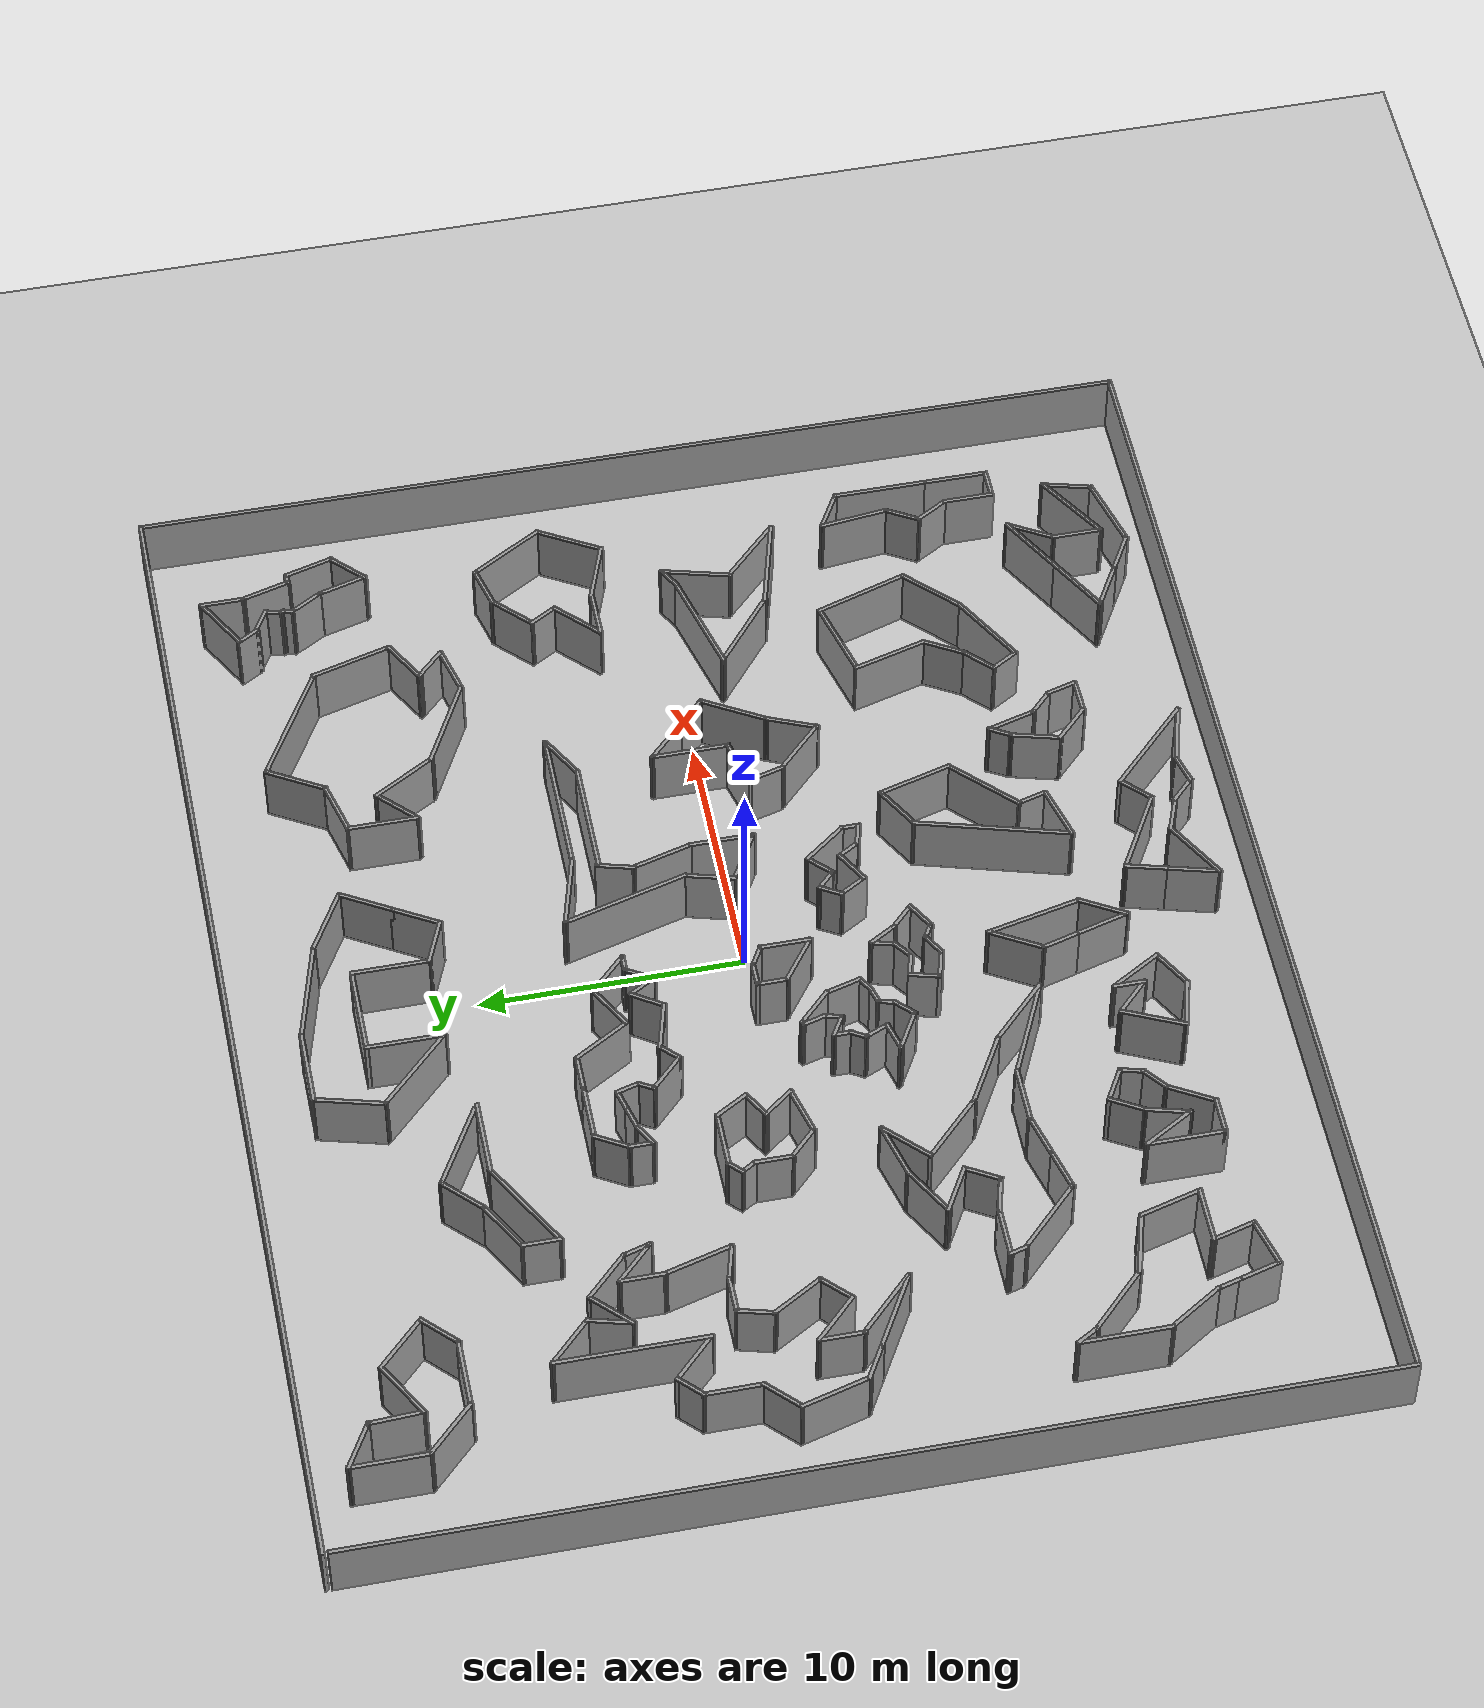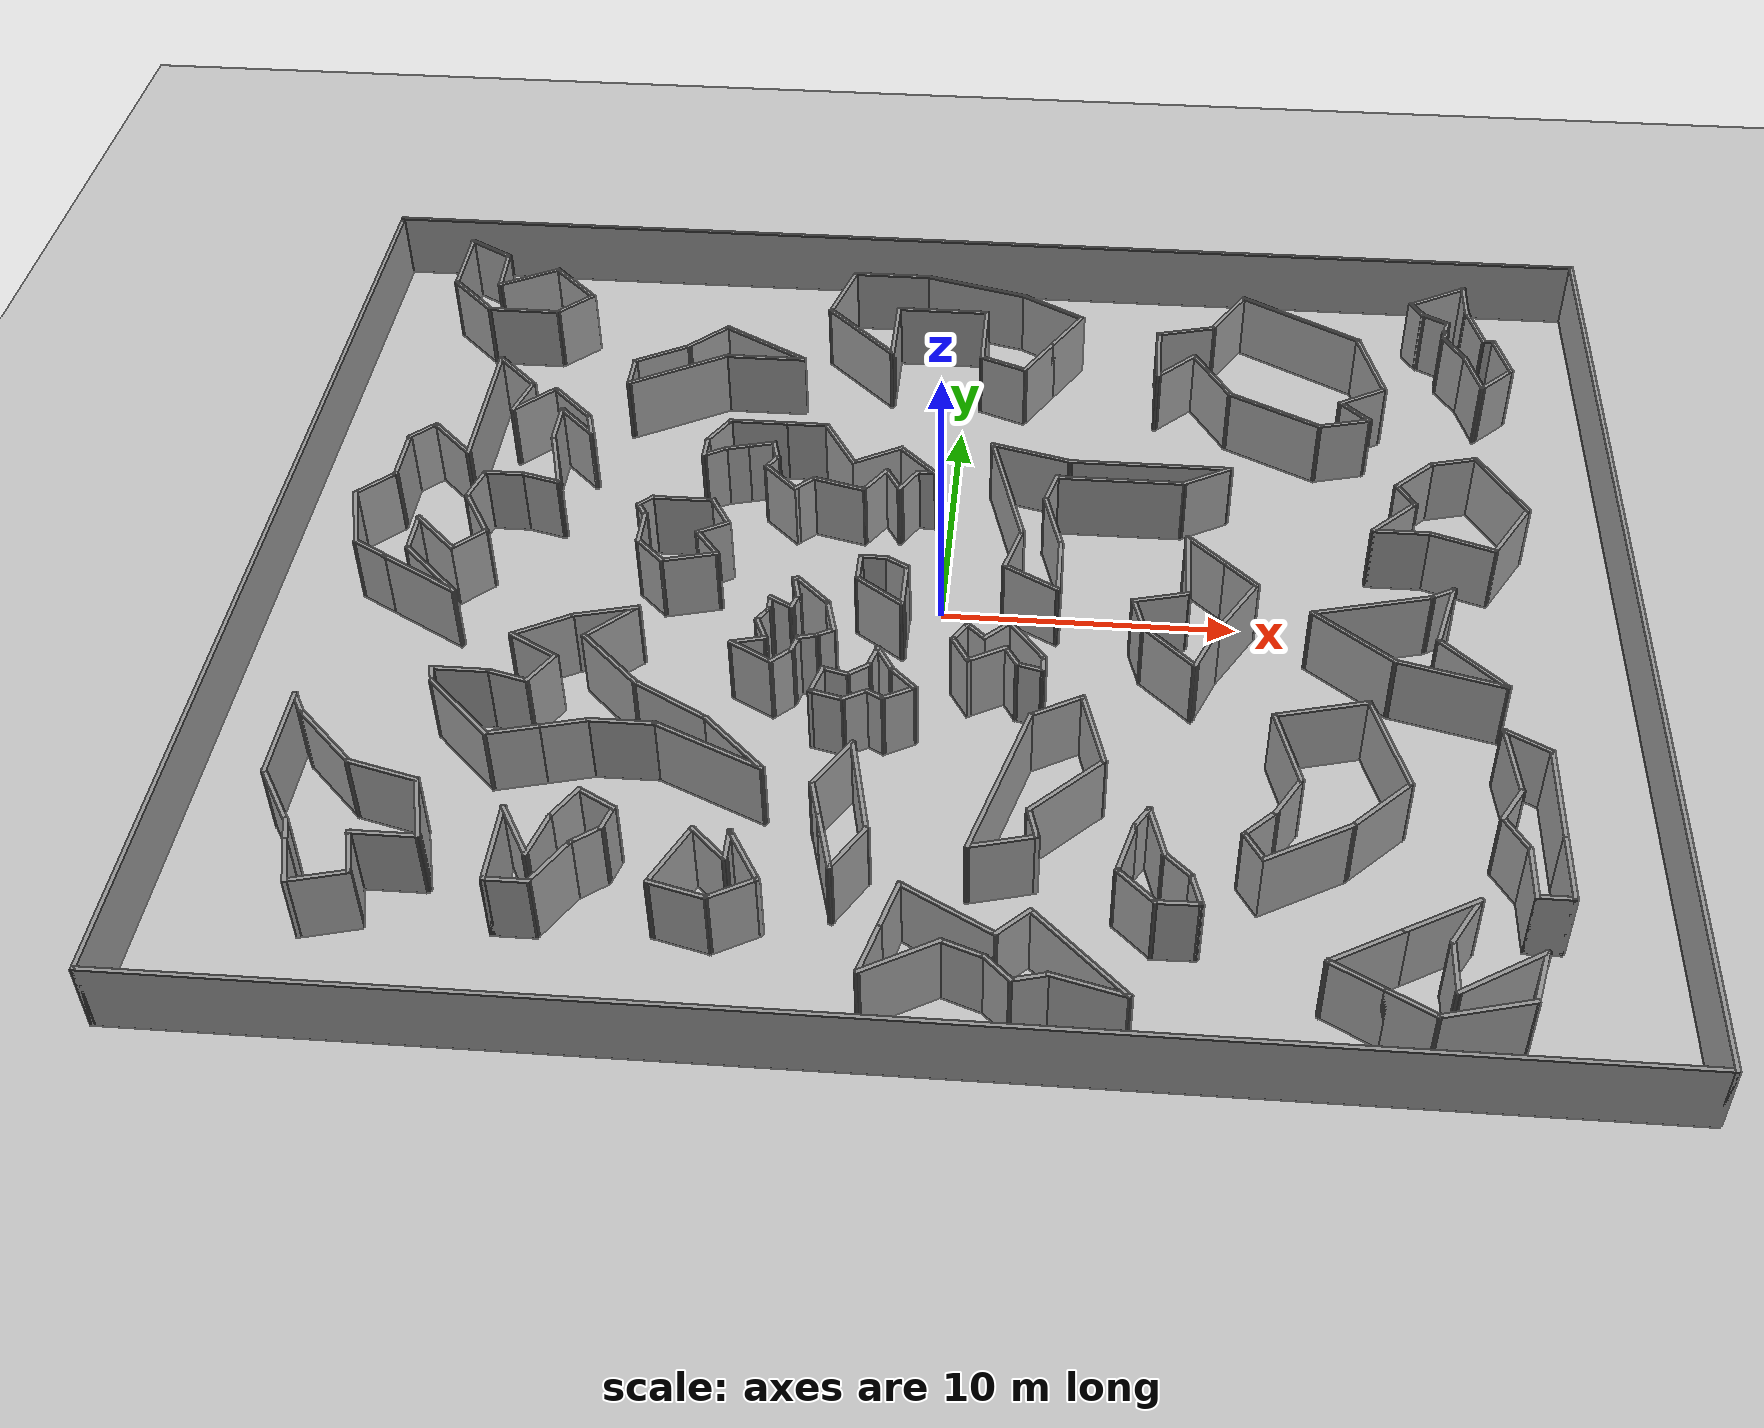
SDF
<sdf version="1.6">
 <world name="default">
  <model name="ground_plane">
   <static>1</static>
   <link name="link">
    <collision name="collision">
     <geometry><plane><normal>0 0 1</normal><size>100 100</size></plane></geometry>
     <surface><friction><ode><mu>100</mu><mu2>50</mu2></ode></friction></surface>
    </collision>
    <visual name="visual">
     <cast_shadows>0</cast_shadows>
     <geometry><plane><normal>0 0 1</normal><size>100 100</size></plane></geometry>
     <material>
      <script><uri>file://media/materials/scripts/gazebo.material</uri><name>Gazebo/Grey</name></script>
     </material>
    </visual>
   </link>
  </model>
  <light name="sun" type="directional">
   <pose>0 0 10 0 -0 0</pose>
   <diffuse>0.8 0.8 0.8 1</diffuse>
   <specular>0.1 0.1 0.1 1</specular>
   <attenuation>
    <range>1000</range>
    <constant>0.9</constant>
    <linear>0.01</linear>
    <quadratic>0.001</quadratic>
   </attenuation>
   <direction>-0.5 0.5 -1</direction>
  </light>
  <physics name="default_physics" default="0" type="ode">
   <max_step_size>0.001</max_step_size>
   <real_time_factor>1</real_time_factor>
   <real_time_update_rate>1000</real_time_update_rate>
  </physics>
  <gravity>0 0 -9.8</gravity>
  <magnetic_field>6e-06 2.3e-05 -4.2e-05</magnetic_field>
  <atmosphere type="adiabatic"/>
  <scene><ambient>0.4 0.4 0.4 1</ambient><background>0.7 0.7 0.7 1</background><shadows>1</shadows></scene>
  <spherical_coordinates>
   <surface_model>EARTH_WGS84</surface_model>
   <latitude_deg>0</latitude_deg>
   <longitude_deg>0</longitude_deg>
   <elevation>0</elevation>
   <heading_deg>0</heading_deg>
  </spherical_coordinates>
  <model name="square_1">
   <pose>0.009703 -0.009719 0 0 -0 0</pose>
   <link name="Wall_0">
    <collision name="Wall_0_Collision">
     <geometry><box><size>2 0.15 2.5</size></box></geometry>
     <pose>0 0 1.25 0 -0 0</pose>
    </collision>
    <visual name="Wall_0_Visual">
     <pose>0 0 1.25 0 -0 0</pose>
     <geometry><box><size>2 0.15 2.5</size></box></geometry>
     <material>
      <script><uri>file://media/materials/scripts/gazebo.material</uri><name>Gazebo/Grey</name></script>
      <ambient>1 1 1 1</ambient>
     </material>
     <meta><layer>0</layer></meta>
    </visual>
    <pose>-1.15789 -1.26056 0 0 -0 1.5708</pose>
   </link>
   <link name="Wall_1">
    <collision name="Wall_1_Collision">
     <geometry><box><size>1 0.15 2.5</size></box></geometry>
     <pose>0 0 1.25 0 -0 0</pose>
    </collision>
    <visual name="Wall_1_Visual">
     <pose>0 0 1.25 0 -0 0</pose>
     <geometry><box><size>1 0.15 2.5</size></box></geometry>
     <material>
      <script><uri>file://media/materials/scripts/gazebo.material</uri><name>Gazebo/Grey</name></script>
      <ambient>1 1 1 1</ambient>
     </material>
     <meta><layer>0</layer></meta>
    </visual>
    <pose>-1.52595 -0.123056 0 0 -0 2.61799</pose>
   </link>
   <link name="Wall_10">
    <collision name="Wall_10_Collision">
     <geometry><box><size>1.5 0.15 2.5</size></box></geometry>
     <pose>0 0 1.25 0 -0 0</pose>
    </collision>
    <visual name="Wall_10_Visual">
     <pose>0 0 1.25 0 -0 0</pose>
     <geometry><box><size>1.5 0.15 2.5</size></box></geometry>
     <material>
      <script><uri>file://media/materials/scripts/gazebo.material</uri><name>Gazebo/Grey</name></script>
      <ambient>1 1 1 1</ambient>
     </material>
     <meta><layer>0</layer></meta>
    </visual>
    <pose>1.77578 -4.36071 0 0 -0 0.523599</pose>
   </link>
   <link name="Wall_100">
    <collision name="Wall_100_Collision">
     <geometry><box><size>2.75 0.15 2.5</size></box></geometry>
     <pose>0 0 1.25 0 -0 0</pose>
    </collision>
    <visual name="Wall_100_Visual">
     <pose>0 0 1.25 0 -0 0</pose>
     <geometry><box><size>2.75 0.15 2.5</size></box></geometry>
     <material>
      <script><uri>file://media/materials/scripts/gazebo.material</uri><name>Gazebo/Grey</name></script>
      <ambient>1 1 1 1</ambient>
     </material>
     <meta><layer>0</layer></meta>
    </visual>
    <pose>3.07498 15.0231 0 0 0 -0.523599</pose>
   </link>
   <link name="Wall_101">
    <collision name="Wall_101_Collision">
     <geometry><box><size>2.25 0.15 2.5</size></box></geometry>
     <pose>0 0 1.25 0 -0 0</pose>
    </collision>
    <visual name="Wall_101_Visual">
     <pose>0 0 1.25 0 -0 0</pose>
     <geometry><box><size>2.25 0.15 2.5</size></box></geometry>
     <material>
      <script><uri>file://media/materials/scripts/gazebo.material</uri><name>Gazebo/Grey</name></script>
      <ambient>1 1 1 1</ambient>
     </material>
     <meta><layer>0</layer></meta>
    </visual>
    <pose>3.67582 13.4637 0 0 0 -2.0944</pose>
   </link>
   <link name="Wall_102">
    <collision name="Wall_102_Collision">
     <geometry><box><size>2 0.15 2.5</size></box></geometry>
     <pose>0 0 1.25 0 -0 0</pose>
    </collision>
    <visual name="Wall_102_Visual">
     <pose>0 0 1.25 0 -0 0</pose>
     <geometry><box><size>2 0.15 2.5</size></box></geometry>
     <material>
      <script><uri>file://media/materials/scripts/gazebo.material</uri><name>Gazebo/Grey</name></script>
      <ambient>1 1 1 1</ambient>
     </material>
     <meta><layer>0</layer></meta>
    </visual>
    <pose>2.68831 11.7533 0 0 0 -2.0944</pose>
   </link>
   <link name="Wall_103">
    <collision name="Wall_103_Collision">
     <geometry><box><size>1.902 0.15 2.5</size></box></geometry>
     <pose>0 0 1.25 0 -0 0</pose>
    </collision>
    <visual name="Wall_103_Visual">
     <pose>0 0 1.25 0 -0 0</pose>
     <geometry><box><size>1.902 0.15 2.5</size></box></geometry>
     <material>
      <script><uri>file://media/materials/scripts/gazebo.material</uri><name>Gazebo/Grey</name></script>
      <ambient>1 1 1 1</ambient>
     </material>
     <meta><layer>0</layer></meta>
    </visual>
    <pose>1.4144 11.2824 0 0 -0 2.75519</pose>
   </link>
   <link name="Wall_105">
    <collision name="Wall_105_Collision">
     <geometry><box><size>3.5 0.15 2.5</size></box></geometry>
     <pose>0 0 1.25 0 -0 0</pose>
    </collision>
    <visual name="Wall_105_Visual">
     <pose>0 0 1.25 0 -0 0</pose>
     <geometry><box><size>3.5 0.15 2.5</size></box></geometry>
     <material>
      <script><uri>file://media/materials/scripts/gazebo.material</uri><name>Gazebo/Grey</name></script>
      <ambient>1 1 1 1</ambient>
     </material>
     <meta><layer>0</layer></meta>
    </visual>
    <pose>-7.60368 11.9241 0 0 -0 2.61799</pose>
   </link>
   <link name="Wall_106">
    <collision name="Wall_106_Collision">
     <geometry><box><size>2 0.15 2.5</size></box></geometry>
     <pose>0 0 1.25 0 -0 0</pose>
    </collision>
    <visual name="Wall_106_Visual">
     <pose>0 0 1.25 0 -0 0</pose>
     <geometry><box><size>2 0.15 2.5</size></box></geometry>
     <material>
      <script><uri>file://media/materials/scripts/gazebo.material</uri><name>Gazebo/Grey</name></script>
      <ambient>1 1 1 1</ambient>
     </material>
     <meta><layer>0</layer></meta>
    </visual>
    <pose>-9.70835 12.1075 0 0 0 -2.35619</pose>
   </link>
   <link name="Wall_107">
    <collision name="Wall_107_Collision">
     <geometry><box><size>2.25 0.15 2.5</size></box></geometry>
     <pose>0 0 1.25 0 -0 0</pose>
    </collision>
    <visual name="Wall_107_Visual">
     <pose>0 0 1.25 0 -0 0</pose>
     <geometry><box><size>2.25 0.15 2.5</size></box></geometry>
     <material>
      <script><uri>file://media/materials/scripts/gazebo.material</uri><name>Gazebo/Grey</name></script>
      <ambient>1 1 1 1</ambient>
     </material>
     <meta><layer>0</layer></meta>
    </visual>
    <pose>-11.2718 10.9285 0 0 0 -2.61799</pose>
   </link>
   <link name="Wall_108">
    <collision name="Wall_108_Collision">
     <geometry><box><size>1.5 0.15 2.5</size></box></geometry>
     <pose>0 0 1.25 0 -0 0</pose>
    </collision>
    <visual name="Wall_108_Visual">
     <pose>0 0 1.25 0 -0 0</pose>
     <geometry><box><size>1.5 0.15 2.5</size></box></geometry>
     <material>
      <script><uri>file://media/materials/scripts/gazebo.material</uri><name>Gazebo/Grey</name></script>
      <ambient>1 1 1 1</ambient>
     </material>
     <meta><layer>0</layer></meta>
    </visual>
    <pose>-12.1811 9.72845 0 0 0 -1.5708</pose>
   </link>
   <link name="Wall_109">
    <collision name="Wall_109_Collision">
     <geometry><box><size>4 0.15 2.5</size></box></geometry>
     <pose>0 0 1.25 0 -0 0</pose>
    </collision>
    <visual name="Wall_109_Visual">
     <pose>0 0 1.25 0 -0 0</pose>
     <geometry><box><size>4 0.15 2.5</size></box></geometry>
     <material>
      <script><uri>file://media/materials/scripts/gazebo.material</uri><name>Gazebo/Grey</name></script>
      <ambient>1 1 1 1</ambient>
     </material>
     <meta><layer>0</layer></meta>
    </visual>
    <pose>-10.514 10.016 0 0 -0 0.523599</pose>
   </link>
   <link name="Wall_11">
    <collision name="Wall_11_Collision">
     <geometry><box><size>1 0.15 2.5</size></box></geometry>
     <pose>0 0 1.25 0 -0 0</pose>
    </collision>
    <visual name="Wall_11_Visual">
     <pose>0 0 1.25 0 -0 0</pose>
     <geometry><box><size>1 0.15 2.5</size></box></geometry>
     <material>
      <script><uri>file://media/materials/scripts/gazebo.material</uri><name>Gazebo/Grey</name></script>
      <ambient>1 1 1 1</ambient>
     </material>
     <meta><layer>0</layer></meta>
    </visual>
    <pose>2.57284 -4.39128 0 0 0 -1.0472</pose>
   </link>
   <link name="Wall_110">
    <collision name="Wall_110_Collision">
     <geometry><box><size>3 0.15 2.5</size></box></geometry>
     <pose>0 0 1.25 0 -0 0</pose>
    </collision>
    <visual name="Wall_110_Visual">
     <pose>0 0 1.25 0 -0 0</pose>
     <geometry><box><size>3 0.15 2.5</size></box></geometry>
     <material>
      <script><uri>file://media/materials/scripts/gazebo.material</uri><name>Gazebo/Grey</name></script>
      <ambient>1 1 1 1</ambient>
     </material>
     <meta><layer>0</layer></meta>
    </visual>
    <pose>-7.42188 10.9785 0 0 -0 0</pose>
   </link>
   <link name="Wall_112">
    <collision name="Wall_112_Collision">
     <geometry><box><size>3 0.15 2.5</size></box></geometry>
     <pose>0 0 1.25 0 -0 0</pose>
    </collision>
    <visual name="Wall_112_Visual">
     <pose>0 0 1.25 0 -0 0</pose>
     <geometry><box><size>3 0.15 2.5</size></box></geometry>
     <material>
      <script><uri>file://media/materials/scripts/gazebo.material</uri><name>Gazebo/Grey</name></script>
      <ambient>1 1 1 1</ambient>
     </material>
     <meta><layer>0</layer></meta>
    </visual>
    <pose>-5.78523 -8.94267 0 0 -0 2.35619</pose>
   </link>
   <link name="Wall_113">
    <collision name="Wall_113_Collision">
     <geometry><box><size>3 0.15 2.5</size></box></geometry>
     <pose>0 0 1.25 0 -0 0</pose>
    </collision>
    <visual name="Wall_113_Visual">
     <pose>0 0 1.25 0 -0 0</pose>
     <geometry><box><size>3 0.15 2.5</size></box></geometry>
     <material>
      <script><uri>file://media/materials/scripts/gazebo.material</uri><name>Gazebo/Grey</name></script>
      <ambient>1 1 1 1</ambient>
     </material>
     <meta><layer>0</layer></meta>
    </visual>
    <pose>-8.02694 -7.22255 0 0 -0 2.61799</pose>
   </link>
   <link name="Wall_114">
    <collision name="Wall_114_Collision">
     <geometry><box><size>3 0.15 2.5</size></box></geometry>
     <pose>0 0 1.25 0 -0 0</pose>
    </collision>
    <visual name="Wall_114_Visual">
     <pose>0 0 1.25 0 -0 0</pose>
     <geometry><box><size>3 0.15 2.5</size></box></geometry>
     <material>
      <script><uri>file://media/materials/scripts/gazebo.material</uri><name>Gazebo/Grey</name></script>
      <ambient>1 1 1 1</ambient>
     </material>
     <meta><layer>0</layer></meta>
    </visual>
    <pose>-10.2687 -5.50242 0 0 -0 2.35619</pose>
   </link>
   <link name="Wall_115">
    <collision name="Wall_115_Collision">
     <geometry><box><size>2.25 0.15 2.5</size></box></geometry>
     <pose>0 0 1.25 0 -0 0</pose>
    </collision>
    <visual name="Wall_115_Visual">
     <pose>0 0 1.25 0 -0 0</pose>
     <geometry><box><size>2.25 0.15 2.5</size></box></geometry>
     <material>
      <script><uri>file://media/materials/scripts/gazebo.material</uri><name>Gazebo/Grey</name></script>
      <ambient>1 1 1 1</ambient>
     </material>
     <meta><layer>0</layer></meta>
    </visual>
    <pose>-10.5338 -3.75233 0 0 -0 0.785398</pose>
   </link>
   <link name="Wall_116">
    <collision name="Wall_116_Collision">
     <geometry><box><size>2.25 0.15 2.5</size></box></geometry>
     <pose>0 0 1.25 0 -0 0</pose>
    </collision>
    <visual name="Wall_116_Visual">
     <pose>0 0 1.25 0 -0 0</pose>
     <geometry><box><size>2.25 0.15 2.5</size></box></geometry>
     <material>
      <script><uri>file://media/materials/scripts/gazebo.material</uri><name>Gazebo/Grey</name></script>
      <ambient>1 1 1 1</ambient>
     </material>
     <meta><layer>0</layer></meta>
    </visual>
    <pose>-10.8056 -3.28163 0 0 0 -2.87979</pose>
   </link>
   <link name="Wall_117">
    <collision name="Wall_117_Collision">
     <geometry><box><size>2.25 0.15 2.5</size></box></geometry>
     <pose>0 0 1.25 0 -0 0</pose>
    </collision>
    <visual name="Wall_117_Visual">
     <pose>0 0 1.25 0 -0 0</pose>
     <geometry><box><size>2.25 0.15 2.5</size></box></geometry>
     <material>
      <script><uri>file://media/materials/scripts/gazebo.material</uri><name>Gazebo/Grey</name></script>
      <ambient>1 1 1 1</ambient>
     </material>
     <meta><layer>0</layer></meta>
    </visual>
    <pose>-12.7291 -4.07839 0 0 0 -2.61799</pose>
   </link>
   <link name="Wall_118">
    <collision name="Wall_118_Collision">
     <geometry><box><size>2 0.15 2.5</size></box></geometry>
     <pose>0 0 1.25 0 -0 0</pose>
    </collision>
    <visual name="Wall_118_Visual">
     <pose>0 0 1.25 0 -0 0</pose>
     <geometry><box><size>2 0.15 2.5</size></box></geometry>
     <material>
      <script><uri>file://media/materials/scripts/gazebo.material</uri><name>Gazebo/Grey</name></script>
      <ambient>1 1 1 1</ambient>
     </material>
     <meta><layer>0</layer></meta>
    </visual>
    <pose>-12.8374 -5.06589 0 0 0 -0.523599</pose>
   </link>
   <link name="Wall_119">
    <collision name="Wall_119_Collision">
     <geometry><box><size>1.5 0.15 2.5</size></box></geometry>
     <pose>0 0 1.25 0 -0 0</pose>
    </collision>
    <visual name="Wall_119_Visual">
     <pose>0 0 1.25 0 -0 0</pose>
     <geometry><box><size>1.5 0.15 2.5</size></box></geometry>
     <material>
      <script><uri>file://media/materials/scripts/gazebo.material</uri><name>Gazebo/Grey</name></script>
      <ambient>1 1 1 1</ambient>
     </material>
     <meta><layer>0</layer></meta>
    </visual>
    <pose>-12.3738 -6.11296 0 0 0 -2.0944</pose>
   </link>
   <link name="Wall_12">
    <collision name="Wall_12_Collision">
     <geometry><box><size>1 0.15 2.5</size></box></geometry>
     <pose>0 0 1.25 0 -0 0</pose>
    </collision>
    <visual name="Wall_12_Visual">
     <pose>0 0 1.25 0 -0 0</pose>
     <geometry><box><size>1 0.15 2.5</size></box></geometry>
     <material>
      <script><uri>file://media/materials/scripts/gazebo.material</uri><name>Gazebo/Grey</name></script>
      <ambient>1 1 1 1</ambient>
     </material>
     <meta><layer>0</layer></meta>
    </visual>
    <pose>3.19586 -4.86934 0 0 0 -0.261799</pose>
   </link>
   <link name="Wall_120">
    <collision name="Wall_120_Collision">
     <geometry><box><size>1.5 0.15 2.5</size></box></geometry>
     <pose>0 0 1.25 0 -0 0</pose>
    </collision>
    <visual name="Wall_120_Visual">
     <pose>0 0 1.25 0 -0 0</pose>
     <geometry><box><size>1.5 0.15 2.5</size></box></geometry>
     <material>
      <script><uri>file://media/materials/scripts/gazebo.material</uri><name>Gazebo/Grey</name></script>
      <ambient>1 1 1 1</ambient>
     </material>
     <meta><layer>0</layer></meta>
    </visual>
    <pose>-13.3633 -6.52282 0 0 -0 2.87979</pose>
   </link>
   <link name="Wall_121">
    <collision name="Wall_121_Collision">
     <geometry><box><size>2 0.15 2.5</size></box></geometry>
     <pose>0 0 1.25 0 -0 0</pose>
    </collision>
    <visual name="Wall_121_Visual">
     <pose>0 0 1.25 0 -0 0</pose>
     <geometry><box><size>2 0.15 2.5</size></box></geometry>
     <material>
      <script><uri>file://media/materials/scripts/gazebo.material</uri><name>Gazebo/Grey</name></script>
      <ambient>1 1 1 1</ambient>
     </material>
     <meta><layer>0</layer></meta>
    </visual>
    <pose>-14.9403 -6.34812 0 0 -0 3.14159</pose>
   </link>
   <link name="Wall_122">
    <collision name="Wall_122_Collision">
     <geometry><box><size>0.75 0.15 2.5</size></box></geometry>
     <pose>0 0 1.25 0 -0 0</pose>
    </collision>
    <visual name="Wall_122_Visual">
     <pose>0 0 1.25 0 -0 0</pose>
     <geometry><box><size>0.75 0.15 2.5</size></box></geometry>
     <material>
      <script><uri>file://media/materials/scripts/gazebo.material</uri><name>Gazebo/Grey</name></script>
      <ambient>1 1 1 1</ambient>
     </material>
     <meta><layer>0</layer></meta>
    </visual>
    <pose>-15.7877 -6.6379 0 0 0 -1.309</pose>
   </link>
   <link name="Wall_123">
    <collision name="Wall_123_Collision">
     <geometry><box><size>3.25 0.15 2.5</size></box></geometry>
     <pose>0 0 1.25 0 -0 0</pose>
    </collision>
    <visual name="Wall_123_Visual">
     <pose>0 0 1.25 0 -0 0</pose>
     <geometry><box><size>3.25 0.15 2.5</size></box></geometry>
     <material>
      <script><uri>file://media/materials/scripts/gazebo.material</uri><name>Gazebo/Grey</name></script>
      <ambient>1 1 1 1</ambient>
     </material>
     <meta><layer>0</layer></meta>
    </visual>
    <pose>-14.614 -8.02369 0 0 0 -0.785398</pose>
   </link>
   <link name="Wall_124">
    <collision name="Wall_124_Collision">
     <geometry><box><size>1.75 0.15 2.5</size></box></geometry>
     <pose>0 0 1.25 0 -0 0</pose>
    </collision>
    <visual name="Wall_124_Visual">
     <pose>0 0 1.25 0 -0 0</pose>
     <geometry><box><size>1.75 0.15 2.5</size></box></geometry>
     <material>
      <script><uri>file://media/materials/scripts/gazebo.material</uri><name>Gazebo/Grey</name></script>
      <ambient>1 1 1 1</ambient>
     </material>
     <meta><layer>0</layer></meta>
    </visual>
    <pose>-12.7452 -8.91265 0 0 -0 0.261799</pose>
   </link>
   <link name="Wall_125">
    <collision name="Wall_125_Collision">
     <geometry><box><size>1.75 0.15 2.5</size></box></geometry>
     <pose>0 0 1.25 0 -0 0</pose>
    </collision>
    <visual name="Wall_125_Visual">
     <pose>0 0 1.25 0 -0 0</pose>
     <geometry><box><size>1.75 0.15 2.5</size></box></geometry>
     <material>
      <script><uri>file://media/materials/scripts/gazebo.material</uri><name>Gazebo/Grey</name></script>
      <ambient>1 1 1 1</ambient>
     </material>
     <meta><layer>0</layer></meta>
    </visual>
    <pose>-11.1998 -8.49854 0 0 -0 0.261799</pose>
   </link>
   <link name="Wall_126">
    <collision name="Wall_126_Collision">
     <geometry><box><size>2.25 0.15 2.5</size></box></geometry>
     <pose>0 0 1.25 0 -0 0</pose>
    </collision>
    <visual name="Wall_126_Visual">
     <pose>0 0 1.25 0 -0 0</pose>
     <geometry><box><size>2.25 0.15 2.5</size></box></geometry>
     <material>
      <script><uri>file://media/materials/scripts/gazebo.material</uri><name>Gazebo/Grey</name></script>
      <ambient>1 1 1 1</ambient>
     </material>
     <meta><layer>0</layer></meta>
    </visual>
    <pose>-9.37702 -8.29148 0 0 -0 0</pose>
   </link>
   <link name="Wall_127">
    <collision name="Wall_127_Collision">
     <geometry><box><size>4.06792 0.15 2.5</size></box></geometry>
     <pose>0 0 1.25 0 -0 0</pose>
    </collision>
    <visual name="Wall_127_Visual">
     <pose>0 0 1.25 0 -0 0</pose>
     <geometry><box><size>4.06792 0.15 2.5</size></box></geometry>
     <material>
      <script><uri>file://media/materials/scripts/gazebo.material</uri><name>Gazebo/Grey</name></script>
      <ambient>1 1 1 1</ambient>
     </material>
     <meta><layer>0</layer></meta>
    </visual>
    <pose>-6.55231 -9.12089 0 0 0 -0.437187</pose>
   </link>
   <link name="Wall_129">
    <collision name="Wall_129_Collision">
     <geometry><box><size>2 0.15 2.5</size></box></geometry>
     <pose>0 0 1.25 0 -0 0</pose>
    </collision>
    <visual name="Wall_129_Visual">
     <pose>0 0 1.25 0 -0 0</pose>
     <geometry><box><size>2 0.15 2.5</size></box></geometry>
     <material>
      <script><uri>file://media/materials/scripts/gazebo.material</uri><name>Gazebo/Grey</name></script>
      <ambient>1 1 1 1</ambient>
     </material>
     <meta><layer>0</layer></meta>
    </visual>
    <pose>4.11459 -6.575 0 0 -0 0.523599</pose>
   </link>
   <link name="Wall_13">
    <collision name="Wall_13_Collision">
     <geometry><box><size>0.75 0.15 2.5</size></box></geometry>
     <pose>0 0 1.25 0 -0 0</pose>
    </collision>
    <visual name="Wall_13_Visual">
     <pose>0 0 1.25 0 -0 0</pose>
     <geometry><box><size>0.75 0.15 2.5</size></box></geometry>
     <material>
      <script><uri>file://media/materials/scripts/gazebo.material</uri><name>Gazebo/Grey</name></script>
      <ambient>1 1 1 1</ambient>
     </material>
     <meta><layer>0</layer></meta>
    </visual>
    <pose>3.60638 -4.67933 0 0 -0 1.5708</pose>
   </link>
   <link name="Wall_130">
    <collision name="Wall_130_Collision">
     <geometry><box><size>3 0.15 2.5</size></box></geometry>
     <pose>0 0 1.25 0 -0 0</pose>
    </collision>
    <visual name="Wall_130_Visual">
     <pose>0 0 1.25 0 -0 0</pose>
     <geometry><box><size>3 0.15 2.5</size></box></geometry>
     <material>
      <script><uri>file://media/materials/scripts/gazebo.material</uri><name>Gazebo/Grey</name></script>
      <ambient>1 1 1 1</ambient>
     </material>
     <meta><layer>0</layer></meta>
    </visual>
    <pose>5.28448 -7.48894 0 0 0 -1.309</pose>
   </link>
   <link name="Wall_131">
    <collision name="Wall_131_Collision">
     <geometry><box><size>3.25 0.15 2.5</size></box></geometry>
     <pose>0 0 1.25 0 -0 0</pose>
    </collision>
    <visual name="Wall_131_Visual">
     <pose>0 0 1.25 0 -0 0</pose>
     <geometry><box><size>3.25 0.15 2.5</size></box></geometry>
     <material>
      <script><uri>file://media/materials/scripts/gazebo.material</uri><name>Gazebo/Grey</name></script>
      <ambient>1 1 1 1</ambient>
     </material>
     <meta><layer>0</layer></meta>
    </visual>
    <pose>4.55728 -9.9614 0 0 0 -2.35619</pose>
   </link>
   <link name="Wall_132">
    <collision name="Wall_132_Collision">
     <geometry><box><size>1.25 0.15 2.5</size></box></geometry>
     <pose>0 0 1.25 0 -0 0</pose>
    </collision>
    <visual name="Wall_132_Visual">
     <pose>0 0 1.25 0 -0 0</pose>
     <geometry><box><size>1.25 0.15 2.5</size></box></geometry>
     <material>
      <script><uri>file://media/materials/scripts/gazebo.material</uri><name>Gazebo/Grey</name></script>
      <ambient>1 1 1 1</ambient>
     </material>
     <meta><layer>0</layer></meta>
    </visual>
    <pose>3.60361 -11.5887 0 0 0 -1.309</pose>
   </link>
   <link name="Wall_133">
    <collision name="Wall_133_Collision">
     <geometry><box><size>2.25 0.15 2.5</size></box></geometry>
     <pose>0 0 1.25 0 -0 0</pose>
    </collision>
    <visual name="Wall_133_Visual">
     <pose>0 0 1.25 0 -0 0</pose>
     <geometry><box><size>2.25 0.15 2.5</size></box></geometry>
     <material>
      <script><uri>file://media/materials/scripts/gazebo.material</uri><name>Gazebo/Grey</name></script>
      <ambient>1 1 1 1</ambient>
     </material>
     <meta><layer>0</layer></meta>
    </visual>
    <pose>2.73174 -12.3917 0 0 0 -2.87979</pose>
   </link>
   <link name="Wall_134">
    <collision name="Wall_134_Collision">
     <geometry><box><size>5.99796 0.15 2.5</size></box></geometry>
     <pose>0 0 1.25 0 -0 0</pose>
    </collision>
    <visual name="Wall_134_Visual">
     <pose>0 0 1.25 0 -0 0</pose>
     <geometry><box><size>5.99796 0.15 2.5</size></box></geometry>
     <material>
      <script><uri>file://media/materials/scripts/gazebo.material</uri><name>Gazebo/Grey</name></script>
      <ambient>1 1 1 1</ambient>
     </material>
     <meta><layer>0</layer></meta>
    </visual>
    <pose>2.51552 -9.85048 0 0 -0 1.29438</pose>
   </link>
   <link name="Wall_136">
    <collision name="Wall_136_Collision">
     <geometry><box><size>2.25 0.15 2.5</size></box></geometry>
     <pose>0 0 1.25 0 -0 0</pose>
    </collision>
    <visual name="Wall_136_Visual">
     <pose>0 0 1.25 0 -0 0</pose>
     <geometry><box><size>2.25 0.15 2.5</size></box></geometry>
     <material>
      <script><uri>file://media/materials/scripts/gazebo.material</uri><name>Gazebo/Grey</name></script>
      <ambient>1 1 1 1</ambient>
     </material>
     <meta><layer>0</layer></meta>
    </visual>
    <pose>-2.63253 -9.56505 0 0 0 -2.0944</pose>
   </link>
   <link name="Wall_137">
    <collision name="Wall_137_Collision">
     <geometry><box><size>1.5 0.15 2.5</size></box></geometry>
     <pose>0 0 1.25 0 -0 0</pose>
    </collision>
    <visual name="Wall_137_Visual">
     <pose>0 0 1.25 0 -0 0</pose>
     <geometry><box><size>1.5 0.15 2.5</size></box></geometry>
     <material>
      <script><uri>file://media/materials/scripts/gazebo.material</uri><name>Gazebo/Grey</name></script>
      <ambient>1 1 1 1</ambient>
     </material>
     <meta><layer>0</layer></meta>
    </visual>
    <pose>-2.98283 -11.1264 0 0 0 -1.309</pose>
   </link>
   <link name="Wall_138">
    <collision name="Wall_138_Collision">
     <geometry><box><size>2.25 0.15 2.5</size></box></geometry>
     <pose>0 0 1.25 0 -0 0</pose>
    </collision>
    <visual name="Wall_138_Visual">
     <pose>0 0 1.25 0 -0 0</pose>
     <geometry><box><size>2.25 0.15 2.5</size></box></geometry>
     <material>
      <script><uri>file://media/materials/scripts/gazebo.material</uri><name>Gazebo/Grey</name></script>
      <ambient>1 1 1 1</ambient>
     </material>
     <meta><layer>0</layer></meta>
    </visual>
    <pose>-2.53637 -12.7926 0 0 0 -1.309</pose>
   </link>
   <link name="Wall_139">
    <collision name="Wall_139_Collision">
     <geometry><box><size>2 0.15 2.5</size></box></geometry>
     <pose>0 0 1.25 0 -0 0</pose>
    </collision>
    <visual name="Wall_139_Visual">
     <pose>0 0 1.25 0 -0 0</pose>
     <geometry><box><size>2 0.15 2.5</size></box></geometry>
     <material>
      <script><uri>file://media/materials/scripts/gazebo.material</uri><name>Gazebo/Grey</name></script>
      <ambient>1 1 1 1</ambient>
     </material>
     <meta><layer>0</layer></meta>
    </visual>
    <pose>-1.80211 -13.0057 0 0 -0 1.0472</pose>
   </link>
   <link name="Wall_14">
    <collision name="Wall_14_Collision">
     <geometry><box><size>2.0841 0.15 2.5</size></box></geometry>
     <pose>0 0 1.25 0 -0 0</pose>
    </collision>
    <visual name="Wall_14_Visual">
     <pose>0 0 1.25 0 -0 0</pose>
     <geometry><box><size>2.0841 0.15 2.5</size></box></geometry>
     <material>
      <script><uri>file://media/materials/scripts/gazebo.material</uri><name>Gazebo/Grey</name></script>
      <ambient>1 1 1 1</ambient>
     </material>
     <meta><layer>0</layer></meta>
    </visual>
    <pose>3.02572 -3.60601 0 0 -0 2.21485</pose>
   </link>
   <link name="Wall_140">
    <collision name="Wall_140_Collision">
     <geometry><box><size>3.78108 0.15 2.5</size></box></geometry>
     <pose>0 0 1.25 0 -0 0</pose>
    </collision>
    <visual name="Wall_140_Visual">
     <pose>0 0 1.25 0 -0 0</pose>
     <geometry><box><size>3.78108 0.15 2.5</size></box></geometry>
     <material>
      <script><uri>file://media/materials/scripts/gazebo.material</uri><name>Gazebo/Grey</name></script>
      <ambient>1 1 1 1</ambient>
     </material>
     <meta><layer>0</layer></meta>
    </visual>
    <pose>-1.72357 -10.4302 0 0 -0 1.78389</pose>
   </link>
   <link name="Wall_142">
    <collision name="Wall_142_Collision">
     <geometry><box><size>3.25 0.15 2.5</size></box></geometry>
     <pose>0 0 1.25 0 -0 0</pose>
    </collision>
    <visual name="Wall_142_Visual">
     <pose>0 0 1.25 0 -0 0</pose>
     <geometry><box><size>3.25 0.15 2.5</size></box></geometry>
     <material>
      <script><uri>file://media/materials/scripts/gazebo.material</uri><name>Gazebo/Grey</name></script>
      <ambient>1 1 1 1</ambient>
     </material>
     <meta><layer>0</layer></meta>
    </visual>
    <pose>12.4157 -6.06318 0 0 0 -2.87979</pose>
   </link>
   <link name="Wall_143">
    <collision name="Wall_143_Collision">
     <geometry><box><size>3 0.15 2.5</size></box></geometry>
     <pose>0 0 1.25 0 -0 0</pose>
    </collision>
    <visual name="Wall_143_Visual">
     <pose>0 0 1.25 0 -0 0</pose>
     <geometry><box><size>3 0.15 2.5</size></box></geometry>
     <material>
      <script><uri>file://media/materials/scripts/gazebo.material</uri><name>Gazebo/Grey</name></script>
      <ambient>1 1 1 1</ambient>
     </material>
     <meta><layer>0</layer></meta>
    </visual>
    <pose>11.2873 -7.84079 0 0 0 -1.309</pose>
   </link>
   <link name="Wall_144">
    <collision name="Wall_144_Collision">
     <geometry><box><size>1.75 0.15 2.5</size></box></geometry>
     <pose>0 0 1.25 0 -0 0</pose>
    </collision>
    <visual name="Wall_144_Visual">
     <pose>0 0 1.25 0 -0 0</pose>
     <geometry><box><size>1.75 0.15 2.5</size></box></geometry>
     <material>
      <script><uri>file://media/materials/scripts/gazebo.material</uri><name>Gazebo/Grey</name></script>
      <ambient>1 1 1 1</ambient>
     </material>
     <meta><layer>0</layer></meta>
    </visual>
    <pose>11.2561 -9.91006 0 0 0 -2.0944</pose>
   </link>
   <link name="Wall_145">
    <collision name="Wall_145_Collision">
     <geometry><box><size>1.5 0.15 2.5</size></box></geometry>
     <pose>0 0 1.25 0 -0 0</pose>
    </collision>
    <visual name="Wall_145_Visual">
     <pose>0 0 1.25 0 -0 0</pose>
     <geometry><box><size>1.5 0.15 2.5</size></box></geometry>
     <material>
      <script><uri>file://media/materials/scripts/gazebo.material</uri><name>Gazebo/Grey</name></script>
      <ambient>1 1 1 1</ambient>
     </material>
     <meta><layer>0</layer></meta>
    </visual>
    <pose>10.3788 -11.0802 0 0 0 -2.35619</pose>
   </link>
   <link name="Wall_146">
    <collision name="Wall_146_Collision">
     <geometry><box><size>1.25 0.15 2.5</size></box></geometry>
     <pose>0 0 1.25 0 -0 0</pose>
    </collision>
    <visual name="Wall_146_Visual">
     <pose>0 0 1.25 0 -0 0</pose>
     <geometry><box><size>1.25 0.15 2.5</size></box></geometry>
     <material>
      <script><uri>file://media/materials/scripts/gazebo.material</uri><name>Gazebo/Grey</name></script>
      <ambient>1 1 1 1</ambient>
     </material>
     <meta><layer>0</layer></meta>
    </visual>
    <pose>10.1765 -12.0338 0 0 0 -1.0472</pose>
   </link>
   <link name="Wall_147">
    <collision name="Wall_147_Collision">
     <geometry><box><size>3.25 0.15 2.5</size></box></geometry>
     <pose>0 0 1.25 0 -0 0</pose>
    </collision>
    <visual name="Wall_147_Visual">
     <pose>0 0 1.25 0 -0 0</pose>
     <geometry><box><size>3.25 0.15 2.5</size></box></geometry>
     <material>
      <script><uri>file://media/materials/scripts/gazebo.material</uri><name>Gazebo/Grey</name></script>
      <ambient>1 1 1 1</ambient>
     </material>
     <meta><layer>0</layer></meta>
    </visual>
    <pose>11.7939 -11.7351 0 0 -0 0.523599</pose>
   </link>
   <link name="Wall_148">
    <collision name="Wall_148_Collision">
     <geometry><box><size>2.75 0.15 2.5</size></box></geometry>
     <pose>0 0 1.25 0 -0 0</pose>
    </collision>
    <visual name="Wall_148_Visual">
     <pose>0 0 1.25 0 -0 0</pose>
     <geometry><box><size>2.75 0.15 2.5</size></box></geometry>
     <material>
      <script><uri>file://media/materials/scripts/gazebo.material</uri><name>Gazebo/Grey</name></script>
      <ambient>1 1 1 1</ambient>
     </material>
     <meta><layer>0</layer></meta>
    </visual>
    <pose>14.0555 -10.0409 0 0 -0 0.785398</pose>
   </link>
   <link name="Wall_149">
    <collision name="Wall_149_Collision">
     <geometry><box><size>3.76889 0.15 2.5</size></box></geometry>
     <pose>0 0 1.25 0 -0 0</pose>
    </collision>
    <visual name="Wall_149_Visual">
     <pose>0 0 1.25 0 -0 0</pose>
     <geometry><box><size>3.76889 0.15 2.5</size></box></geometry>
     <material>
      <script><uri>file://media/materials/scripts/gazebo.material</uri><name>Gazebo/Grey</name></script>
      <ambient>1 1 1 1</ambient>
     </material>
     <meta><layer>0</layer></meta>
    </visual>
    <pose>14.4438 -7.39182 0 0 -0 1.86859</pose>
   </link>
   <link name="Wall_151">
    <collision name="Wall_151_Collision">
     <geometry><box><size>2.75 0.15 2.5</size></box></geometry>
     <pose>0 0 1.25 0 -0 0</pose>
    </collision>
    <visual name="Wall_151_Visual">
     <pose>0 0 1.25 0 -0 0</pose>
     <geometry><box><size>2.75 0.15 2.5</size></box></geometry>
     <material>
      <script><uri>file://media/materials/scripts/gazebo.material</uri><name>Gazebo/Grey</name></script>
      <ambient>1 1 1 1</ambient>
     </material>
     <meta><layer>0</layer></meta>
    </visual>
    <pose>9.09595 11.1606 0 0 -0 2.0944</pose>
   </link>
   <link name="Wall_152">
    <collision name="Wall_152_Collision">
     <geometry><box><size>2 0.15 2.5</size></box></geometry>
     <pose>0 0 1.25 0 -0 0</pose>
    </collision>
    <visual name="Wall_152_Visual">
     <pose>0 0 1.25 0 -0 0</pose>
     <geometry><box><size>2 0.15 2.5</size></box></geometry>
     <material>
      <script><uri>file://media/materials/scripts/gazebo.material</uri><name>Gazebo/Grey</name></script>
      <ambient>1 1 1 1</ambient>
     </material>
     <meta><layer>0</layer></meta>
    </visual>
    <pose>7.79188 11.6323 0 0 0 -2.35619</pose>
   </link>
   <link name="Wall_153">
    <collision name="Wall_153_Collision">
     <geometry><box><size>2.75 0.15 2.5</size></box></geometry>
     <pose>0 0 1.25 0 -0 0</pose>
    </collision>
    <visual name="Wall_153_Visual">
     <pose>0 0 1.25 0 -0 0</pose>
     <geometry><box><size>2.75 0.15 2.5</size></box></geometry>
     <material>
      <script><uri>file://media/materials/scripts/gazebo.material</uri><name>Gazebo/Grey</name></script>
      <ambient>1 1 1 1</ambient>
     </material>
     <meta><layer>0</layer></meta>
    </visual>
    <pose>7.1378 12.2783 0 0 -0 1.5708</pose>
   </link>
   <link name="Wall_154">
    <collision name="Wall_154_Collision">
     <geometry><box><size>2.25 0.15 2.5</size></box></geometry>
     <pose>0 0 1.25 0 -0 0</pose>
    </collision>
    <visual name="Wall_154_Visual">
     <pose>0 0 1.25 0 -0 0</pose>
     <geometry><box><size>2.25 0.15 2.5</size></box></geometry>
     <material>
      <script><uri>file://media/materials/scripts/gazebo.material</uri><name>Gazebo/Grey</name></script>
      <ambient>1 1 1 1</ambient>
     </material>
     <meta><layer>0</layer></meta>
    </visual>
    <pose>8.15203 13.85 0 0 -0 0.261799</pose>
   </link>
   <link name="Wall_155">
    <collision name="Wall_155_Collision">
     <geometry><box><size>2.5 0.15 2.5</size></box></geometry>
     <pose>0 0 1.25 0 -0 0</pose>
    </collision>
    <visual name="Wall_155_Visual">
     <pose>0 0 1.25 0 -0 0</pose>
     <geometry><box><size>2.5 0.15 2.5</size></box></geometry>
     <material>
      <script><uri>file://media/materials/scripts/gazebo.material</uri><name>Gazebo/Grey</name></script>
      <ambient>1 1 1 1</ambient>
     </material>
     <meta><layer>0</layer></meta>
    </visual>
    <pose>9.75375 15.1394 0 0 -0 1.0472</pose>
   </link>
   <link name="Wall_156">
    <collision name="Wall_156_Collision">
     <geometry><box><size>5 0.15 2.5</size></box></geometry>
     <pose>0 0 1.25 0 -0 0</pose>
    </collision>
    <visual name="Wall_156_Visual">
     <pose>0 0 1.25 0 -0 0</pose>
     <geometry><box><size>5 0.15 2.5</size></box></geometry>
     <material>
      <script><uri>file://media/materials/scripts/gazebo.material</uri><name>Gazebo/Grey</name></script>
      <ambient>1 1 1 1</ambient>
     </material>
     <meta><layer>0</layer></meta>
    </visual>
    <pose>12.4414 14.9445 0 0 0 -0.523599</pose>
   </link>
   <link name="Wall_157">
    <collision name="Wall_157_Collision">
     <geometry><box><size>3.25 0.15 2.5</size></box></geometry>
     <pose>0 0 1.25 0 -0 0</pose>
    </collision>
    <visual name="Wall_157_Visual">
     <pose>0 0 1.25 0 -0 0</pose>
     <geometry><box><size>3.25 0.15 2.5</size></box></geometry>
     <material>
      <script><uri>file://media/materials/scripts/gazebo.material</uri><name>Gazebo/Grey</name></script>
      <ambient>1 1 1 1</ambient>
     </material>
     <meta><layer>0</layer></meta>
    </visual>
    <pose>14.9426 12.2348 0 0 0 -1.309</pose>
   </link>
   <link name="Wall_158">
    <collision name="Wall_158_Collision">
     <geometry><box><size>2 0.15 2.5</size></box></geometry>
     <pose>0 0 1.25 0 -0 0</pose>
    </collision>
    <visual name="Wall_158_Visual">
     <pose>0 0 1.25 0 -0 0</pose>
     <geometry><box><size>2 0.15 2.5</size></box></geometry>
     <material>
      <script><uri>file://media/materials/scripts/gazebo.material</uri><name>Gazebo/Grey</name></script>
      <ambient>1 1 1 1</ambient>
     </material>
     <meta><layer>0</layer></meta>
    </visual>
    <pose>14.5427 10.2751 0 0 0 -2.61799</pose>
   </link>
   <link name="Wall_159">
    <collision name="Wall_159_Collision">
     <geometry><box><size>1.5 0.15 2.5</size></box></geometry>
     <pose>0 0 1.25 0 -0 0</pose>
    </collision>
    <visual name="Wall_159_Visual">
     <pose>0 0 1.25 0 -0 0</pose>
     <geometry><box><size>1.5 0.15 2.5</size></box></geometry>
     <material>
      <script><uri>file://media/materials/scripts/gazebo.material</uri><name>Gazebo/Grey</name></script>
      <ambient>1 1 1 1</ambient>
     </material>
     <meta><layer>0</layer></meta>
    </visual>
    <pose>14.219 9.33529 0 0 0 -0.785398</pose>
   </link>
   <link name="Wall_16">
    <collision name="Wall_16_Collision">
     <geometry><box><size>0.75 0.15 2.5</size></box></geometry>
     <pose>0 0 1.25 0 -0 0</pose>
    </collision>
    <visual name="Wall_16_Visual">
     <pose>0 0 1.25 0 -0 0</pose>
     <geometry><box><size>0.75 0.15 2.5</size></box></geometry>
     <material>
      <script><uri>file://media/materials/scripts/gazebo.material</uri><name>Gazebo/Grey</name></script>
      <ambient>1 1 1 1</ambient>
     </material>
     <meta><layer>0</layer></meta>
    </visual>
    <pose>-5.64275 -3.04511 0 0 -0 1.0472</pose>
   </link>
   <link name="Wall_160">
    <collision name="Wall_160_Collision">
     <geometry><box><size>2 0.15 2.5</size></box></geometry>
     <pose>0 0 1.25 0 -0 0</pose>
    </collision>
    <visual name="Wall_160_Visual">
     <pose>0 0 1.25 0 -0 0</pose>
     <geometry><box><size>2 0.15 2.5</size></box></geometry>
     <material>
      <script><uri>file://media/materials/scripts/gazebo.material</uri><name>Gazebo/Grey</name></script>
      <ambient>1 1 1 1</ambient>
     </material>
     <meta><layer>0</layer></meta>
    </visual>
    <pose>13.8028 8.61858 0 0 0 -2.87979</pose>
   </link>
   <link name="Wall_161">
    <collision name="Wall_161_Collision">
     <geometry><box><size>3.72039 0.15 2.5</size></box></geometry>
     <pose>0 0 1.25 0 -0 0</pose>
    </collision>
    <visual name="Wall_161_Visual">
     <pose>0 0 1.25 0 -0 0</pose>
     <geometry><box><size>3.72039 0.15 2.5</size></box></geometry>
     <material>
      <script><uri>file://media/materials/scripts/gazebo.material</uri><name>Gazebo/Grey</name></script>
      <ambient>1 1 1 1</ambient>
     </material>
     <meta><layer>0</layer></meta>
    </visual>
    <pose>11.3276 9.20696 0 0 -0 2.65943</pose>
   </link>
   <link name="Wall_163">
    <collision name="Wall_163_Collision">
     <geometry><box><size>2.25 0.15 2.5</size></box></geometry>
     <pose>0 0 1.25 0 -0 0</pose>
    </collision>
    <visual name="Wall_163_Visual">
     <pose>0 0 1.25 0 -0 0</pose>
     <geometry><box><size>2.25 0.15 2.5</size></box></geometry>
     <material>
      <script><uri>file://media/materials/scripts/gazebo.material</uri><name>Gazebo/Grey</name></script>
      <ambient>1 1 1 1</ambient>
     </material>
     <meta><layer>0</layer></meta>
    </visual>
    <pose>15.2622 3.49521 0 0 -0 0.785398</pose>
   </link>
   <link name="Wall_164">
    <collision name="Wall_164_Collision">
     <geometry><box><size>1.25 0.15 2.5</size></box></geometry>
     <pose>0 0 1.25 0 -0 0</pose>
    </collision>
    <visual name="Wall_164_Visual">
     <pose>0 0 1.25 0 -0 0</pose>
     <geometry><box><size>1.25 0.15 2.5</size></box></geometry>
     <material>
      <script><uri>file://media/materials/scripts/gazebo.material</uri><name>Gazebo/Grey</name></script>
      <ambient>1 1 1 1</ambient>
     </material>
     <meta><layer>0</layer></meta>
    </visual>
    <pose>15.7296 4.71399 0 0 -0 2.0944</pose>
   </link>
   <link name="Wall_165">
    <collision name="Wall_165_Collision">
     <geometry><box><size>2 0.15 2.5</size></box></geometry>
     <pose>0 0 1.25 0 -0 0</pose>
    </collision>
    <visual name="Wall_165_Visual">
     <pose>0 0 1.25 0 -0 0</pose>
     <geometry><box><size>2 0.15 2.5</size></box></geometry>
     <material>
      <script><uri>file://media/materials/scripts/gazebo.material</uri><name>Gazebo/Grey</name></script>
      <ambient>1 1 1 1</ambient>
     </material>
     <meta><layer>0</layer></meta>
    </visual>
    <pose>16.1087 5.84438 0 0 -0 0.785398</pose>
   </link>
   <link name="Wall_166">
    <collision name="Wall_166_Collision">
     <geometry><box><size>1.75 0.15 2.5</size></box></geometry>
     <pose>0 0 1.25 0 -0 0</pose>
    </collision>
    <visual name="Wall_166_Visual">
     <pose>0 0 1.25 0 -0 0</pose>
     <geometry><box><size>1.75 0.15 2.5</size></box></geometry>
     <material>
      <script><uri>file://media/materials/scripts/gazebo.material</uri><name>Gazebo/Grey</name></script>
      <ambient>1 1 1 1</ambient>
     </material>
     <meta><layer>0</layer></meta>
    </visual>
    <pose>17.5355 6.7055 0 0 -0 0.261799</pose>
   </link>
   <link name="Wall_167">
    <collision name="Wall_167_Collision">
     <geometry><box><size>3.25 0.15 2.5</size></box></geometry>
     <pose>0 0 1.25 0 -0 0</pose>
    </collision>
    <visual name="Wall_167_Visual">
     <pose>0 0 1.25 0 -0 0</pose>
     <geometry><box><size>3.25 0.15 2.5</size></box></geometry>
     <material>
      <script><uri>file://media/materials/scripts/gazebo.material</uri><name>Gazebo/Grey</name></script>
      <ambient>1 1 1 1</ambient>
     </material>
     <meta><layer>0</layer></meta>
    </visual>
    <pose>19.0833 5.57022 0 0 0 -1.0472</pose>
   </link>
   <link name="Wall_168">
    <collision name="Wall_168_Collision">
     <geometry><box><size>2.75 0.15 2.5</size></box></geometry>
     <pose>0 0 1.25 0 -0 0</pose>
    </collision>
    <visual name="Wall_168_Visual">
     <pose>0 0 1.25 0 -0 0</pose>
     <geometry><box><size>2.75 0.15 2.5</size></box></geometry>
     <material>
      <script><uri>file://media/materials/scripts/gazebo.material</uri><name>Gazebo/Grey</name></script>
      <ambient>1 1 1 1</ambient>
     </material>
     <meta><layer>0</layer></meta>
    </visual>
    <pose>19.2083 3.10205 0 0 0 -2.0944</pose>
   </link>
   <link name="Wall_169">
    <collision name="Wall_169_Collision">
     <geometry><box><size>2.48434 0.15 2.5</size></box></geometry>
     <pose>0 0 1.25 0 -0 0</pose>
    </collision>
    <visual name="Wall_169_Visual">
     <pose>0 0 1.25 0 -0 0</pose>
     <geometry><box><size>2.48434 0.15 2.5</size></box></geometry>
     <material>
      <script><uri>file://media/materials/scripts/gazebo.material</uri><name>Gazebo/Grey</name></script>
      <ambient>1 1 1 1</ambient>
     </material>
     <meta><layer>0</layer></meta>
    </visual>
    <pose>17.4563 2.36092 0 0 -0 2.8057</pose>
   </link>
   <link name="Wall_17">
    <collision name="Wall_17_Collision">
     <geometry><box><size>0.75 0.15 2.5</size></box></geometry>
     <pose>0 0 1.25 0 -0 0</pose>
    </collision>
    <visual name="Wall_17_Visual">
     <pose>0 0 1.25 0 -0 0</pose>
     <geometry><box><size>0.75 0.15 2.5</size></box></geometry>
     <material>
      <script><uri>file://media/materials/scripts/gazebo.material</uri><name>Gazebo/Grey</name></script>
      <ambient>1 1 1 1</ambient>
     </material>
     <meta><layer>0</layer></meta>
    </visual>
    <pose>-5.49275 -2.4853 0 0 -0 1.5708</pose>
   </link>
   <link name="Wall_170">
    <collision name="Wall_170_Collision">
     <geometry><box><size>1.96502 0.15 2.5</size></box></geometry>
     <pose>0 0 1.25 0 -0 0</pose>
    </collision>
    <visual name="Wall_170_Visual">
     <pose>0 0 1.25 0 -0 0</pose>
     <geometry><box><size>1.96502 0.15 2.5</size></box></geometry>
     <material>
      <script><uri>file://media/materials/scripts/gazebo.material</uri><name>Gazebo/Grey</name></script>
      <ambient>1 1 1 1</ambient>
     </material>
     <meta><layer>0</layer></meta>
    </visual>
    <pose>15.4469 2.72814 0 0 -0 3.14159</pose>
   </link>
   <link name="Wall_175">
    <collision name="Wall_175_Collision">
     <geometry><box><size>4.25 0.15 2.5</size></box></geometry>
     <pose>0 0 1.25 0 -0 0</pose>
    </collision>
    <visual name="Wall_175_Visual">
     <pose>0 0 1.25 0 -0 0</pose>
     <geometry><box><size>4.25 0.15 2.5</size></box></geometry>
     <material>
      <script><uri>file://media/materials/scripts/gazebo.material</uri><name>Gazebo/Grey</name></script>
      <ambient>1 1 1 1</ambient>
     </material>
     <meta><layer>0</layer></meta>
    </visual>
    <pose>14.268 -1.06871 0 0 -0 0.261799</pose>
   </link>
   <link name="Wall_176">
    <collision name="Wall_176_Collision">
     <geometry><box><size>1 0.15 2.5</size></box></geometry>
     <pose>0 0 1.25 0 -0 0</pose>
    </collision>
    <visual name="Wall_176_Visual">
     <pose>0 0 1.25 0 -0 0</pose>
     <geometry><box><size>1 0.15 2.5</size></box></geometry>
     <material>
      <script><uri>file://media/materials/scripts/gazebo.material</uri><name>Gazebo/Grey</name></script>
      <ambient>1 1 1 1</ambient>
     </material>
     <meta><layer>0</layer></meta>
    </visual>
    <pose>16.6162 -0.325631 0 0 -0 0.523599</pose>
   </link>
   <link name="Wall_177">
    <collision name="Wall_177_Collision">
     <geometry><box><size>2.75 0.15 2.5</size></box></geometry>
     <pose>0 0 1.25 0 -0 0</pose>
    </collision>
    <visual name="Wall_177_Visual">
     <pose>0 0 1.25 0 -0 0</pose>
     <geometry><box><size>2.75 0.15 2.5</size></box></geometry>
     <material>
      <script><uri>file://media/materials/scripts/gazebo.material</uri><name>Gazebo/Grey</name></script>
      <ambient>1 1 1 1</ambient>
     </material>
     <meta><layer>0</layer></meta>
    </visual>
    <pose>16.6478 -1.36884 0 0 0 -1.8326</pose>
   </link>
   <link name="Wall_178">
    <collision name="Wall_178_Collision">
     <geometry><box><size>3 0.15 2.5</size></box></geometry>
     <pose>0 0 1.25 0 -0 0</pose>
    </collision>
    <visual name="Wall_178_Visual">
     <pose>0 0 1.25 0 -0 0</pose>
     <geometry><box><size>3 0.15 2.5</size></box></geometry>
     <material>
      <script><uri>file://media/materials/scripts/gazebo.material</uri><name>Gazebo/Grey</name></script>
      <ambient>1 1 1 1</ambient>
     </material>
     <meta><layer>0</layer></meta>
    </visual>
    <pose>17.319 -3.63217 0 0 0 -0.785398</pose>
   </link>
   <link name="Wall_179">
    <collision name="Wall_179_Collision">
     <geometry><box><size>3.75 0.15 2.5</size></box></geometry>
     <pose>0 0 1.25 0 -0 0</pose>
    </collision>
    <visual name="Wall_179_Visual">
     <pose>0 0 1.25 0 -0 0</pose>
     <geometry><box><size>3.75 0.15 2.5</size></box></geometry>
     <material>
      <script><uri>file://media/materials/scripts/gazebo.material</uri><name>Gazebo/Grey</name></script>
      <ambient>1 1 1 1</ambient>
     </material>
     <meta><layer>0</layer></meta>
    </visual>
    <pose>16.5879 -4.17392 0 0 -0 2.87979</pose>
   </link>
   <link name="Wall_18">
    <collision name="Wall_18_Collision">
     <geometry><box><size>1 0.15 2.5</size></box></geometry>
     <pose>0 0 1.25 0 -0 0</pose>
    </collision>
    <visual name="Wall_18_Visual">
     <pose>0 0 1.25 0 -0 0</pose>
     <geometry><box><size>1 0.15 2.5</size></box></geometry>
     <material>
      <script><uri>file://media/materials/scripts/gazebo.material</uri><name>Gazebo/Grey</name></script>
      <ambient>1 1 1 1</ambient>
     </material>
     <meta><layer>0</layer></meta>
    </visual>
    <pose>-5.12469 -2.3978 0 0 0 -0.523599</pose>
   </link>
   <link name="Wall_180">
    <collision name="Wall_180_Collision">
     <geometry><box><size>3.46778 0.15 2.5</size></box></geometry>
     <pose>0 0 1.25 0 -0 0</pose>
    </collision>
    <visual name="Wall_180_Visual">
     <pose>0 0 1.25 0 -0 0</pose>
     <geometry><box><size>3.46778 0.15 2.5</size></box></geometry>
     <material>
      <script><uri>file://media/materials/scripts/gazebo.material</uri><name>Gazebo/Grey</name></script>
      <ambient>1 1 1 1</ambient>
     </material>
     <meta><layer>0</layer></meta>
    </visual>
    <pose>13.5685 -2.65367 0 0 -0 2.45282</pose>
   </link>
   <link name="Wall_182">
    <collision name="Wall_182_Collision">
     <geometry><box><size>2 0.15 2.5</size></box></geometry>
     <pose>0 0 1.25 0 -0 0</pose>
    </collision>
    <visual name="Wall_182_Visual">
     <pose>0 0 1.25 0 -0 0</pose>
     <geometry><box><size>2 0.15 2.5</size></box></geometry>
     <material>
      <script><uri>file://media/materials/scripts/gazebo.material</uri><name>Gazebo/Grey</name></script>
      <ambient>1 1 1 1</ambient>
     </material>
     <meta><layer>0</layer></meta>
    </visual>
    <pose>-13.6598 6.6534 0 0 -0 2.35619</pose>
   </link>
   <link name="Wall_183">
    <collision name="Wall_183_Collision">
     <geometry><box><size>1.75 0.15 2.5</size></box></geometry>
     <pose>0 0 1.25 0 -0 0</pose>
    </collision>
    <visual name="Wall_183_Visual">
     <pose>0 0 1.25 0 -0 0</pose>
     <geometry><box><size>1.75 0.15 2.5</size></box></geometry>
     <material>
      <script><uri>file://media/materials/scripts/gazebo.material</uri><name>Gazebo/Grey</name></script>
      <ambient>1 1 1 1</ambient>
     </material>
     <meta><layer>0</layer></meta>
    </visual>
    <pose>-14.3138 6.50747 0 0 0 -1.5708</pose>
   </link>
   <link name="Wall_184">
    <collision name="Wall_184_Collision">
     <geometry><box><size>2.75 0.15 2.5</size></box></geometry>
     <pose>0 0 1.25 0 -0 0</pose>
    </collision>
    <visual name="Wall_184_Visual">
     <pose>0 0 1.25 0 -0 0</pose>
     <geometry><box><size>2.75 0.15 2.5</size></box></geometry>
     <material>
      <script><uri>file://media/materials/scripts/gazebo.material</uri><name>Gazebo/Grey</name></script>
      <ambient>1 1 1 1</ambient>
     </material>
     <meta><layer>0</layer></meta>
    </visual>
    <pose>-13.9774 4.45177 0 0 0 -1.309</pose>
   </link>
   <link name="Wall_185">
    <collision name="Wall_185_Collision">
     <geometry><box><size>1.5 0.15 2.5</size></box></geometry>
     <pose>0 0 1.25 0 -0 0</pose>
    </collision>
    <visual name="Wall_185_Visual">
     <pose>0 0 1.25 0 -0 0</pose>
     <geometry><box><size>1.5 0.15 2.5</size></box></geometry>
     <material>
      <script><uri>file://media/materials/scripts/gazebo.material</uri><name>Gazebo/Grey</name></script>
      <ambient>1 1 1 1</ambient>
     </material>
     <meta><layer>0</layer></meta>
    </visual>
    <pose>-14.2929 3.37077 0 0 -0 2.87979</pose>
   </link>
   <link name="Wall_186">
    <collision name="Wall_186_Collision">
     <geometry><box><size>1.5 0.15 2.5</size></box></geometry>
     <pose>0 0 1.25 0 -0 0</pose>
    </collision>
    <visual name="Wall_186_Visual">
     <pose>0 0 1.25 0 -0 0</pose>
     <geometry><box><size>1.5 0.15 2.5</size></box></geometry>
     <material>
      <script><uri>file://media/materials/scripts/gazebo.material</uri><name>Gazebo/Grey</name></script>
      <ambient>1 1 1 1</ambient>
     </material>
     <meta><layer>0</layer></meta>
    </visual>
    <pose>-15.6199 3.54547 0 0 -0 3.14159</pose>
   </link>
   <link name="Wall_187">
    <collision name="Wall_187_Collision">
     <geometry><box><size>1.5 0.15 2.5</size></box></geometry>
     <pose>0 0 1.25 0 -0 0</pose>
    </collision>
    <visual name="Wall_187_Visual">
     <pose>0 0 1.25 0 -0 0</pose>
     <geometry><box><size>1.5 0.15 2.5</size></box></geometry>
     <material>
      <script><uri>file://media/materials/scripts/gazebo.material</uri><name>Gazebo/Grey</name></script>
      <ambient>1 1 1 1</ambient>
     </material>
     <meta><layer>0</layer></meta>
    </visual>
    <pose>-16.4696 2.89347 0 0 0 -1.8326</pose>
   </link>
   <link name="Wall_188">
    <collision name="Wall_188_Collision">
     <geometry><box><size>2.25 0.15 2.5</size></box></geometry>
     <pose>0 0 1.25 0 -0 0</pose>
    </collision>
    <visual name="Wall_188_Visual">
     <pose>0 0 1.25 0 -0 0</pose>
     <geometry><box><size>2.25 0.15 2.5</size></box></geometry>
     <material>
      <script><uri>file://media/materials/scripts/gazebo.material</uri><name>Gazebo/Grey</name></script>
      <ambient>1 1 1 1</ambient>
     </material>
     <meta><layer>0</layer></meta>
    </visual>
    <pose>-16.1193 1.33214 0 0 0 -1.0472</pose>
   </link>
   <link name="Wall_189">
    <collision name="Wall_189_Collision">
     <geometry><box><size>1.5 0.15 2.5</size></box></geometry>
     <pose>0 0 1.25 0 -0 0</pose>
    </collision>
    <visual name="Wall_189_Visual">
     <pose>0 0 1.25 0 -0 0</pose>
     <geometry><box><size>1.5 0.15 2.5</size></box></geometry>
     <material>
      <script><uri>file://media/materials/scripts/gazebo.material</uri><name>Gazebo/Grey</name></script>
      <ambient>1 1 1 1</ambient>
     </material>
     <meta><layer>0</layer></meta>
    </visual>
    <pose>-16.0716 -0.054481 0 0 0 -2.35619</pose>
   </link>
   <link name="Wall_19">
    <collision name="Wall_19_Collision">
     <geometry><box><size>0.75 0.15 2.5</size></box></geometry>
     <pose>0 0 1.25 0 -0 0</pose>
    </collision>
    <visual name="Wall_19_Visual">
     <pose>0 0 1.25 0 -0 0</pose>
     <geometry><box><size>0.75 0.15 2.5</size></box></geometry>
     <material>
      <script><uri>file://media/materials/scripts/gazebo.material</uri><name>Gazebo/Grey</name></script>
      <ambient>1 1 1 1</ambient>
     </material>
     <meta><layer>0</layer></meta>
    </visual>
    <pose>-4.67898 -2.32053 0 0 -0 1.309</pose>
   </link>
   <link name="Wall_190">
    <collision name="Wall_190_Collision">
     <geometry><box><size>2.25 0.15 2.5</size></box></geometry>
     <pose>0 0 1.25 0 -0 0</pose>
    </collision>
    <visual name="Wall_190_Visual">
     <pose>0 0 1.25 0 -0 0</pose>
     <geometry><box><size>2.25 0.15 2.5</size></box></geometry>
     <material>
      <script><uri>file://media/materials/scripts/gazebo.material</uri><name>Gazebo/Grey</name></script>
      <ambient>1 1 1 1</ambient>
     </material>
     <meta><layer>0</layer></meta>
    </visual>
    <pose>-17.2914 0.210684 0 0 -0 2.35619</pose>
   </link>
   <link name="Wall_191">
    <collision name="Wall_191_Collision">
     <geometry><box><size>1.75 0.15 2.5</size></box></geometry>
     <pose>0 0 1.25 0 -0 0</pose>
    </collision>
    <visual name="Wall_191_Visual">
     <pose>0 0 1.25 0 -0 0</pose>
     <geometry><box><size>1.75 0.15 2.5</size></box></geometry>
     <material>
      <script><uri>file://media/materials/scripts/gazebo.material</uri><name>Gazebo/Grey</name></script>
      <ambient>1 1 1 1</ambient>
     </material>
     <meta><layer>0</layer></meta>
    </visual>
    <pose>-18.0338 0.153146 0 0 0 -1.5708</pose>
   </link>
   <link name="Wall_192">
    <collision name="Wall_192_Collision">
     <geometry><box><size>3 0.15 2.5</size></box></geometry>
     <pose>0 0 1.25 0 -0 0</pose>
    </collision>
    <visual name="Wall_192_Visual">
     <pose>0 0 1.25 0 -0 0</pose>
     <geometry><box><size>3 0.15 2.5</size></box></geometry>
     <material>
      <script><uri>file://media/materials/scripts/gazebo.material</uri><name>Gazebo/Grey</name></script>
      <ambient>1 1 1 1</ambient>
     </material>
     <meta><layer>0</layer></meta>
    </visual>
    <pose>-17.0262 -1.65448 0 0 0 -0.785398</pose>
   </link>
   <link name="Wall_193">
    <collision name="Wall_193_Collision">
     <geometry><box><size>3.25 0.15 2.5</size></box></geometry>
     <pose>0 0 1.25 0 -0 0</pose>
    </collision>
    <visual name="Wall_193_Visual">
     <pose>0 0 1.25 0 -0 0</pose>
     <geometry><box><size>3.25 0.15 2.5</size></box></geometry>
     <material>
      <script><uri>file://media/materials/scripts/gazebo.material</uri><name>Gazebo/Grey</name></script>
      <ambient>1 1 1 1</ambient>
     </material>
     <meta><layer>0</layer></meta>
    </visual>
    <pose>-17.3609 -1.88711 0 0 -0 2.61799</pose>
   </link>
   <link name="Wall_194">
    <collision name="Wall_194_Collision">
     <geometry><box><size>1.5 0.15 2.5</size></box></geometry>
     <pose>0 0 1.25 0 -0 0</pose>
    </collision>
    <visual name="Wall_194_Visual">
     <pose>0 0 1.25 0 -0 0</pose>
     <geometry><box><size>1.5 0.15 2.5</size></box></geometry>
     <material>
      <script><uri>file://media/materials/scripts/gazebo.material</uri><name>Gazebo/Grey</name></script>
      <ambient>1 1 1 1</ambient>
     </material>
     <meta><layer>0</layer></meta>
    </visual>
    <pose>-19.2878 -0.774608 0 0 -0 2.61799</pose>
   </link>
   <link name="Wall_195">
    <collision name="Wall_195_Collision">
     <geometry><box><size>2.75 0.15 2.5</size></box></geometry>
     <pose>0 0 1.25 0 -0 0</pose>
    </collision>
    <visual name="Wall_195_Visual">
     <pose>0 0 1.25 0 -0 0</pose>
     <geometry><box><size>2.75 0.15 2.5</size></box></geometry>
     <material>
      <script><uri>file://media/materials/scripts/gazebo.material</uri><name>Gazebo/Grey</name></script>
      <ambient>1 1 1 1</ambient>
     </material>
     <meta><layer>0</layer></meta>
    </visual>
    <pose>-20.2089 0.818596 0 0 -0 1.8326</pose>
   </link>
   <link name="Wall_196">
    <collision name="Wall_196_Collision">
     <geometry><box><size>1.75 0.15 2.5</size></box></geometry>
     <pose>0 0 1.25 0 -0 0</pose>
    </collision>
    <visual name="Wall_196_Visual">
     <pose>0 0 1.25 0 -0 0</pose>
     <geometry><box><size>1.75 0.15 2.5</size></box></geometry>
     <material>
      <script><uri>file://media/materials/scripts/gazebo.material</uri><name>Gazebo/Grey</name></script>
      <ambient>1 1 1 1</ambient>
     </material>
     <meta><layer>0</layer></meta>
    </visual>
    <pose>-19.9796 2.63998 0 0 -0 0.785398</pose>
   </link>
   <link name="Wall_197">
    <collision name="Wall_197_Collision">
     <geometry><box><size>2.25 0.15 2.5</size></box></geometry>
     <pose>0 0 1.25 0 -0 0</pose>
    </collision>
    <visual name="Wall_197_Visual">
     <pose>0 0 1.25 0 -0 0</pose>
     <geometry><box><size>2.25 0.15 2.5</size></box></geometry>
     <material>
      <script><uri>file://media/materials/scripts/gazebo.material</uri><name>Gazebo/Grey</name></script>
      <ambient>1 1 1 1</ambient>
     </material>
     <meta><layer>0</layer></meta>
    </visual>
    <pose>-19.414 4.25567 0 0 -0 1.5708</pose>
   </link>
   <link name="Wall_198">
    <collision name="Wall_198_Collision">
     <geometry><box><size>1.25 0.15 2.5</size></box></geometry>
     <pose>0 0 1.25 0 -0 0</pose>
    </collision>
    <visual name="Wall_198_Visual">
     <pose>0 0 1.25 0 -0 0</pose>
     <geometry><box><size>1.25 0.15 2.5</size></box></geometry>
     <material>
      <script><uri>file://media/materials/scripts/gazebo.material</uri><name>Gazebo/Grey</name></script>
      <ambient>1 1 1 1</ambient>
     </material>
     <meta><layer>0</layer></meta>
    </visual>
    <pose>-19.025 5.69458 0 0 -0 0.785398</pose>
   </link>
   <link name="Wall_199">
    <collision name="Wall_199_Collision">
     <geometry><box><size>2.25 0.15 2.5</size></box></geometry>
     <pose>0 0 1.25 0 -0 0</pose>
    </collision>
    <visual name="Wall_199_Visual">
     <pose>0 0 1.25 0 -0 0</pose>
     <geometry><box><size>2.25 0.15 2.5</size></box></geometry>
     <material>
      <script><uri>file://media/materials/scripts/gazebo.material</uri><name>Gazebo/Grey</name></script>
      <ambient>1 1 1 1</ambient>
     </material>
     <meta><layer>0</layer></meta>
    </visual>
    <pose>-17.8937 5.34103 0 0 0 -0.785398</pose>
   </link>
   <link name="Wall_2">
    <collision name="Wall_2_Collision">
     <geometry><box><size>1 0.15 2.5</size></box></geometry>
     <pose>0 0 1.25 0 -0 0</pose>
    </collision>
    <visual name="Wall_2_Visual">
     <pose>0 0 1.25 0 -0 0</pose>
     <geometry><box><size>1 0.15 2.5</size></box></geometry>
     <material>
      <script><uri>file://media/materials/scripts/gazebo.material</uri><name>Gazebo/Grey</name></script>
      <ambient>1 1 1 1</ambient>
     </material>
     <meta><layer>0</layer></meta>
    </visual>
    <pose>-2.31901 0.089444 0 0 -0 3.14159</pose>
   </link>
   <link name="Wall_20">
    <collision name="Wall_20_Collision">
     <geometry><box><size>1 0.15 2.5</size></box></geometry>
     <pose>0 0 1.25 0 -0 0</pose>
    </collision>
    <visual name="Wall_20_Visual">
     <pose>0 0 1.25 0 -0 0</pose>
     <geometry><box><size>1 0.15 2.5</size></box></geometry>
     <material>
      <script><uri>file://media/materials/scripts/gazebo.material</uri><name>Gazebo/Grey</name></script>
      <ambient>1 1 1 1</ambient>
     </material>
     <meta><layer>0</layer></meta>
    </visual>
    <pose>-4.71134 -1.62023 0 0 -0 1.8326</pose>
   </link>
   <link name="Wall_200">
    <collision name="Wall_200_Collision">
     <geometry><box><size>5.75 0.15 2.5</size></box></geometry>
     <pose>0 0 1.25 0 -0 0</pose>
    </collision>
    <visual name="Wall_200_Visual">
     <pose>0 0 1.25 0 -0 0</pose>
     <geometry><box><size>5.75 0.15 2.5</size></box></geometry>
     <material>
      <script><uri>file://media/materials/scripts/gazebo.material</uri><name>Gazebo/Grey</name></script>
      <ambient>1 1 1 1</ambient>
     </material>
     <meta><layer>0</layer></meta>
    </visual>
    <pose>-17.1512 7.39856 0 0 -0 1.5708</pose>
   </link>
   <link name="Wall_201">
    <collision name="Wall_201_Collision">
     <geometry><box><size>2.25 0.15 2.5</size></box></geometry>
     <pose>0 0 1.25 0 -0 0</pose>
    </collision>
    <visual name="Wall_201_Visual">
     <pose>0 0 1.25 0 -0 0</pose>
     <geometry><box><size>2.25 0.15 2.5</size></box></geometry>
     <material>
      <script><uri>file://media/materials/scripts/gazebo.material</uri><name>Gazebo/Grey</name></script>
      <ambient>1 1 1 1</ambient>
     </material>
     <meta><layer>0</layer></meta>
    </visual>
    <pose>-16.4088 9.4561 0 0 0 -0.785398</pose>
   </link>
   <link name="Wall_202">
    <collision name="Wall_202_Collision">
     <geometry><box><size>1.75 0.15 2.5</size></box></geometry>
     <pose>0 0 1.25 0 -0 0</pose>
    </collision>
    <visual name="Wall_202_Visual">
     <pose>0 0 1.25 0 -0 0</pose>
     <geometry><box><size>1.75 0.15 2.5</size></box></geometry>
     <material>
      <script><uri>file://media/materials/scripts/gazebo.material</uri><name>Gazebo/Grey</name></script>
      <ambient>1 1 1 1</ambient>
     </material>
     <meta><layer>0</layer></meta>
    </visual>
    <pose>-15.8733 7.9409 0 0 0 -1.8326</pose>
   </link>
   <link name="Wall_203">
    <collision name="Wall_203_Collision">
     <geometry><box><size>2 0.15 2.5</size></box></geometry>
     <pose>0 0 1.25 0 -0 0</pose>
    </collision>
    <visual name="Wall_203_Visual">
     <pose>0 0 1.25 0 -0 0</pose>
     <geometry><box><size>2 0.15 2.5</size></box></geometry>
     <material>
      <script><uri>file://media/materials/scripts/gazebo.material</uri><name>Gazebo/Grey</name></script>
      <ambient>1 1 1 1</ambient>
     </material>
     <meta><layer>0</layer></meta>
    </visual>
    <pose>-15.4263 7.82223 0 0 -0 0.785398</pose>
   </link>
   <link name="Wall_204">
    <collision name="Wall_204_Collision">
     <geometry><box><size>2.25 0.15 2.5</size></box></geometry>
     <pose>0 0 1.25 0 -0 0</pose>
    </collision>
    <visual name="Wall_204_Visual">
     <pose>0 0 1.25 0 -0 0</pose>
     <geometry><box><size>2.25 0.15 2.5</size></box></geometry>
     <material>
      <script><uri>file://media/materials/scripts/gazebo.material</uri><name>Gazebo/Grey</name></script>
      <ambient>1 1 1 1</ambient>
     </material>
     <meta><layer>0</layer></meta>
    </visual>
    <pose>-14.0298 7.73384 0 0 0 -0.785398</pose>
   </link>
   <link name="Wall_205">
    <collision name="Wall_205_Collision">
     <geometry><box><size>1.18126 0.15 2.5</size></box></geometry>
     <pose>0 0 1.25 0 -0 0</pose>
    </collision>
    <visual name="Wall_205_Visual">
     <pose>0 0 1.25 0 -0 0</pose>
     <geometry><box><size>1.18126 0.15 2.5</size></box></geometry>
     <material>
      <script><uri>file://media/materials/scripts/gazebo.material</uri><name>Gazebo/Grey</name></script>
      <ambient>1 1 1 1</ambient>
     </material>
     <meta><layer>0</layer></meta>
    </visual>
    <pose>-13.1465 6.49535 0 0 0 -1.29419</pose>
   </link>
   <link name="Wall_207">
    <collision name="Wall_207_Collision">
     <geometry><box><size>1 0.15 2.5</size></box></geometry>
     <pose>0 0 1.25 0 -0 0</pose>
    </collision>
    <visual name="Wall_207_Visual">
     <pose>0 0 1.25 0 -0 0</pose>
     <geometry><box><size>1 0.15 2.5</size></box></geometry>
     <material>
      <script><uri>file://media/materials/scripts/gazebo.material</uri><name>Gazebo/Grey</name></script>
      <ambient>1 1 1 1</ambient>
     </material>
     <meta><layer>0</layer></meta>
    </visual>
    <pose>-9.09639 -12.3404 0 0 -0 1.309</pose>
   </link>
   <link name="Wall_208">
    <collision name="Wall_208_Collision">
     <geometry><box><size>1.5 0.15 2.5</size></box></geometry>
     <pose>0 0 1.25 0 -0 0</pose>
    </collision>
    <visual name="Wall_208_Visual">
     <pose>0 0 1.25 0 -0 0</pose>
     <geometry><box><size>1.5 0.15 2.5</size></box></geometry>
     <material>
      <script><uri>file://media/materials/scripts/gazebo.material</uri><name>Gazebo/Grey</name></script>
      <ambient>1 1 1 1</ambient>
     </material>
     <meta><layer>0</layer></meta>
    </visual>
    <pose>-9.57096 -11.5924 0 0 -0 2.61799</pose>
   </link>
   <link name="Wall_209">
    <collision name="Wall_209_Collision">
     <geometry><box><size>1.5 0.15 2.5</size></box></geometry>
     <pose>0 0 1.25 0 -0 0</pose>
    </collision>
    <visual name="Wall_209_Visual">
     <pose>0 0 1.25 0 -0 0</pose>
     <geometry><box><size>1.5 0.15 2.5</size></box></geometry>
     <material>
      <script><uri>file://media/materials/scripts/gazebo.material</uri><name>Gazebo/Grey</name></script>
      <ambient>1 1 1 1</ambient>
     </material>
     <meta><layer>0</layer></meta>
    </visual>
    <pose>-10.493 -11.8395 0 0 0 -2.0944</pose>
   </link>
   <link name="Wall_21">
    <collision name="Wall_21_Collision">
     <geometry><box><size>0.25 0.15 2.5</size></box></geometry>
     <pose>0 0 1.25 0 -0 0</pose>
    </collision>
    <visual name="Wall_21_Visual">
     <pose>0 0 1.25 0 -0 0</pose>
     <geometry><box><size>0.25 0.15 2.5</size></box></geometry>
     <material>
      <script><uri>file://media/materials/scripts/gazebo.material</uri><name>Gazebo/Grey</name></script>
      <ambient>1 1 1 1</ambient>
     </material>
     <meta><layer>0</layer></meta>
    </visual>
    <pose>-4.77803 -1.18471 0 0 -0 0.523599</pose>
   </link>
   <link name="Wall_210">
    <collision name="Wall_210_Collision">
     <geometry><box><size>1.75 0.15 2.5</size></box></geometry>
     <pose>0 0 1.25 0 -0 0</pose>
    </collision>
    <visual name="Wall_210_Visual">
     <pose>0 0 1.25 0 -0 0</pose>
     <geometry><box><size>1.75 0.15 2.5</size></box></geometry>
     <material>
      <script><uri>file://media/materials/scripts/gazebo.material</uri><name>Gazebo/Grey</name></script>
      <ambient>1 1 1 1</ambient>
     </material>
     <meta><layer>0</layer></meta>
    </visual>
    <pose>-11.0376 -13.1968 0 0 0 -1.8326</pose>
   </link>
   <link name="Wall_211">
    <collision name="Wall_211_Collision">
     <geometry><box><size>2.25 0.15 2.5</size></box></geometry>
     <pose>0 0 1.25 0 -0 0</pose>
    </collision>
    <visual name="Wall_211_Visual">
     <pose>0 0 1.25 0 -0 0</pose>
     <geometry><box><size>2.25 0.15 2.5</size></box></geometry>
     <material>
      <script><uri>file://media/materials/scripts/gazebo.material</uri><name>Gazebo/Grey</name></script>
      <ambient>1 1 1 1</ambient>
     </material>
     <meta><layer>0</layer></meta>
    </visual>
    <pose>-11.7696 -13.0602 0 0 -0 2.0944</pose>
   </link>
   <link name="Wall_212">
    <collision name="Wall_212_Collision">
     <geometry><box><size>3 0.15 2.5</size></box></geometry>
     <pose>0 0 1.25 0 -0 0</pose>
    </collision>
    <visual name="Wall_212_Visual">
     <pose>0 0 1.25 0 -0 0</pose>
     <geometry><box><size>3 0.15 2.5</size></box></geometry>
     <material>
      <script><uri>file://media/materials/scripts/gazebo.material</uri><name>Gazebo/Grey</name></script>
      <ambient>1 1 1 1</ambient>
     </material>
     <meta><layer>0</layer></meta>
    </visual>
    <pose>-12.2946 -13.5759 0 0 0 -1.5708</pose>
   </link>
   <link name="Wall_213">
    <collision name="Wall_213_Collision">
     <geometry><box><size>1.5 0.15 2.5</size></box></geometry>
     <pose>0 0 1.25 0 -0 0</pose>
    </collision>
    <visual name="Wall_213_Visual">
     <pose>0 0 1.25 0 -0 0</pose>
     <geometry><box><size>1.5 0.15 2.5</size></box></geometry>
     <material>
      <script><uri>file://media/materials/scripts/gazebo.material</uri><name>Gazebo/Grey</name></script>
      <ambient>1 1 1 1</ambient>
     </material>
     <meta><layer>0</layer></meta>
    </visual>
    <pose>-11.6196 -15.0009 0 0 -0 0</pose>
   </link>
   <link name="Wall_214">
    <collision name="Wall_214_Collision">
     <geometry><box><size>2 0.15 2.5</size></box></geometry>
     <pose>0 0 1.25 0 -0 0</pose>
    </collision>
    <visual name="Wall_214_Visual">
     <pose>0 0 1.25 0 -0 0</pose>
     <geometry><box><size>2 0.15 2.5</size></box></geometry>
     <material>
      <script><uri>file://media/materials/scripts/gazebo.material</uri><name>Gazebo/Grey</name></script>
      <ambient>1 1 1 1</ambient>
     </material>
     <meta><layer>0</layer></meta>
    </visual>
    <pose>-10.4821 -14.1998 0 0 -0 1.0472</pose>
   </link>
   <link name="Wall_215">
    <collision name="Wall_215_Collision">
     <geometry><box><size>1.18971 0.15 2.5</size></box></geometry>
     <pose>0 0 1.25 0 -0 0</pose>
    </collision>
    <visual name="Wall_215_Visual">
     <pose>0 0 1.25 0 -0 0</pose>
     <geometry><box><size>1.18971 0.15 2.5</size></box></geometry>
     <material>
      <script><uri>file://media/materials/scripts/gazebo.material</uri><name>Gazebo/Grey</name></script>
      <ambient>1 1 1 1</ambient>
     </material>
     <meta><layer>0</layer></meta>
    </visual>
    <pose>-9.61301 -13.0748 0 0 -0 0.672623</pose>
   </link>
   <link name="Wall_217">
    <collision name="Wall_217_Collision">
     <geometry><box><size>1.75 0.15 2.5</size></box></geometry>
     <pose>0 0 1.25 0 -0 0</pose>
    </collision>
    <visual name="Wall_217_Visual">
     <pose>0 0 1.25 0 -0 0</pose>
     <geometry><box><size>1.75 0.15 2.5</size></box></geometry>
     <material>
      <script><uri>file://media/materials/scripts/gazebo.material</uri><name>Gazebo/Grey</name></script>
      <ambient>1 1 1 1</ambient>
     </material>
     <meta><layer>0</layer></meta>
    </visual>
    <pose>-5.93194 -13.1407 0 0 0 -0.785398</pose>
   </link>
   <link name="Wall_218">
    <collision name="Wall_218_Collision">
     <geometry><box><size>1.25 0.15 2.5</size></box></geometry>
     <pose>0 0 1.25 0 -0 0</pose>
    </collision>
    <visual name="Wall_218_Visual">
     <pose>0 0 1.25 0 -0 0</pose>
     <geometry><box><size>1.25 0.15 2.5</size></box></geometry>
     <material>
      <script><uri>file://media/materials/scripts/gazebo.material</uri><name>Gazebo/Grey</name></script>
      <ambient>1 1 1 1</ambient>
     </material>
     <meta><layer>0</layer></meta>
    </visual>
    <pose>-5.36625 -13.1564 0 0 -0 1.5708</pose>
   </link>
   <link name="Wall_219">
    <collision name="Wall_219_Collision">
     <geometry><box><size>2.25 0.15 2.5</size></box></geometry>
     <pose>0 0 1.25 0 -0 0</pose>
    </collision>
    <visual name="Wall_219_Visual">
     <pose>0 0 1.25 0 -0 0</pose>
     <geometry><box><size>2.25 0.15 2.5</size></box></geometry>
     <material>
      <script><uri>file://media/materials/scripts/gazebo.material</uri><name>Gazebo/Grey</name></script>
      <ambient>1 1 1 1</ambient>
     </material>
     <meta><layer>0</layer></meta>
    </visual>
    <pose>-4.84125 -13.5158 0 0 0 -1.0472</pose>
   </link>
   <link name="Wall_22">
    <collision name="Wall_22_Collision">
     <geometry><box><size>1.75 0.15 2.5</size></box></geometry>
     <pose>0 0 1.25 0 -0 0</pose>
    </collision>
    <visual name="Wall_22_Visual">
     <pose>0 0 1.25 0 -0 0</pose>
     <geometry><box><size>1.75 0.15 2.5</size></box></geometry>
     <material>
      <script><uri>file://media/materials/scripts/gazebo.material</uri><name>Gazebo/Grey</name></script>
      <ambient>1 1 1 1</ambient>
     </material>
     <meta><layer>0</layer></meta>
    </visual>
    <pose>-4.16905 -1.7254 0 0 0 -0.785398</pose>
   </link>
   <link name="Wall_220">
    <collision name="Wall_220_Collision">
     <geometry><box><size>1.75 0.15 2.5</size></box></geometry>
     <pose>0 0 1.25 0 -0 0</pose>
    </collision>
    <visual name="Wall_220_Visual">
     <pose>0 0 1.25 0 -0 0</pose>
     <geometry><box><size>1.75 0.15 2.5</size></box></geometry>
     <material>
      <script><uri>file://media/materials/scripts/gazebo.material</uri><name>Gazebo/Grey</name></script>
      <ambient>1 1 1 1</ambient>
     </material>
     <meta><layer>0</layer></meta>
    </visual>
    <pose>-5.00907 -14.8251 0 0 0 -2.61799</pose>
   </link>
   <link name="Wall_221">
    <collision name="Wall_221_Collision">
     <geometry><box><size>2 0.15 2.5</size></box></geometry>
     <pose>0 0 1.25 0 -0 0</pose>
    </collision>
    <visual name="Wall_221_Visual">
     <pose>0 0 1.25 0 -0 0</pose>
     <geometry><box><size>2 0.15 2.5</size></box></geometry>
     <material>
      <script><uri>file://media/materials/scripts/gazebo.material</uri><name>Gazebo/Grey</name></script>
      <ambient>1 1 1 1</ambient>
     </material>
     <meta><layer>0</layer></meta>
    </visual>
    <pose>-6.59537 -14.9857 0 0 -0 2.87979</pose>
   </link>
   <link name="Wall_222">
    <collision name="Wall_222_Collision">
     <geometry><box><size>2.53677 0.15 2.5</size></box></geometry>
     <pose>0 0 1.25 0 -0 0</pose>
    </collision>
    <visual name="Wall_222_Visual">
     <pose>0 0 1.25 0 -0 0</pose>
     <geometry><box><size>2.53677 0.15 2.5</size></box></geometry>
     <material>
      <script><uri>file://media/materials/scripts/gazebo.material</uri><name>Gazebo/Grey</name></script>
      <ambient>1 1 1 1</ambient>
     </material>
     <meta><layer>0</layer></meta>
    </visual>
    <pose>-6.99324 -13.6607 0 0 -0 1.14252</pose>
   </link>
   <link name="Wall_224">
    <collision name="Wall_224_Collision">
     <geometry><box><size>1.75 0.15 2.5</size></box></geometry>
     <pose>0 0 1.25 0 -0 0</pose>
    </collision>
    <visual name="Wall_224_Visual">
     <pose>0 0 1.25 0 -0 0</pose>
     <geometry><box><size>1.75 0.15 2.5</size></box></geometry>
     <material>
      <script><uri>file://media/materials/scripts/gazebo.material</uri><name>Gazebo/Grey</name></script>
      <ambient>1 1 1 1</ambient>
     </material>
     <meta><layer>0</layer></meta>
    </visual>
    <pose>6.72677 -13.8387 0 0 -0 2.35619</pose>
   </link>
   <link name="Wall_225">
    <collision name="Wall_225_Collision">
     <geometry><box><size>2 0.15 2.5</size></box></geometry>
     <pose>0 0 1.25 0 -0 0</pose>
    </collision>
    <visual name="Wall_225_Visual">
     <pose>0 0 1.25 0 -0 0</pose>
     <geometry><box><size>2 0.15 2.5</size></box></geometry>
     <material>
      <script><uri>file://media/materials/scripts/gazebo.material</uri><name>Gazebo/Grey</name></script>
      <ambient>1 1 1 1</ambient>
     </material>
     <meta><layer>0</layer></meta>
    </visual>
    <pose>6.40049 -12.3795 0 0 -0 1.309</pose>
   </link>
   <link name="Wall_226">
    <collision name="Wall_226_Collision">
     <geometry><box><size>1 0.15 2.5</size></box></geometry>
     <pose>0 0 1.25 0 -0 0</pose>
    </collision>
    <visual name="Wall_226_Visual">
     <pose>0 0 1.25 0 -0 0</pose>
     <geometry><box><size>1 0.15 2.5</size></box></geometry>
     <material>
      <script><uri>file://media/materials/scripts/gazebo.material</uri><name>Gazebo/Grey</name></script>
      <ambient>1 1 1 1</ambient>
     </material>
     <meta><layer>0</layer></meta>
    </visual>
    <pose>6.8524 -11.118 0 0 -0 1.0472</pose>
   </link>
   <link name="Wall_227">
    <collision name="Wall_227_Collision">
     <geometry><box><size>2 0.15 2.5</size></box></geometry>
     <pose>0 0 1.25 0 -0 0</pose>
    </collision>
    <visual name="Wall_227_Visual">
     <pose>0 0 1.25 0 -0 0</pose>
     <geometry><box><size>2 0.15 2.5</size></box></geometry>
     <material>
      <script><uri>file://media/materials/scripts/gazebo.material</uri><name>Gazebo/Grey</name></script>
      <ambient>1 1 1 1</ambient>
     </material>
     <meta><layer>0</layer></meta>
    </visual>
    <pose>7.3043 -11.6434 0 0 0 -1.309</pose>
   </link>
   <link name="Wall_228">
    <collision name="Wall_228_Collision">
     <geometry><box><size>1.25 0.15 2.5</size></box></geometry>
     <pose>0 0 1.25 0 -0 0</pose>
    </collision>
    <visual name="Wall_228_Visual">
     <pose>0 0 1.25 0 -0 0</pose>
     <geometry><box><size>1.25 0.15 2.5</size></box></geometry>
     <material>
      <script><uri>file://media/materials/scripts/gazebo.material</uri><name>Gazebo/Grey</name></script>
      <ambient>1 1 1 1</ambient>
     </material>
     <meta><layer>0</layer></meta>
    </visual>
    <pose>7.93262 -12.9258 0 0 0 -0.785398</pose>
   </link>
   <link name="Wall_229">
    <collision name="Wall_229_Collision">
     <geometry><box><size>1.25 0.15 2.5</size></box></geometry>
     <pose>0 0 1.25 0 -0 0</pose>
    </collision>
    <visual name="Wall_229_Visual">
     <pose>0 0 1.25 0 -0 0</pose>
     <geometry><box><size>1.25 0.15 2.5</size></box></geometry>
     <material>
      <script><uri>file://media/materials/scripts/gazebo.material</uri><name>Gazebo/Grey</name></script>
      <ambient>1 1 1 1</ambient>
     </material>
     <meta><layer>0</layer></meta>
    </visual>
    <pose>8.46388 -13.8459 0 0 0 -1.309</pose>
   </link>
   <link name="Wall_23">
    <collision name="Wall_23_Collision">
     <geometry><box><size>1.5 0.15 2.5</size></box></geometry>
     <pose>0 0 1.25 0 -0 0</pose>
    </collision>
    <visual name="Wall_23_Visual">
     <pose>0 0 1.25 0 -0 0</pose>
     <geometry><box><size>1.5 0.15 2.5</size></box></geometry>
     <material>
      <script><uri>file://media/materials/scripts/gazebo.material</uri><name>Gazebo/Grey</name></script>
      <ambient>1 1 1 1</ambient>
     </material>
     <meta><layer>0</layer></meta>
    </visual>
    <pose>-3.42866 -2.94308 0 0 0 -1.309</pose>
   </link>
   <link name="Wall_230">
    <collision name="Wall_230_Collision">
     <geometry><box><size>1.46406 0.15 2.5</size></box></geometry>
     <pose>0 0 1.25 0 -0 0</pose>
    </collision>
    <visual name="Wall_230_Visual">
     <pose>0 0 1.25 0 -0 0</pose>
     <geometry><box><size>1.46406 0.15 2.5</size></box></geometry>
     <material>
      <script><uri>file://media/materials/scripts/gazebo.material</uri><name>Gazebo/Grey</name></script>
      <ambient>1 1 1 1</ambient>
     </material>
     <meta><layer>0</layer></meta>
    </visual>
    <pose>7.94934 -14.3908 0 0 0 -3.12093</pose>
   </link>
   <link name="Wall_232">
    <collision name="Wall_232_Collision">
     <geometry><box><size>2.75 0.15 2.5</size></box></geometry>
     <pose>0 0 1.25 0 -0 0</pose>
    </collision>
    <visual name="Wall_232_Visual">
     <pose>0 0 1.25 0 -0 0</pose>
     <geometry><box><size>2.75 0.15 2.5</size></box></geometry>
     <material>
      <script><uri>file://media/materials/scripts/gazebo.material</uri><name>Gazebo/Grey</name></script>
      <ambient>1 1 1 1</ambient>
     </material>
     <meta><layer>0</layer></meta>
    </visual>
    <pose>0.080692 -16.954 0 0 0 -2.61799</pose>
   </link>
   <link name="Wall_233">
    <collision name="Wall_233_Collision">
     <geometry><box><size>2 0.15 2.5</size></box></geometry>
     <pose>0 0 1.25 0 -0 0</pose>
    </collision>
    <visual name="Wall_233_Visual">
     <pose>0 0 1.25 0 -0 0</pose>
     <geometry><box><size>2 0.15 2.5</size></box></geometry>
     <material>
      <script><uri>file://media/materials/scripts/gazebo.material</uri><name>Gazebo/Grey</name></script>
      <ambient>1 1 1 1</ambient>
     </material>
     <meta><layer>0</layer></meta>
    </visual>
    <pose>-0.805733 -16.7105 0 0 -0 1.309</pose>
   </link>
   <link name="Wall_234">
    <collision name="Wall_234_Collision">
     <geometry><box><size>1.75 0.15 2.5</size></box></geometry>
     <pose>0 0 1.25 0 -0 0</pose>
    </collision>
    <visual name="Wall_234_Visual">
     <pose>0 0 1.25 0 -0 0</pose>
     <geometry><box><size>1.75 0.15 2.5</size></box></geometry>
     <material>
      <script><uri>file://media/materials/scripts/gazebo.material</uri><name>Gazebo/Grey</name></script>
      <ambient>1 1 1 1</ambient>
     </material>
     <meta><layer>0</layer></meta>
    </visual>
    <pose>-0.35927 -15.0443 0 0 -0 1.309</pose>
   </link>
   <link name="Wall_235">
    <collision name="Wall_235_Collision">
     <geometry><box><size>3.5 0.15 2.5</size></box></geometry>
     <pose>0 0 1.25 0 -0 0</pose>
    </collision>
    <visual name="Wall_235_Visual">
     <pose>0 0 1.25 0 -0 0</pose>
     <geometry><box><size>3.5 0.15 2.5</size></box></geometry>
     <material>
      <script><uri>file://media/materials/scripts/gazebo.material</uri><name>Gazebo/Grey</name></script>
      <ambient>1 1 1 1</ambient>
     </material>
     <meta><layer>0</layer></meta>
    </visual>
    <pose>1.29838 -15.1091 0 0 0 -0.523599</pose>
   </link>
   <link name="Wall_236">
    <collision name="Wall_236_Collision">
     <geometry><box><size>1.5 0.15 2.5</size></box></geometry>
     <pose>0 0 1.25 0 -0 0</pose>
    </collision>
    <visual name="Wall_236_Visual">
     <pose>0 0 1.25 0 -0 0</pose>
     <geometry><box><size>1.5 0.15 2.5</size></box></geometry>
     <material>
      <script><uri>file://media/materials/scripts/gazebo.material</uri><name>Gazebo/Grey</name></script>
      <ambient>1 1 1 1</ambient>
     </material>
     <meta><layer>0</layer></meta>
    </visual>
    <pose>3.22627 -15.4693 0 0 -0 0.785398</pose>
   </link>
   <link name="Wall_237">
    <collision name="Wall_237_Collision">
     <geometry><box><size>4.25 0.15 2.5</size></box></geometry>
     <pose>0 0 1.25 0 -0 0</pose>
    </collision>
    <visual name="Wall_237_Visual">
     <pose>0 0 1.25 0 -0 0</pose>
     <geometry><box><size>4.25 0.15 2.5</size></box></geometry>
     <material>
      <script><uri>file://media/materials/scripts/gazebo.material</uri><name>Gazebo/Grey</name></script>
      <ambient>1 1 1 1</ambient>
     </material>
     <meta><layer>0</layer></meta>
    </visual>
    <pose>5.15313 -16.4415 0 0 0 -0.785398</pose>
   </link>
   <link name="Wall_238">
    <collision name="Wall_238_Collision">
     <geometry><box><size>2.5 0.15 2.5</size></box></geometry>
     <pose>0 0 1.25 0 -0 0</pose>
    </collision>
    <visual name="Wall_238_Visual">
     <pose>0 0 1.25 0 -0 0</pose>
     <geometry><box><size>2.5 0.15 2.5</size></box></geometry>
     <material>
      <script><uri>file://media/materials/scripts/gazebo.material</uri><name>Gazebo/Grey</name></script>
      <ambient>1 1 1 1</ambient>
     </material>
     <meta><layer>0</layer></meta>
    </visual>
    <pose>5.46774 -17.587 0 0 -0 2.87979</pose>
   </link>
   <link name="Wall_239">
    <collision name="Wall_239_Collision">
     <geometry><box><size>1.25 0.15 2.5</size></box></geometry>
     <pose>0 0 1.25 0 -0 0</pose>
    </collision>
    <visual name="Wall_239_Visual">
     <pose>0 0 1.25 0 -0 0</pose>
     <geometry><box><size>1.25 0.15 2.5</size></box></geometry>
     <material>
      <script><uri>file://media/materials/scripts/gazebo.material</uri><name>Gazebo/Grey</name></script>
      <ambient>1 1 1 1</ambient>
     </material>
     <meta><layer>0</layer></meta>
    </visual>
    <pose>3.80152 -17.4252 0 0 0 -2.87979</pose>
   </link>
   <link name="Wall_24">
    <collision name="Wall_24_Collision">
     <geometry><box><size>0.75 0.15 2.5</size></box></geometry>
     <pose>0 0 1.25 0 -0 0</pose>
    </collision>
    <visual name="Wall_24_Visual">
     <pose>0 0 1.25 0 -0 0</pose>
     <geometry><box><size>0.75 0.15 2.5</size></box></geometry>
     <material>
      <script><uri>file://media/materials/scripts/gazebo.material</uri><name>Gazebo/Grey</name></script>
      <ambient>1 1 1 1</ambient>
     </material>
     <meta><layer>0</layer></meta>
    </visual>
    <pose>-3.51376 -3.74508 0 0 0 -2.61799</pose>
   </link>
   <link name="Wall_240">
    <collision name="Wall_240_Collision">
     <geometry><box><size>1.25 0.15 2.5</size></box></geometry>
     <pose>0 0 1.25 0 -0 0</pose>
    </collision>
    <visual name="Wall_240_Visual">
     <pose>0 0 1.25 0 -0 0</pose>
     <geometry><box><size>1.25 0.15 2.5</size></box></geometry>
     <material>
      <script><uri>file://media/materials/scripts/gazebo.material</uri><name>Gazebo/Grey</name></script>
      <ambient>1 1 1 1</ambient>
     </material>
     <meta><layer>0</layer></meta>
    </visual>
    <pose>2.88135 -17.1787 0 0 -0 2.35619</pose>
   </link>
   <link name="Wall_241">
    <collision name="Wall_241_Collision">
     <geometry><box><size>1.5246 0.15 2.5</size></box></geometry>
     <pose>0 0 1.25 0 -0 0</pose>
    </collision>
    <visual name="Wall_241_Visual">
     <pose>0 0 1.25 0 -0 0</pose>
     <geometry><box><size>1.5246 0.15 2.5</size></box></geometry>
     <material>
      <script><uri>file://media/materials/scripts/gazebo.material</uri><name>Gazebo/Grey</name></script>
      <ambient>1 1 1 1</ambient>
     </material>
     <meta><layer>0</layer></meta>
    </visual>
    <pose>1.84948 -16.5469 0 0 -0 2.78041</pose>
   </link>
   <link name="Wall_243">
    <collision name="Wall_243_Collision">
     <geometry><box><size>38.25 0.15 2.5</size></box></geometry>
     <pose>0 0 1.25 0 -0 0</pose>
    </collision>
    <visual name="Wall_243_Visual">
     <pose>0 0 1.25 0 -0 0</pose>
     <geometry><box><size>38.25 0.15 2.5</size></box></geometry>
     <material>
      <script><uri>file://media/materials/scripts/gazebo.material</uri><name>Gazebo/Grey</name></script>
      <ambient>1 1 1 1</ambient>
     </material>
     <meta><layer>0</layer></meta>
    </visual>
    <pose>-23.05 -0.124999 0 0 0 -1.5708</pose>
   </link>
   <link name="Wall_244">
    <collision name="Wall_244_Collision">
     <geometry><box><size>46.25 0.15 2.5</size></box></geometry>
     <pose>0 0 1.25 0 -0 0</pose>
    </collision>
    <visual name="Wall_244_Visual">
     <pose>0 0 1.25 0 -0 0</pose>
     <geometry><box><size>46.25 0.15 2.5</size></box></geometry>
     <material>
      <script><uri>file://media/materials/scripts/gazebo.material</uri><name>Gazebo/Grey</name></script>
      <ambient>1 1 1 1</ambient>
     </material>
     <meta><layer>0</layer></meta>
    </visual>
    <pose>1e-06 -19.175 0 0 -0 0</pose>
   </link>
   <link name="Wall_245">
    <collision name="Wall_245_Collision">
     <geometry><box><size>38.5 0.15 2.5</size></box></geometry>
     <pose>0 0 1.25 0 -0 0</pose>
    </collision>
    <visual name="Wall_245_Visual">
     <pose>0 0 1.25 0 -0 0</pose>
     <geometry><box><size>38.5 0.15 2.5</size></box></geometry>
     <material>
      <script><uri>file://media/materials/scripts/gazebo.material</uri><name>Gazebo/Grey</name></script>
      <ambient>1 1 1 1</ambient>
     </material>
     <meta><layer>0</layer></meta>
    </visual>
    <pose>23.05 1e-06 0 0 -0 1.5708</pose>
   </link>
   <link name="Wall_246">
    <collision name="Wall_246_Collision">
     <geometry><box><size>46.25 0.15 2.5</size></box></geometry>
     <pose>0 0 1.25 0 -0 0</pose>
    </collision>
    <visual name="Wall_246_Visual">
     <pose>0 0 1.25 0 -0 0</pose>
     <geometry><box><size>46.25 0.15 2.5</size></box></geometry>
     <material>
      <script><uri>file://media/materials/scripts/gazebo.material</uri><name>Gazebo/Grey</name></script>
      <ambient>1 1 1 1</ambient>
     </material>
     <meta><layer>0</layer></meta>
    </visual>
    <pose>1e-06 19.175 0 0 -0 3.14159</pose>
   </link>
   <link name="Wall_248">
    <collision name="Wall_248_Collision">
     <geometry><box><size>2.5 0.15 2.5</size></box></geometry>
     <pose>0 0 1.25 0 -0 0</pose>
    </collision>
    <visual name="Wall_248_Visual">
     <pose>0 0 1.25 0 -0 0</pose>
     <geometry><box><size>2.5 0.15 2.5</size></box></geometry>
     <material>
      <script><uri>file://media/materials/scripts/gazebo.material</uri><name>Gazebo/Grey</name></script>
      <ambient>1 1 1 1</ambient>
     </material>
     <meta><layer>0</layer></meta>
    </visual>
    <pose>-17.2002 15.4765 0 0 -0 0.523599</pose>
   </link>
   <link name="Wall_249">
    <collision name="Wall_249_Collision">
     <geometry><box><size>2.5 0.15 2.5</size></box></geometry>
     <pose>0 0 1.25 0 -0 0</pose>
    </collision>
    <visual name="Wall_249_Visual">
     <pose>0 0 1.25 0 -0 0</pose>
     <geometry><box><size>2.5 0.15 2.5</size></box></geometry>
     <material>
      <script><uri>file://media/materials/scripts/gazebo.material</uri><name>Gazebo/Grey</name></script>
      <ambient>1 1 1 1</ambient>
     </material>
     <meta><layer>0</layer></meta>
    </visual>
    <pose>-15.3518 15.2332 0 0 0 -0.785398</pose>
   </link>
   <link name="Wall_25">
    <collision name="Wall_25_Collision">
     <geometry><box><size>0.75 0.15 2.5</size></box></geometry>
     <pose>0 0 1.25 0 -0 0</pose>
    </collision>
    <visual name="Wall_25_Visual">
     <pose>0 0 1.25 0 -0 0</pose>
     <geometry><box><size>0.75 0.15 2.5</size></box></geometry>
     <material>
      <script><uri>file://media/materials/scripts/gazebo.material</uri><name>Gazebo/Grey</name></script>
      <ambient>1 1 1 1</ambient>
     </material>
     <meta><layer>0</layer></meta>
    </visual>
    <pose>-4.06335 -3.97273 0 0 0 -2.87979</pose>
   </link>
   <link name="Wall_250">
    <collision name="Wall_250_Collision">
     <geometry><box><size>1.75 0.15 2.5</size></box></geometry>
     <pose>0 0 1.25 0 -0 0</pose>
    </collision>
    <visual name="Wall_250_Visual">
     <pose>0 0 1.25 0 -0 0</pose>
     <geometry><box><size>1.75 0.15 2.5</size></box></geometry>
     <material>
      <script><uri>file://media/materials/scripts/gazebo.material</uri><name>Gazebo/Grey</name></script>
      <ambient>1 1 1 1</ambient>
     </material>
     <meta><layer>0</layer></meta>
    </visual>
    <pose>-15.0866 13.8366 0 0 0 -2.35619</pose>
   </link>
   <link name="Wall_251">
    <collision name="Wall_251_Collision">
     <geometry><box><size>2.75 0.15 2.5</size></box></geometry>
     <pose>0 0 1.25 0 -0 0</pose>
    </collision>
    <visual name="Wall_251_Visual">
     <pose>0 0 1.25 0 -0 0</pose>
     <geometry><box><size>2.75 0.15 2.5</size></box></geometry>
     <material>
      <script><uri>file://media/materials/scripts/gazebo.material</uri><name>Gazebo/Grey</name></script>
      <ambient>1 1 1 1</ambient>
     </material>
     <meta><layer>0</layer></meta>
    </visual>
    <pose>-16.9523 13.271 0 0 -0 3.14159</pose>
   </link>
   <link name="Wall_252">
    <collision name="Wall_252_Collision">
     <geometry><box><size>2.5 0.15 2.5</size></box></geometry>
     <pose>0 0 1.25 0 -0 0</pose>
    </collision>
    <visual name="Wall_252_Visual">
     <pose>0 0 1.25 0 -0 0</pose>
     <geometry><box><size>2.5 0.15 2.5</size></box></geometry>
     <material>
      <script><uri>file://media/materials/scripts/gazebo.material</uri><name>Gazebo/Grey</name></script>
      <ambient>1 1 1 1</ambient>
     </material>
     <meta><layer>0</layer></meta>
    </visual>
    <pose>-19.0831 14.1018 0 0 -0 2.35619</pose>
   </link>
   <link name="Wall_253">
    <collision name="Wall_253_Collision">
     <geometry><box><size>3 0.15 2.5</size></box></geometry>
     <pose>0 0 1.25 0 -0 0</pose>
    </collision>
    <visual name="Wall_253_Visual">
     <pose>0 0 1.25 0 -0 0</pose>
     <geometry><box><size>3 0.15 2.5</size></box></geometry>
     <material>
      <script><uri>file://media/materials/scripts/gazebo.material</uri><name>Gazebo/Grey</name></script>
      <ambient>1 1 1 1</ambient>
     </material>
     <meta><layer>0</layer></meta>
    </visual>
    <pose>-19.914 16.3577 0 0 -0 1.5708</pose>
   </link>
   <link name="Wall_254">
    <collision name="Wall_254_Collision">
     <geometry><box><size>2 0.15 2.5</size></box></geometry>
     <pose>0 0 1.25 0 -0 0</pose>
    </collision>
    <visual name="Wall_254_Visual">
     <pose>0 0 1.25 0 -0 0</pose>
     <geometry><box><size>2 0.15 2.5</size></box></geometry>
     <material>
      <script><uri>file://media/materials/scripts/gazebo.material</uri><name>Gazebo/Grey</name></script>
      <ambient>1 1 1 1</ambient>
     </material>
     <meta><layer>0</layer></meta>
    </visual>
    <pose>-19.1129 17.3202 0 0 0 -0.523599</pose>
   </link>
   <link name="Wall_255">
    <collision name="Wall_255_Collision">
     <geometry><box><size>2.12087 0.15 2.5</size></box></geometry>
     <pose>0 0 1.25 0 -0 0</pose>
    </collision>
    <visual name="Wall_255_Visual">
     <pose>0 0 1.25 0 -0 0</pose>
     <geometry><box><size>2.12087 0.15 2.5</size></box></geometry>
     <material>
      <script><uri>file://media/materials/scripts/gazebo.material</uri><name>Gazebo/Grey</name></script>
      <ambient>1 1 1 1</ambient>
     </material>
     <meta><layer>0</layer></meta>
    </visual>
    <pose>-18.2648 15.8733 0 0 0 -1.52305</pose>
   </link>
   <link name="Wall_257">
    <collision name="Wall_257_Collision">
     <geometry><box><size>3.5 0.15 2.5</size></box></geometry>
     <pose>0 0 1.25 0 -0 0</pose>
    </collision>
    <visual name="Wall_257_Visual">
     <pose>0 0 1.25 0 -0 0</pose>
     <geometry><box><size>3.5 0.15 2.5</size></box></geometry>
     <material>
      <script><uri>file://media/materials/scripts/gazebo.material</uri><name>Gazebo/Grey</name></script>
      <ambient>1 1 1 1</ambient>
     </material>
     <meta><layer>0</layer></meta>
    </visual>
    <pose>-19.8926 -9.53588 0 0 -0 1.5708</pose>
   </link>
   <link name="Wall_258">
    <collision name="Wall_258_Collision">
     <geometry><box><size>1 0.15 2.5</size></box></geometry>
     <pose>0 0 1.25 0 -0 0</pose>
    </collision>
    <visual name="Wall_258_Visual">
     <pose>0 0 1.25 0 -0 0</pose>
     <geometry><box><size>1 0.15 2.5</size></box></geometry>
     <material>
      <script><uri>file://media/materials/scripts/gazebo.material</uri><name>Gazebo/Grey</name></script>
      <ambient>1 1 1 1</ambient>
     </material>
     <meta><layer>0</layer></meta>
    </visual>
    <pose>-19.6802 -8.22894 0 0 0 -1.0472</pose>
   </link>
   <link name="Wall_259">
    <collision name="Wall_259_Collision">
     <geometry><box><size>3 0.15 2.5</size></box></geometry>
     <pose>0 0 1.25 0 -0 0</pose>
    </collision>
    <visual name="Wall_259_Visual">
     <pose>0 0 1.25 0 -0 0</pose>
     <geometry><box><size>3 0.15 2.5</size></box></geometry>
     <material>
      <script><uri>file://media/materials/scripts/gazebo.material</uri><name>Gazebo/Grey</name></script>
      <ambient>1 1 1 1</ambient>
     </material>
     <meta><layer>0</layer></meta>
    </visual>
    <pose>-18.46 -9.60463 0 0 0 -0.785398</pose>
   </link>
   <link name="Wall_26">
    <collision name="Wall_26_Collision">
     <geometry><box><size>0.75 0.15 2.5</size></box></geometry>
     <pose>0 0 1.25 0 -0 0</pose>
    </collision>
    <visual name="Wall_26_Visual">
     <pose>0 0 1.25 0 -0 0</pose>
     <geometry><box><size>0.75 0.15 2.5</size></box></geometry>
     <material>
      <script><uri>file://media/materials/scripts/gazebo.material</uri><name>Gazebo/Grey</name></script>
      <ambient>1 1 1 1</ambient>
     </material>
     <meta><layer>0</layer></meta>
    </visual>
    <pose>-4.43077 -4.34015 0 0 0 -1.8326</pose>
   </link>
   <link name="Wall_260">
    <collision name="Wall_260_Collision">
     <geometry><box><size>2.5 0.15 2.5</size></box></geometry>
     <pose>0 0 1.25 0 -0 0</pose>
    </collision>
    <visual name="Wall_260_Visual">
     <pose>0 0 1.25 0 -0 0</pose>
     <geometry><box><size>2.5 0.15 2.5</size></box></geometry>
     <material>
      <script><uri>file://media/materials/scripts/gazebo.material</uri><name>Gazebo/Grey</name></script>
      <ambient>1 1 1 1</ambient>
     </material>
     <meta><layer>0</layer></meta>
    </visual>
    <pose>-16.3174 -10.9164 0 0 0 -0.261799</pose>
   </link>
   <link name="Wall_261">
    <collision name="Wall_261_Collision">
     <geometry><box><size>2.5 0.15 2.5</size></box></geometry>
     <pose>0 0 1.25 0 -0 0</pose>
    </collision>
    <visual name="Wall_261_Visual">
     <pose>0 0 1.25 0 -0 0</pose>
     <geometry><box><size>2.5 0.15 2.5</size></box></geometry>
     <material>
      <script><uri>file://media/materials/scripts/gazebo.material</uri><name>Gazebo/Grey</name></script>
      <ambient>1 1 1 1</ambient>
     </material>
     <meta><layer>0</layer></meta>
    </visual>
    <pose>-14.8784 -12.3554 0 0 0 -1.309</pose>
   </link>
   <link name="Wall_262">
    <collision name="Wall_262_Collision">
     <geometry><box><size>2.25 0.15 2.5</size></box></geometry>
     <pose>0 0 1.25 0 -0 0</pose>
    </collision>
    <visual name="Wall_262_Visual">
     <pose>0 0 1.25 0 -0 0</pose>
     <geometry><box><size>2.25 0.15 2.5</size></box></geometry>
     <material>
      <script><uri>file://media/materials/scripts/gazebo.material</uri><name>Gazebo/Grey</name></script>
      <ambient>1 1 1 1</ambient>
     </material>
     <meta><layer>0</layer></meta>
    </visual>
    <pose>-15.6242 -13.4904 0 0 -0 3.14159</pose>
   </link>
   <link name="Wall_263">
    <collision name="Wall_263_Collision">
     <geometry><box><size>1.75 0.15 2.5</size></box></geometry>
     <pose>0 0 1.25 0 -0 0</pose>
    </collision>
    <visual name="Wall_263_Visual">
     <pose>0 0 1.25 0 -0 0</pose>
     <geometry><box><size>1.75 0.15 2.5</size></box></geometry>
     <material>
      <script><uri>file://media/materials/scripts/gazebo.material</uri><name>Gazebo/Grey</name></script>
      <ambient>1 1 1 1</ambient>
     </material>
     <meta><layer>0</layer></meta>
    </visual>
    <pose>-16.4672 -14.2631 0 0 0 -1.309</pose>
   </link>
   <link name="Wall_264">
    <collision name="Wall_264_Collision">
     <geometry><box><size>2 0.15 2.5</size></box></geometry>
     <pose>0 0 1.25 0 -0 0</pose>
    </collision>
    <visual name="Wall_264_Visual">
     <pose>0 0 1.25 0 -0 0</pose>
     <geometry><box><size>2 0.15 2.5</size></box></geometry>
     <material>
      <script><uri>file://media/materials/scripts/gazebo.material</uri><name>Gazebo/Grey</name></script>
      <ambient>1 1 1 1</ambient>
     </material>
     <meta><layer>0</layer></meta>
    </visual>
    <pose>-17.1536 -15.2753 0 0 0 -2.87979</pose>
   </link>
   <link name="Wall_265">
    <collision name="Wall_265_Collision">
     <geometry><box><size>1.75 0.15 2.5</size></box></geometry>
     <pose>0 0 1.25 0 -0 0</pose>
    </collision>
    <visual name="Wall_265_Visual">
     <pose>0 0 1.25 0 -0 0</pose>
     <geometry><box><size>1.75 0.15 2.5</size></box></geometry>
     <material>
      <script><uri>file://media/materials/scripts/gazebo.material</uri><name>Gazebo/Grey</name></script>
      <ambient>1 1 1 1</ambient>
     </material>
     <meta><layer>0</layer></meta>
    </visual>
    <pose>-18.2542 -14.742 0 0 -0 1.8326</pose>
   </link>
   <link name="Wall_266">
    <collision name="Wall_266_Collision">
     <geometry><box><size>1 0.15 2.5</size></box></geometry>
     <pose>0 0 1.25 0 -0 0</pose>
    </collision>
    <visual name="Wall_266_Visual">
     <pose>0 0 1.25 0 -0 0</pose>
     <geometry><box><size>1 0.15 2.5</size></box></geometry>
     <material>
      <script><uri>file://media/materials/scripts/gazebo.material</uri><name>Gazebo/Grey</name></script>
      <ambient>1 1 1 1</ambient>
     </material>
     <meta><layer>0</layer></meta>
    </visual>
    <pose>-18.5712 -13.5587 0 0 -0 1.8326</pose>
   </link>
   <link name="Wall_267">
    <collision name="Wall_267_Collision">
     <geometry><box><size>2.4349 0.15 2.5</size></box></geometry>
     <pose>0 0 1.25 0 -0 0</pose>
    </collision>
    <visual name="Wall_267_Visual">
     <pose>0 0 1.25 0 -0 0</pose>
     <geometry><box><size>2.4349 0.15 2.5</size></box></geometry>
     <material>
      <script><uri>file://media/materials/scripts/gazebo.material</uri><name>Gazebo/Grey</name></script>
      <ambient>1 1 1 1</ambient>
     </material>
     <meta><layer>0</layer></meta>
    </visual>
    <pose>-19.2869 -12.1795 0 0 -0 2.12963</pose>
   </link>
   <link name="Wall_269">
    <collision name="Wall_269_Collision">
     <geometry><box><size>2 0.15 2.5</size></box></geometry>
     <pose>0 0 1.25 0 -0 0</pose>
    </collision>
    <visual name="Wall_269_Visual">
     <pose>0 0 1.25 0 -0 0</pose>
     <geometry><box><size>2 0.15 2.5</size></box></geometry>
     <material>
      <script><uri>file://media/materials/scripts/gazebo.material</uri><name>Gazebo/Grey</name></script>
      <ambient>1 1 1 1</ambient>
     </material>
     <meta><layer>0</layer></meta>
    </visual>
    <pose>15.7447 -16.1479 0 0 -0 1.5708</pose>
   </link>
   <link name="Wall_27">
    <collision name="Wall_27_Collision">
     <geometry><box><size>1 0.15 2.5</size></box></geometry>
     <pose>0 0 1.25 0 -0 0</pose>
    </collision>
    <visual name="Wall_27_Visual">
     <pose>0 0 1.25 0 -0 0</pose>
     <geometry><box><size>1 0.15 2.5</size></box></geometry>
     <material>
      <script><uri>file://media/materials/scripts/gazebo.material</uri><name>Gazebo/Grey</name></script>
      <ambient>1 1 1 1</ambient>
     </material>
     <meta><layer>0</layer></meta>
    </visual>
    <pose>-4.80894 -4.93045 0 0 0 -2.35619</pose>
   </link>
   <link name="Wall_270">
    <collision name="Wall_270_Collision">
     <geometry><box><size>2 0.15 2.5</size></box></geometry>
     <pose>0 0 1.25 0 -0 0</pose>
    </collision>
    <visual name="Wall_270_Visual">
     <pose>0 0 1.25 0 -0 0</pose>
     <geometry><box><size>2 0.15 2.5</size></box></geometry>
     <material>
      <script><uri>file://media/materials/scripts/gazebo.material</uri><name>Gazebo/Grey</name></script>
      <ambient>1 1 1 1</ambient>
     </material>
     <meta><layer>0</layer></meta>
    </visual>
    <pose>16.2072 -14.4218 0 0 -0 1.0472</pose>
   </link>
   <link name="Wall_271">
    <collision name="Wall_271_Collision">
     <geometry><box><size>2.75 0.15 2.5</size></box></geometry>
     <pose>0 0 1.25 0 -0 0</pose>
    </collision>
    <visual name="Wall_271_Visual">
     <pose>0 0 1.25 0 -0 0</pose>
     <geometry><box><size>2.75 0.15 2.5</size></box></geometry>
     <material>
      <script><uri>file://media/materials/scripts/gazebo.material</uri><name>Gazebo/Grey</name></script>
      <ambient>1 1 1 1</ambient>
     </material>
     <meta><layer>0</layer></meta>
    </visual>
    <pose>15.5438 -14.2707 0 0 0 -2.61799</pose>
   </link>
   <link name="Wall_272">
    <collision name="Wall_272_Collision">
     <geometry><box><size>2.75 0.15 2.5</size></box></geometry>
     <pose>0 0 1.25 0 -0 0</pose>
    </collision>
    <visual name="Wall_272_Visual">
     <pose>0 0 1.25 0 -0 0</pose>
     <geometry><box><size>2.75 0.15 2.5</size></box></geometry>
     <material>
      <script><uri>file://media/materials/scripts/gazebo.material</uri><name>Gazebo/Grey</name></script>
      <ambient>1 1 1 1</ambient>
     </material>
     <meta><layer>0</layer></meta>
    </visual>
    <pose>13.2922 -15.5707 0 0 0 -2.61799</pose>
   </link>
   <link name="Wall_273">
    <collision name="Wall_273_Collision">
     <geometry><box><size>2 0.15 2.5</size></box></geometry>
     <pose>0 0 1.25 0 -0 0</pose>
    </collision>
    <visual name="Wall_273_Visual">
     <pose>0 0 1.25 0 -0 0</pose>
     <geometry><box><size>2 0.15 2.5</size></box></geometry>
     <material>
      <script><uri>file://media/materials/scripts/gazebo.material</uri><name>Gazebo/Grey</name></script>
      <ambient>1 1 1 1</ambient>
     </material>
     <meta><layer>0</layer></meta>
    </visual>
    <pose>12.9674 -16.6832 0 0 0 -0.523599</pose>
   </link>
   <link name="Wall_274">
    <collision name="Wall_274_Collision">
     <geometry><box><size>1.75 0.15 2.5</size></box></geometry>
     <pose>0 0 1.25 0 -0 0</pose>
    </collision>
    <visual name="Wall_274_Visual">
     <pose>0 0 1.25 0 -0 0</pose>
     <geometry><box><size>1.75 0.15 2.5</size></box></geometry>
     <material>
      <script><uri>file://media/materials/scripts/gazebo.material</uri><name>Gazebo/Grey</name></script>
      <ambient>1 1 1 1</ambient>
     </material>
     <meta><layer>0</layer></meta>
    </visual>
    <pose>14.4613 -17.5457 0 0 0 -0.523599</pose>
   </link>
   <link name="Wall_275">
    <collision name="Wall_275_Collision">
     <geometry><box><size>3 0.15 2.5</size></box></geometry>
     <pose>0 0 1.25 0 -0 0</pose>
    </collision>
    <visual name="Wall_275_Visual">
     <pose>0 0 1.25 0 -0 0</pose>
     <geometry><box><size>3 0.15 2.5</size></box></geometry>
     <material>
      <script><uri>file://media/materials/scripts/gazebo.material</uri><name>Gazebo/Grey</name></script>
      <ambient>1 1 1 1</ambient>
     </material>
     <meta><layer>0</layer></meta>
    </visual>
    <pose>16.5306 -17.5769 0 0 -0 0.261799</pose>
   </link>
   <link name="Wall_276">
    <collision name="Wall_276_Collision">
     <geometry><box><size>2 0.15 2.5</size></box></geometry>
     <pose>0 0 1.25 0 -0 0</pose>
    </collision>
    <visual name="Wall_276_Visual">
     <pose>0 0 1.25 0 -0 0</pose>
     <geometry><box><size>2 0.15 2.5</size></box></geometry>
     <material>
      <script><uri>file://media/materials/scripts/gazebo.material</uri><name>Gazebo/Grey</name></script>
      <ambient>1 1 1 1</ambient>
     </material>
     <meta><layer>0</layer></meta>
    </visual>
    <pose>18.1464 -16.3146 0 0 -0 1.309</pose>
   </link>
   <link name="Wall_277">
    <collision name="Wall_277_Collision">
     <geometry><box><size>3.26512 0.15 2.5</size></box></geometry>
     <pose>0 0 1.25 0 -0 0</pose>
    </collision>
    <visual name="Wall_277_Visual">
     <pose>0 0 1.25 0 -0 0</pose>
     <geometry><box><size>3.26512 0.15 2.5</size></box></geometry>
     <material>
      <script><uri>file://media/materials/scripts/gazebo.material</uri><name>Gazebo/Grey</name></script>
      <ambient>1 1 1 1</ambient>
     </material>
     <meta><layer>0</layer></meta>
    </visual>
    <pose>17.0652 -16.247 0 0 0 -2.58272</pose>
   </link>
   <link name="Wall_279">
    <collision name="Wall_279_Collision">
     <geometry><box><size>1.5 0.15 2.5</size></box></geometry>
     <pose>0 0 1.25 0 -0 0</pose>
    </collision>
    <visual name="Wall_279_Visual">
     <pose>0 0 1.25 0 -0 0</pose>
     <geometry><box><size>1.5 0.15 2.5</size></box></geometry>
     <material>
      <script><uri>file://media/materials/scripts/gazebo.material</uri><name>Gazebo/Grey</name></script>
      <ambient>1 1 1 1</ambient>
     </material>
     <meta><layer>0</layer></meta>
    </visual>
    <pose>17.966 -9.7484 0 0 0 -2.0944</pose>
   </link>
   <link name="Wall_28">
    <collision name="Wall_28_Collision">
     <geometry><box><size>1.75 0.15 2.5</size></box></geometry>
     <pose>0 0 1.25 0 -0 0</pose>
    </collision>
    <visual name="Wall_28_Visual">
     <pose>0 0 1.25 0 -0 0</pose>
     <geometry><box><size>1.75 0.15 2.5</size></box></geometry>
     <material>
      <script><uri>file://media/materials/scripts/gazebo.material</uri><name>Gazebo/Grey</name></script>
      <ambient>1 1 1 1</ambient>
     </material>
     <meta><layer>0</layer></meta>
    </visual>
    <pose>-5.80228 -4.83097 0 0 -0 2.61799</pose>
   </link>
   <link name="Wall_280">
    <collision name="Wall_280_Collision">
     <geometry><box><size>1.5 0.15 2.5</size></box></geometry>
     <pose>0 0 1.25 0 -0 0</pose>
    </collision>
    <visual name="Wall_280_Visual">
     <pose>0 0 1.25 0 -0 0</pose>
     <geometry><box><size>1.5 0.15 2.5</size></box></geometry>
     <material>
      <script><uri>file://media/materials/scripts/gazebo.material</uri><name>Gazebo/Grey</name></script>
      <ambient>1 1 1 1</ambient>
     </material>
     <meta><layer>0</layer></meta>
    </visual>
    <pose>17.966 -10.9175 0 0 0 -1.0472</pose>
   </link>
   <link name="Wall_281">
    <collision name="Wall_281_Collision">
     <geometry><box><size>2 0.15 2.5</size></box></geometry>
     <pose>0 0 1.25 0 -0 0</pose>
    </collision>
    <visual name="Wall_281_Visual">
     <pose>0 0 1.25 0 -0 0</pose>
     <geometry><box><size>2 0.15 2.5</size></box></geometry>
     <material>
      <script><uri>file://media/materials/scripts/gazebo.material</uri><name>Gazebo/Grey</name></script>
      <ambient>1 1 1 1</ambient>
     </material>
     <meta><layer>0</layer></meta>
    </visual>
    <pose>18.3035 -12.4271 0 0 0 -1.5708</pose>
   </link>
   <link name="Wall_282">
    <collision name="Wall_282_Collision">
     <geometry><box><size>1.25 0.15 2.5</size></box></geometry>
     <pose>0 0 1.25 0 -0 0</pose>
    </collision>
    <visual name="Wall_282_Visual">
     <pose>0 0 1.25 0 -0 0</pose>
     <geometry><box><size>1.25 0.15 2.5</size></box></geometry>
     <material>
      <script><uri>file://media/materials/scripts/gazebo.material</uri><name>Gazebo/Grey</name></script>
      <ambient>1 1 1 1</ambient>
     </material>
     <meta><layer>0</layer></meta>
    </visual>
    <pose>18.8535 -13.3521 0 0 -0 0</pose>
   </link>
   <link name="Wall_283">
    <collision name="Wall_283_Collision">
     <geometry><box><size>2.5 0.15 2.5</size></box></geometry>
     <pose>0 0 1.25 0 -0 0</pose>
    </collision>
    <visual name="Wall_283_Visual">
     <pose>0 0 1.25 0 -0 0</pose>
     <geometry><box><size>2.5 0.15 2.5</size></box></geometry>
     <material>
      <script><uri>file://media/materials/scripts/gazebo.material</uri><name>Gazebo/Grey</name></script>
      <ambient>1 1 1 1</ambient>
     </material>
     <meta><layer>0</layer></meta>
    </visual>
    <pose>19.4035 -12.1771 0 0 -0 1.5708</pose>
   </link>
   <link name="Wall_284">
    <collision name="Wall_284_Collision">
     <geometry><box><size>3.75 0.15 2.5</size></box></geometry>
     <pose>0 0 1.25 0 -0 0</pose>
    </collision>
    <visual name="Wall_284_Visual">
     <pose>0 0 1.25 0 -0 0</pose>
     <geometry><box><size>3.75 0.15 2.5</size></box></geometry>
     <material>
      <script><uri>file://media/materials/scripts/gazebo.material</uri><name>Gazebo/Grey</name></script>
      <ambient>1 1 1 1</ambient>
     </material>
     <meta><layer>0</layer></meta>
    </visual>
    <pose>19.4035 -9.2021 0 0 -0 1.5708</pose>
   </link>
   <link name="Wall_285">
    <collision name="Wall_285_Collision">
     <geometry><box><size>1.75 0.15 2.5</size></box></geometry>
     <pose>0 0 1.25 0 -0 0</pose>
    </collision>
    <visual name="Wall_285_Visual">
     <pose>0 0 1.25 0 -0 0</pose>
     <geometry><box><size>1.75 0.15 2.5</size></box></geometry>
     <material>
      <script><uri>file://media/materials/scripts/gazebo.material</uri><name>Gazebo/Grey</name></script>
      <ambient>1 1 1 1</ambient>
     </material>
     <meta><layer>0</layer></meta>
    </visual>
    <pose>18.7107 -7.0021 0 0 -0 2.61799</pose>
   </link>
   <link name="Wall_286">
    <collision name="Wall_286_Collision">
     <geometry><box><size>2.72761 0.15 2.5</size></box></geometry>
     <pose>0 0 1.25 0 -0 0</pose>
    </collision>
    <visual name="Wall_286_Visual">
     <pose>0 0 1.25 0 -0 0</pose>
     <geometry><box><size>2.72761 0.15 2.5</size></box></geometry>
     <material>
      <script><uri>file://media/materials/scripts/gazebo.material</uri><name>Gazebo/Grey</name></script>
      <ambient>1 1 1 1</ambient>
     </material>
     <meta><layer>0</layer></meta>
    </visual>
    <pose>18.1607 -7.88296 0 0 0 -1.45975</pose>
   </link>
   <link name="Wall_288">
    <collision name="Wall_288_Collision">
     <geometry><box><size>2.5 0.15 2.5</size></box></geometry>
     <pose>0 0 1.25 0 -0 0</pose>
    </collision>
    <visual name="Wall_288_Visual">
     <pose>0 0 1.25 0 -0 0</pose>
     <geometry><box><size>2.5 0.15 2.5</size></box></geometry>
     <material>
      <script><uri>file://media/materials/scripts/gazebo.material</uri><name>Gazebo/Grey</name></script>
      <ambient>1 1 1 1</ambient>
     </material>
     <meta><layer>0</layer></meta>
    </visual>
    <pose>17.7393 16.8257 0 0 -0 0.523599</pose>
   </link>
   <link name="Wall_289">
    <collision name="Wall_289_Collision">
     <geometry><box><size>1.75 0.15 2.5</size></box></geometry>
     <pose>0 0 1.25 0 -0 0</pose>
    </collision>
    <visual name="Wall_289_Visual">
     <pose>0 0 1.25 0 -0 0</pose>
     <geometry><box><size>1.75 0.15 2.5</size></box></geometry>
     <material>
      <script><uri>file://media/materials/scripts/gazebo.material</uri><name>Gazebo/Grey</name></script>
      <ambient>1 1 1 1</ambient>
     </material>
     <meta><layer>0</layer></meta>
    </visual>
    <pose>18.7568 16.6132 0 0 0 -1.5708</pose>
   </link>
   <link name="Wall_29">
    <collision name="Wall_29_Collision">
     <geometry><box><size>1.25 0.15 2.5</size></box></geometry>
     <pose>0 0 1.25 0 -0 0</pose>
    </collision>
    <visual name="Wall_29_Visual">
     <pose>0 0 1.25 0 -0 0</pose>
     <geometry><box><size>1.25 0.15 2.5</size></box></geometry>
     <material>
      <script><uri>file://media/materials/scripts/gazebo.material</uri><name>Gazebo/Grey</name></script>
      <ambient>1 1 1 1</ambient>
     </material>
     <meta><layer>0</layer></meta>
    </visual>
    <pose>-5.96384 -4.28862 0 0 -0 0.261799</pose>
   </link>
   <link name="Wall_290">
    <collision name="Wall_290_Collision">
     <geometry><box><size>2 0.15 2.5</size></box></geometry>
     <pose>0 0 1.25 0 -0 0</pose>
    </collision>
    <visual name="Wall_290_Visual">
     <pose>0 0 1.25 0 -0 0</pose>
     <geometry><box><size>2 0.15 2.5</size></box></geometry>
     <material>
      <script><uri>file://media/materials/scripts/gazebo.material</uri><name>Gazebo/Grey</name></script>
      <ambient>1 1 1 1</ambient>
     </material>
     <meta><layer>0</layer></meta>
    </visual>
    <pose>18.9962 14.9197 0 0 0 -1.309</pose>
   </link>
   <link name="Wall_291">
    <collision name="Wall_291_Collision">
     <geometry><box><size>0.5 0.15 2.5</size></box></geometry>
     <pose>0 0 1.25 0 -0 0</pose>
    </collision>
    <visual name="Wall_291_Visual">
     <pose>0 0 1.25 0 -0 0</pose>
     <geometry><box><size>0.5 0.15 2.5</size></box></geometry>
     <material>
      <script><uri>file://media/materials/scripts/gazebo.material</uri><name>Gazebo/Grey</name></script>
      <ambient>1 1 1 1</ambient>
     </material>
     <meta><layer>0</layer></meta>
    </visual>
    <pose>19.4106 14.0263 0 0 -0 0</pose>
   </link>
   <link name="Wall_292">
    <collision name="Wall_292_Collision">
     <geometry><box><size>2 0.15 2.5</size></box></geometry>
     <pose>0 0 1.25 0 -0 0</pose>
    </collision>
    <visual name="Wall_292_Visual">
     <pose>0 0 1.25 0 -0 0</pose>
     <geometry><box><size>2 0.15 2.5</size></box></geometry>
     <material>
      <script><uri>file://media/materials/scripts/gazebo.material</uri><name>Gazebo/Grey</name></script>
      <ambient>1 1 1 1</ambient>
     </material>
     <meta><layer>0</layer></meta>
    </visual>
    <pose>19.8251 13.1328 0 0 0 -1.309</pose>
   </link>
   <link name="Wall_293">
    <collision name="Wall_293_Collision">
     <geometry><box><size>1.75 0.15 2.5</size></box></geometry>
     <pose>0 0 1.25 0 -0 0</pose>
    </collision>
    <visual name="Wall_293_Visual">
     <pose>0 0 1.25 0 -0 0</pose>
     <geometry><box><size>1.75 0.15 2.5</size></box></geometry>
     <material>
      <script><uri>file://media/materials/scripts/gazebo.material</uri><name>Gazebo/Grey</name></script>
      <ambient>1 1 1 1</ambient>
     </material>
     <meta><layer>0</layer></meta>
    </visual>
    <pose>19.4988 11.6736 0 0 0 -2.35619</pose>
   </link>
   <link name="Wall_294">
    <collision name="Wall_294_Collision">
     <geometry><box><size>2 0.15 2.5</size></box></geometry>
     <pose>0 0 1.25 0 -0 0</pose>
    </collision>
    <visual name="Wall_294_Visual">
     <pose>0 0 1.25 0 -0 0</pose>
     <geometry><box><size>2 0.15 2.5</size></box></geometry>
     <material>
      <script><uri>file://media/materials/scripts/gazebo.material</uri><name>Gazebo/Grey</name></script>
      <ambient>1 1 1 1</ambient>
     </material>
     <meta><layer>0</layer></meta>
    </visual>
    <pose>18.6937 12.0014 0 0 -0 1.8326</pose>
   </link>
   <link name="Wall_295">
    <collision name="Wall_295_Collision">
     <geometry><box><size>1.5 0.15 2.5</size></box></geometry>
     <pose>0 0 1.25 0 -0 0</pose>
    </collision>
    <visual name="Wall_295_Visual">
     <pose>0 0 1.25 0 -0 0</pose>
     <geometry><box><size>1.5 0.15 2.5</size></box></geometry>
     <material>
      <script><uri>file://media/materials/scripts/gazebo.material</uri><name>Gazebo/Grey</name></script>
      <ambient>1 1 1 1</ambient>
     </material>
     <meta><layer>0</layer></meta>
    </visual>
    <pose>18.1168 13.4795 0 0 -0 2.0944</pose>
   </link>
   <link name="Wall_296">
    <collision name="Wall_296_Collision">
     <geometry><box><size>0.5 0.15 2.5</size></box></geometry>
     <pose>0 0 1.25 0 -0 0</pose>
    </collision>
    <visual name="Wall_296_Visual">
     <pose>0 0 1.25 0 -0 0</pose>
     <geometry><box><size>0.5 0.15 2.5</size></box></geometry>
     <material>
      <script><uri>file://media/materials/scripts/gazebo.material</uri><name>Gazebo/Grey</name></script>
      <ambient>1 1 1 1</ambient>
     </material>
     <meta><layer>0</layer></meta>
    </visual>
    <pose>17.8246 14.2331 0 0 -0 1.309</pose>
   </link>
   <link name="Wall_297">
    <collision name="Wall_297_Collision">
     <geometry><box><size>0.25 0.15 2.5</size></box></geometry>
     <pose>0 0 1.25 0 -0 0</pose>
    </collision>
    <visual name="Wall_297_Visual">
     <pose>0 0 1.25 0 -0 0</pose>
     <geometry><box><size>0.25 0.15 2.5</size></box></geometry>
     <material>
      <script><uri>file://media/materials/scripts/gazebo.material</uri><name>Gazebo/Grey</name></script>
      <ambient>1 1 1 1</ambient>
     </material>
     <meta><layer>0</layer></meta>
    </visual>
    <pose>17.8449 14.4454 0 0 -0 2.0944</pose>
   </link>
   <link name="Wall_298">
    <collision name="Wall_298_Collision">
     <geometry><box><size>0.75 0.15 2.5</size></box></geometry>
     <pose>0 0 1.25 0 -0 0</pose>
    </collision>
    <visual name="Wall_298_Visual">
     <pose>0 0 1.25 0 -0 0</pose>
     <geometry><box><size>0.75 0.15 2.5</size></box></geometry>
     <material>
      <script><uri>file://media/materials/scripts/gazebo.material</uri><name>Gazebo/Grey</name></script>
      <ambient>1 1 1 1</ambient>
     </material>
     <meta><layer>0</layer></meta>
    </visual>
    <pose>17.8975 14.7785 0 0 -0 1.309</pose>
   </link>
   <link name="Wall_299">
    <collision name="Wall_299_Collision">
     <geometry><box><size>1.13237 0.15 2.5</size></box></geometry>
     <pose>0 0 1.25 0 -0 0</pose>
    </collision>
    <visual name="Wall_299_Visual">
     <pose>0 0 1.25 0 -0 0</pose>
     <geometry><box><size>1.13237 0.15 2.5</size></box></geometry>
     <material>
      <script><uri>file://media/materials/scripts/gazebo.material</uri><name>Gazebo/Grey</name></script>
      <ambient>1 1 1 1</ambient>
     </material>
     <meta><layer>0</layer></meta>
    </visual>
    <pose>17.5502 15.3145 0 0 -0 2.61645</pose>
   </link>
   <link name="Wall_3">
    <collision name="Wall_3_Collision">
     <geometry><box><size>1.25 0.15 2.5</size></box></geometry>
     <pose>0 0 1.25 0 -0 0</pose>
    </collision>
    <visual name="Wall_3_Visual">
     <pose>0 0 1.25 0 -0 0</pose>
     <geometry><box><size>1.25 0.15 2.5</size></box></geometry>
     <material>
      <script><uri>file://media/materials/scripts/gazebo.material</uri><name>Gazebo/Grey</name></script>
      <ambient>1 1 1 1</ambient>
     </material>
     <meta><layer>0</layer></meta>
    </visual>
    <pose>-2.74401 -0.460556 0 0 0 -1.5708</pose>
   </link>
   <link name="Wall_30">
    <collision name="Wall_30_Collision">
     <geometry><box><size>1.0652 0.15 2.5</size></box></geometry>
     <pose>0 0 1.25 0 -0 0</pose>
    </collision>
    <visual name="Wall_30_Visual">
     <pose>0 0 1.25 0 -0 0</pose>
     <geometry><box><size>1.0652 0.15 2.5</size></box></geometry>
     <material>
      <script><uri>file://media/materials/scripts/gazebo.material</uri><name>Gazebo/Grey</name></script>
      <ambient>1 1 1 1</ambient>
     </material>
     <meta><layer>0</layer></meta>
    </visual>
    <pose>-5.61267 -3.7256 0 0 -0 1.97528</pose>
   </link>
   <link name="Wall_300">
    <collision name="Wall_300_Collision">
     <geometry><box><size>1 0.15 2.5</size></box></geometry>
     <pose>0 0 1.25 0 -0 0</pose>
    </collision>
    <visual name="Wall_300_Visual">
     <pose>0 0 1.25 0 -0 0</pose>
     <geometry><box><size>1 0.15 2.5</size></box></geometry>
     <material>
      <script><uri>file://media/materials/scripts/gazebo.material</uri><name>Gazebo/Grey</name></script>
      <ambient>1 1 1 1</ambient>
     </material>
     <meta><layer>0</layer></meta>
    </visual>
    <pose>16.9127 15.8936 0 0 -0 2.0944</pose>
   </link>
   <link name="Wall_32">
    <collision name="Wall_32_Collision">
     <geometry><box><size>1 0.15 2.5</size></box></geometry>
     <pose>0 0 1.25 0 -0 0</pose>
    </collision>
    <visual name="Wall_32_Visual">
     <pose>0 0 1.25 0 -0 0</pose>
     <geometry><box><size>1 0.15 2.5</size></box></geometry>
     <material>
      <script><uri>file://media/materials/scripts/gazebo.material</uri><name>Gazebo/Grey</name></script>
      <ambient>1 1 1 1</ambient>
     </material>
     <meta><layer>0</layer></meta>
    </visual>
    <pose>-1.85243 -4.76584 0 0 -0 1.309</pose>
   </link>
   <link name="Wall_33">
    <collision name="Wall_33_Collision">
     <geometry><box><size>1.25 0.15 2.5</size></box></geometry>
     <pose>0 0 1.25 0 -0 0</pose>
    </collision>
    <visual name="Wall_33_Visual">
     <pose>0 0 1.25 0 -0 0</pose>
     <geometry><box><size>1.25 0.15 2.5</size></box></geometry>
     <material>
      <script><uri>file://media/materials/scripts/gazebo.material</uri><name>Gazebo/Grey</name></script>
      <ambient>1 1 1 1</ambient>
     </material>
     <meta><layer>0</layer></meta>
    </visual>
    <pose>-1.46743 -4.83163 0 0 0 -1.0472</pose>
   </link>
   <link name="Wall_34">
    <collision name="Wall_34_Collision">
     <geometry><box><size>1.25 0.15 2.5</size></box></geometry>
     <pose>0 0 1.25 0 -0 0</pose>
    </collision>
    <visual name="Wall_34_Visual">
     <pose>0 0 1.25 0 -0 0</pose>
     <geometry><box><size>1.25 0.15 2.5</size></box></geometry>
     <material>
      <script><uri>file://media/materials/scripts/gazebo.material</uri><name>Gazebo/Grey</name></script>
      <ambient>1 1 1 1</ambient>
     </material>
     <meta><layer>0</layer></meta>
    </visual>
    <pose>-0.803524 -5.69686 0 0 0 -0.785398</pose>
   </link>
   <link name="Wall_35">
    <collision name="Wall_35_Collision">
     <geometry><box><size>1.25 0.15 2.5</size></box></geometry>
     <pose>0 0 1.25 0 -0 0</pose>
    </collision>
    <visual name="Wall_35_Visual">
     <pose>0 0 1.25 0 -0 0</pose>
     <geometry><box><size>1.25 0.15 2.5</size></box></geometry>
     <material>
      <script><uri>file://media/materials/scripts/gazebo.material</uri><name>Gazebo/Grey</name></script>
      <ambient>1 1 1 1</ambient>
     </material>
     <meta><layer>0</layer></meta>
    </visual>
    <pose>-0.890929 -6.36076 0 0 0 -2.61799</pose>
   </link>
   <link name="Wall_36">
    <collision name="Wall_36_Collision">
     <geometry><box><size>0.75 0.15 2.5</size></box></geometry>
     <pose>0 0 1.25 0 -0 0</pose>
    </collision>
    <visual name="Wall_36_Visual">
     <pose>0 0 1.25 0 -0 0</pose>
     <geometry><box><size>0.75 0.15 2.5</size></box></geometry>
     <material>
      <script><uri>file://media/materials/scripts/gazebo.material</uri><name>Gazebo/Grey</name></script>
      <ambient>1 1 1 1</ambient>
     </material>
     <meta><layer>0</layer></meta>
    </visual>
    <pose>-1.62705 -6.48576 0 0 -0 2.61799</pose>
   </link>
   <link name="Wall_37">
    <collision name="Wall_37_Collision">
     <geometry><box><size>1 0.15 2.5</size></box></geometry>
     <pose>0 0 1.25 0 -0 0</pose>
    </collision>
    <visual name="Wall_37_Visual">
     <pose>0 0 1.25 0 -0 0</pose>
     <geometry><box><size>1 0.15 2.5</size></box></geometry>
     <material>
      <script><uri>file://media/materials/scripts/gazebo.material</uri><name>Gazebo/Grey</name></script>
      <ambient>1 1 1 1</ambient>
     </material>
     <meta><layer>0</layer></meta>
    </visual>
    <pose>-2.25492 -6.54826 0 0 0 -2.61799</pose>
   </link>
   <link name="Wall_38">
    <collision name="Wall_38_Collision">
     <geometry><box><size>1.25 0.15 2.5</size></box></geometry>
     <pose>0 0 1.25 0 -0 0</pose>
    </collision>
    <visual name="Wall_38_Visual">
     <pose>0 0 1.25 0 -0 0</pose>
     <geometry><box><size>1.25 0.15 2.5</size></box></geometry>
     <material>
      <script><uri>file://media/materials/scripts/gazebo.material</uri><name>Gazebo/Grey</name></script>
      <ambient>1 1 1 1</ambient>
     </material>
     <meta><layer>0</layer></meta>
    </visual>
    <pose>-3.15424 -6.61841 0 0 -0 2.87979</pose>
   </link>
   <link name="Wall_39">
    <collision name="Wall_39_Collision">
     <geometry><box><size>1.25 0.15 2.5</size></box></geometry>
     <pose>0 0 1.25 0 -0 0</pose>
    </collision>
    <visual name="Wall_39_Visual">
     <pose>0 0 1.25 0 -0 0</pose>
     <geometry><box><size>1.25 0.15 2.5</size></box></geometry>
     <material>
      <script><uri>file://media/materials/scripts/gazebo.material</uri><name>Gazebo/Grey</name></script>
      <ambient>1 1 1 1</ambient>
     </material>
     <meta><layer>0</layer></meta>
    </visual>
    <pose>-3.54315 -5.94481 0 0 -0 1.309</pose>
   </link>
   <link name="Wall_4">
    <collision name="Wall_4_Collision">
     <geometry><box><size>2.12393 0.15 2.5</size></box></geometry>
     <pose>0 0 1.25 0 -0 0</pose>
    </collision>
    <visual name="Wall_4_Visual">
     <pose>0 0 1.25 0 -0 0</pose>
     <geometry><box><size>2.12393 0.15 2.5</size></box></geometry>
     <material>
      <script><uri>file://media/materials/scripts/gazebo.material</uri><name>Gazebo/Grey</name></script>
      <ambient>1 1 1 1</ambient>
     </material>
     <meta><layer>0</layer></meta>
    </visual>
    <pose>-1.95095 -1.59806 0 0 0 -0.637588</pose>
   </link>
   <link name="Wall_40">
    <collision name="Wall_40_Collision">
     <geometry><box><size>1 0.15 2.5</size></box></geometry>
     <pose>0 0 1.25 0 -0 0</pose>
    </collision>
    <visual name="Wall_40_Visual">
     <pose>0 0 1.25 0 -0 0</pose>
     <geometry><box><size>1 0.15 2.5</size></box></geometry>
     <material>
      <script><uri>file://media/materials/scripts/gazebo.material</uri><name>Gazebo/Grey</name></script>
      <ambient>1 1 1 1</ambient>
     </material>
     <meta><layer>0</layer></meta>
    </visual>
    <pose>-2.99028 -5.52354 0 0 0 -0.261799</pose>
   </link>
   <link name="Wall_41">
    <collision name="Wall_41_Collision">
     <geometry><box><size>0.918191 0.15 2.5</size></box></geometry>
     <pose>0 0 1.25 0 -0 0</pose>
    </collision>
    <visual name="Wall_41_Visual">
     <pose>0 0 1.25 0 -0 0</pose>
     <geometry><box><size>0.918191 0.15 2.5</size></box></geometry>
     <material>
      <script><uri>file://media/materials/scripts/gazebo.material</uri><name>Gazebo/Grey</name></script>
      <ambient>1 1 1 1</ambient>
     </material>
     <meta><layer>0</layer></meta>
    </visual>
    <pose>-2.27109 -5.40495 0 0 -0 0.637447</pose>
   </link>
   <link name="Wall_43">
    <collision name="Wall_43_Collision">
     <geometry><box><size>2 0.15 2.5</size></box></geometry>
     <pose>0 0 1.25 0 -0 0</pose>
    </collision>
    <visual name="Wall_43_Visual">
     <pose>0 0 1.25 0 -0 0</pose>
     <geometry><box><size>2 0.15 2.5</size></box></geometry>
     <material>
      <script><uri>file://media/materials/scripts/gazebo.material</uri><name>Gazebo/Grey</name></script>
      <ambient>1 1 1 1</ambient>
     </material>
     <meta><layer>0</layer></meta>
    </visual>
    <pose>-3.88782 3.84306 0 0 -0 2.87979</pose>
   </link>
   <link name="Wall_44">
    <collision name="Wall_44_Collision">
     <geometry><box><size>1 0.15 2.5</size></box></geometry>
     <pose>0 0 1.25 0 -0 0</pose>
    </collision>
    <visual name="Wall_44_Visual">
     <pose>0 0 1.25 0 -0 0</pose>
     <geometry><box><size>1 0.15 2.5</size></box></geometry>
     <material>
      <script><uri>file://media/materials/scripts/gazebo.material</uri><name>Gazebo/Grey</name></script>
      <ambient>1 1 1 1</ambient>
     </material>
     <meta><layer>0</layer></meta>
    </visual>
    <pose>-5.08183 3.78195 0 0 0 -2.35619</pose>
   </link>
   <link name="Wall_45">
    <collision name="Wall_45_Collision">
     <geometry><box><size>1.75 0.15 2.5</size></box></geometry>
     <pose>0 0 1.25 0 -0 0</pose>
    </collision>
    <visual name="Wall_45_Visual">
     <pose>0 0 1.25 0 -0 0</pose>
     <geometry><box><size>1.75 0.15 2.5</size></box></geometry>
     <material>
      <script><uri>file://media/materials/scripts/gazebo.material</uri><name>Gazebo/Grey</name></script>
      <ambient>1 1 1 1</ambient>
     </material>
     <meta><layer>0</layer></meta>
    </visual>
    <pose>-5.94803 4.04711 0 0 -0 2.35619</pose>
   </link>
   <link name="Wall_46">
    <collision name="Wall_46_Collision">
     <geometry><box><size>0.75 0.15 2.5</size></box></geometry>
     <pose>0 0 1.25 0 -0 0</pose>
    </collision>
    <visual name="Wall_46_Visual">
     <pose>0 0 1.25 0 -0 0</pose>
     <geometry><box><size>0.75 0.15 2.5</size></box></geometry>
     <material>
      <script><uri>file://media/materials/scripts/gazebo.material</uri><name>Gazebo/Grey</name></script>
      <ambient>1 1 1 1</ambient>
     </material>
     <meta><layer>0</layer></meta>
    </visual>
    <pose>-6.36372 4.87261 0 0 -0 1.0472</pose>
   </link>
   <link name="Wall_47">
    <collision name="Wall_47_Collision">
     <geometry><box><size>1 0.15 2.5</size></box></geometry>
     <pose>0 0 1.25 0 -0 0</pose>
    </collision>
    <visual name="Wall_47_Visual">
     <pose>0 0 1.25 0 -0 0</pose>
     <geometry><box><size>1 0.15 2.5</size></box></geometry>
     <material>
      <script><uri>file://media/materials/scripts/gazebo.material</uri><name>Gazebo/Grey</name></script>
      <ambient>1 1 1 1</ambient>
     </material>
     <meta><layer>0</layer></meta>
    </visual>
    <pose>-6.32371 5.54293 0 0 -0 1.8326</pose>
   </link>
   <link name="Wall_48">
    <collision name="Wall_48_Collision">
     <geometry><box><size>1 0.15 2.5</size></box></geometry>
     <pose>0 0 1.25 0 -0 0</pose>
    </collision>
    <visual name="Wall_48_Visual">
     <pose>0 0 1.25 0 -0 0</pose>
     <geometry><box><size>1 0.15 2.5</size></box></geometry>
     <material>
      <script><uri>file://media/materials/scripts/gazebo.material</uri><name>Gazebo/Grey</name></script>
      <ambient>1 1 1 1</ambient>
     </material>
     <meta><layer>0</layer></meta>
    </visual>
    <pose>-6.84423 5.84345 0 0 0 -2.87979</pose>
   </link>
   <link name="Wall_49">
    <collision name="Wall_49_Collision">
     <geometry><box><size>1 0.15 2.5</size></box></geometry>
     <pose>0 0 1.25 0 -0 0</pose>
    </collision>
    <visual name="Wall_49_Visual">
     <pose>0 0 1.25 0 -0 0</pose>
     <geometry><box><size>1 0.15 2.5</size></box></geometry>
     <material>
      <script><uri>file://media/materials/scripts/gazebo.material</uri><name>Gazebo/Grey</name></script>
      <ambient>1 1 1 1</ambient>
     </material>
     <meta><layer>0</layer></meta>
    </visual>
    <pose>-7.66527 5.62346 0 0 0 -2.87979</pose>
   </link>
   <link name="Wall_50">
    <collision name="Wall_50_Collision">
     <geometry><box><size>1 0.15 2.5</size></box></geometry>
     <pose>0 0 1.25 0 -0 0</pose>
    </collision>
    <visual name="Wall_50_Visual">
     <pose>0 0 1.25 0 -0 0</pose>
     <geometry><box><size>1 0.15 2.5</size></box></geometry>
     <material>
      <script><uri>file://media/materials/scripts/gazebo.material</uri><name>Gazebo/Grey</name></script>
      <ambient>1 1 1 1</ambient>
     </material>
     <meta><layer>0</layer></meta>
    </visual>
    <pose>-8.44385 5.30096 0 0 0 -2.61799</pose>
   </link>
   <link name="Wall_51">
    <collision name="Wall_51_Collision">
     <geometry><box><size>1 0.15 2.5</size></box></geometry>
     <pose>0 0 1.25 0 -0 0</pose>
    </collision>
    <visual name="Wall_51_Visual">
     <pose>0 0 1.25 0 -0 0</pose>
     <geometry><box><size>1 0.15 2.5</size></box></geometry>
     <material>
      <script><uri>file://media/materials/scripts/gazebo.material</uri><name>Gazebo/Grey</name></script>
      <ambient>1 1 1 1</ambient>
     </material>
     <meta><layer>0</layer></meta>
    </visual>
    <pose>-8.81191 5.51346 0 0 -0 1.5708</pose>
   </link>
   <link name="Wall_52">
    <collision name="Wall_52_Collision">
     <geometry><box><size>1.5 0.15 2.5</size></box></geometry>
     <pose>0 0 1.25 0 -0 0</pose>
    </collision>
    <visual name="Wall_52_Visual">
     <pose>0 0 1.25 0 -0 0</pose>
     <geometry><box><size>1.5 0.15 2.5</size></box></geometry>
     <material>
      <script><uri>file://media/materials/scripts/gazebo.material</uri><name>Gazebo/Grey</name></script>
      <ambient>1 1 1 1</ambient>
     </material>
     <meta><layer>0</layer></meta>
    </visual>
    <pose>-8.47441 6.52303 0 0 -0 1.0472</pose>
   </link>
   <link name="Wall_53">
    <collision name="Wall_53_Collision">
     <geometry><box><size>2.25 0.15 2.5</size></box></geometry>
     <pose>0 0 1.25 0 -0 0</pose>
    </collision>
    <visual name="Wall_53_Visual">
     <pose>0 0 1.25 0 -0 0</pose>
     <geometry><box><size>2.25 0.15 2.5</size></box></geometry>
     <material>
      <script><uri>file://media/materials/scripts/gazebo.material</uri><name>Gazebo/Grey</name></script>
      <ambient>1 1 1 1</ambient>
     </material>
     <meta><layer>0</layer></meta>
    </visual>
    <pose>-7.08691 7.10759 0 0 -0 0</pose>
   </link>
   <link name="Wall_54">
    <collision name="Wall_54_Collision">
     <geometry><box><size>1.5 0.15 2.5</size></box></geometry>
     <pose>0 0 1.25 0 -0 0</pose>
    </collision>
    <visual name="Wall_54_Visual">
     <pose>0 0 1.25 0 -0 0</pose>
     <geometry><box><size>1.5 0.15 2.5</size></box></geometry>
     <material>
      <script><uri>file://media/materials/scripts/gazebo.material</uri><name>Gazebo/Grey</name></script>
      <ambient>1 1 1 1</ambient>
     </material>
     <meta><layer>0</layer></meta>
    </visual>
    <pose>-5.36191 7.10759 0 0 -0 0</pose>
   </link>
   <link name="Wall_55">
    <collision name="Wall_55_Collision">
     <geometry><box><size>2.5 0.15 2.5</size></box></geometry>
     <pose>0 0 1.25 0 -0 0</pose>
    </collision>
    <visual name="Wall_55_Visual">
     <pose>0 0 1.25 0 -0 0</pose>
     <geometry><box><size>2.5 0.15 2.5</size></box></geometry>
     <material>
      <script><uri>file://media/materials/scripts/gazebo.material</uri><name>Gazebo/Grey</name></script>
      <ambient>1 1 1 1</ambient>
     </material>
     <meta><layer>0</layer></meta>
    </visual>
    <pose>-4.09941 6.09001 0 0 0 -1.0472</pose>
   </link>
   <link name="Wall_56">
    <collision name="Wall_56_Collision">
     <geometry><box><size>2 0.15 2.5</size></box></geometry>
     <pose>0 0 1.25 0 -0 0</pose>
    </collision>
    <visual name="Wall_56_Visual">
     <pose>0 0 1.25 0 -0 0</pose>
     <geometry><box><size>2 0.15 2.5</size></box></geometry>
     <material>
      <script><uri>file://media/materials/scripts/gazebo.material</uri><name>Gazebo/Grey</name></script>
      <ambient>1 1 1 1</ambient>
     </material>
     <meta><layer>0</layer></meta>
    </visual>
    <pose>-2.71083 5.53493 0 0 -0 0.523599</pose>
   </link>
   <link name="Wall_57">
    <collision name="Wall_57_Collision">
     <geometry><box><size>2 0.15 2.5</size></box></geometry>
     <pose>0 0 1.25 0 -0 0</pose>
    </collision>
    <visual name="Wall_57_Visual">
     <pose>0 0 1.25 0 -0 0</pose>
     <geometry><box><size>2 0.15 2.5</size></box></geometry>
     <material>
      <script><uri>file://media/materials/scripts/gazebo.material</uri><name>Gazebo/Grey</name></script>
      <ambient>1 1 1 1</ambient>
     </material>
     <meta><layer>0</layer></meta>
    </visual>
    <pose>-1.25569 5.34336 0 0 0 -0.785398</pose>
   </link>
   <link name="Wall_58">
    <collision name="Wall_58_Collision">
     <geometry><box><size>0.75 0.15 2.5</size></box></geometry>
     <pose>0 0 1.25 0 -0 0</pose>
    </collision>
    <visual name="Wall_58_Visual">
     <pose>0 0 1.25 0 -0 0</pose>
     <geometry><box><size>0.75 0.15 2.5</size></box></geometry>
     <material>
      <script><uri>file://media/materials/scripts/gazebo.material</uri><name>Gazebo/Grey</name></script>
      <ambient>1 1 1 1</ambient>
     </material>
     <meta><layer>0</layer></meta>
    </visual>
    <pose>-0.901614 4.68929 0 0 -0 3.14159</pose>
   </link>
   <link name="Wall_59">
    <collision name="Wall_59_Collision">
     <geometry><box><size>1.25 0.15 2.5</size></box></geometry>
     <pose>0 0 1.25 0 -0 0</pose>
    </collision>
    <visual name="Wall_59_Visual">
     <pose>0 0 1.25 0 -0 0</pose>
     <geometry><box><size>1.25 0.15 2.5</size></box></geometry>
     <material>
      <script><uri>file://media/materials/scripts/gazebo.material</uri><name>Gazebo/Grey</name></script>
      <ambient>1 1 1 1</ambient>
     </material>
     <meta><layer>0</layer></meta>
    </visual>
    <pose>-1.47661 4.21297 0 0 0 -2.0944</pose>
   </link>
   <link name="Wall_6">
    <collision name="Wall_6_Collision">
     <geometry><box><size>1.25 0.15 2.5</size></box></geometry>
     <pose>0 0 1.25 0 -0 0</pose>
    </collision>
    <visual name="Wall_6_Visual">
     <pose>0 0 1.25 0 -0 0</pose>
     <geometry><box><size>1.25 0.15 2.5</size></box></geometry>
     <material>
      <script><uri>file://media/materials/scripts/gazebo.material</uri><name>Gazebo/Grey</name></script>
      <ambient>1 1 1 1</ambient>
     </material>
     <meta><layer>0</layer></meta>
    </visual>
    <pose>2.05616 -3.2216 0 0 0 -2.35619</pose>
   </link>
   <link name="Wall_60">
    <collision name="Wall_60_Collision">
     <geometry><box><size>1.25 0.15 2.5</size></box></geometry>
     <pose>0 0 1.25 0 -0 0</pose>
    </collision>
    <visual name="Wall_60_Visual">
     <pose>0 0 1.25 0 -0 0</pose>
     <geometry><box><size>1.25 0.15 2.5</size></box></geometry>
     <material>
      <script><uri>file://media/materials/scripts/gazebo.material</uri><name>Gazebo/Grey</name></script>
      <ambient>1 1 1 1</ambient>
     </material>
     <meta><layer>0</layer></meta>
    </visual>
    <pose>-2.02661 4.21297 0 0 -0 2.0944</pose>
   </link>
   <link name="Wall_61">
    <collision name="Wall_61_Collision">
     <geometry><box><size>1.43782 0.15 2.5</size></box></geometry>
     <pose>0 0 1.25 0 -0 0</pose>
    </collision>
    <visual name="Wall_61_Visual">
     <pose>0 0 1.25 0 -0 0</pose>
     <geometry><box><size>1.43782 0.15 2.5</size></box></geometry>
     <material>
      <script><uri>file://media/materials/scripts/gazebo.material</uri><name>Gazebo/Grey</name></script>
      <ambient>1 1 1 1</ambient>
     </material>
     <meta><layer>0</layer></meta>
    </visual>
    <pose>-2.64798 4.14647 0 0 0 -2.13875</pose>
   </link>
   <link name="Wall_63">
    <collision name="Wall_63_Collision">
     <geometry><box><size>1.25 0.15 2.5</size></box></geometry>
     <pose>0 0 1.25 0 -0 0</pose>
    </collision>
    <visual name="Wall_63_Visual">
     <pose>0 0 1.25 0 -0 0</pose>
     <geometry><box><size>1.25 0.15 2.5</size></box></geometry>
     <material>
      <script><uri>file://media/materials/scripts/gazebo.material</uri><name>Gazebo/Grey</name></script>
      <ambient>1 1 1 1</ambient>
     </material>
     <meta><layer>0</layer></meta>
    </visual>
    <pose>-7.92246 1.18518 0 0 -0 0.523599</pose>
   </link>
   <link name="Wall_64">
    <collision name="Wall_64_Collision">
     <geometry><box><size>1.5 0.15 2.5</size></box></geometry>
     <pose>0 0 1.25 0 -0 0</pose>
    </collision>
    <visual name="Wall_64_Visual">
     <pose>0 0 1.25 0 -0 0</pose>
     <geometry><box><size>1.5 0.15 2.5</size></box></geometry>
     <material>
      <script><uri>file://media/materials/scripts/gazebo.material</uri><name>Gazebo/Grey</name></script>
      <ambient>1 1 1 1</ambient>
     </material>
     <meta><layer>0</layer></meta>
    </visual>
    <pose>-7.78364 2.04475 0 0 -0 2.0944</pose>
   </link>
   <link name="Wall_65">
    <collision name="Wall_65_Collision">
     <geometry><box><size>2.25 0.15 2.5</size></box></geometry>
     <pose>0 0 1.25 0 -0 0</pose>
    </collision>
    <visual name="Wall_65_Visual">
     <pose>0 0 1.25 0 -0 0</pose>
     <geometry><box><size>2.25 0.15 2.5</size></box></geometry>
     <material>
      <script><uri>file://media/materials/scripts/gazebo.material</uri><name>Gazebo/Grey</name></script>
      <ambient>1 1 1 1</ambient>
     </material>
     <meta><layer>0</layer></meta>
    </visual>
    <pose>-9.17114 2.62932 0 0 -0 3.14159</pose>
   </link>
   <link name="Wall_66">
    <collision name="Wall_66_Collision">
     <geometry><box><size>0.75 0.15 2.5</size></box></geometry>
     <pose>0 0 1.25 0 -0 0</pose>
    </collision>
    <visual name="Wall_66_Visual">
     <pose>0 0 1.25 0 -0 0</pose>
     <geometry><box><size>0.75 0.15 2.5</size></box></geometry>
     <material>
      <script><uri>file://media/materials/scripts/gazebo.material</uri><name>Gazebo/Grey</name></script>
      <ambient>1 1 1 1</ambient>
     </material>
     <meta><layer>0</layer></meta>
    </visual>
    <pose>-10.4333 2.41719 0 0 0 -2.35619</pose>
   </link>
   <link name="Wall_67">
    <collision name="Wall_67_Collision">
     <geometry><box><size>0.75 0.15 2.5</size></box></geometry>
     <pose>0 0 1.25 0 -0 0</pose>
    </collision>
    <visual name="Wall_67_Visual">
     <pose>0 0 1.25 0 -0 0</pose>
     <geometry><box><size>0.75 0.15 2.5</size></box></geometry>
     <material>
      <script><uri>file://media/materials/scripts/gazebo.material</uri><name>Gazebo/Grey</name></script>
      <ambient>1 1 1 1</ambient>
     </material>
     <meta><layer>0</layer></meta>
    </visual>
    <pose>-10.4954 1.94525 0 0 0 -1.0472</pose>
   </link>
   <link name="Wall_68">
    <collision name="Wall_68_Collision">
     <geometry><box><size>1.5 0.15 2.5</size></box></geometry>
     <pose>0 0 1.25 0 -0 0</pose>
    </collision>
    <visual name="Wall_68_Visual">
     <pose>0 0 1.25 0 -0 0</pose>
     <geometry><box><size>1.5 0.15 2.5</size></box></geometry>
     <material>
      <script><uri>file://media/materials/scripts/gazebo.material</uri><name>Gazebo/Grey</name></script>
      <ambient>1 1 1 1</ambient>
     </material>
     <meta><layer>0</layer></meta>
    </visual>
    <pose>-10.3454 1.01044 0 0 0 -1.5708</pose>
   </link>
   <link name="Wall_69">
    <collision name="Wall_69_Collision">
     <geometry><box><size>1.5 0.15 2.5</size></box></geometry>
     <pose>0 0 1.25 0 -0 0</pose>
    </collision>
    <visual name="Wall_69_Visual">
     <pose>0 0 1.25 0 -0 0</pose>
     <geometry><box><size>1.5 0.15 2.5</size></box></geometry>
     <material>
      <script><uri>file://media/materials/scripts/gazebo.material</uri><name>Gazebo/Grey</name></script>
      <ambient>1 1 1 1</ambient>
     </material>
     <meta><layer>0</layer></meta>
    </visual>
    <pose>-9.86811 -0.141858 0 0 0 -0.785398</pose>
   </link>
   <link name="Wall_7">
    <collision name="Wall_7_Collision">
     <geometry><box><size>1 0.15 2.5</size></box></geometry>
     <pose>0 0 1.25 0 -0 0</pose>
    </collision>
    <visual name="Wall_7_Visual">
     <pose>0 0 1.25 0 -0 0</pose>
     <geometry><box><size>1 0.15 2.5</size></box></geometry>
     <material>
      <script><uri>file://media/materials/scripts/gazebo.material</uri><name>Gazebo/Grey</name></script>
      <ambient>1 1 1 1</ambient>
     </material>
     <meta><layer>0</layer></meta>
    </visual>
    <pose>1.36673 -3.30999 0 0 -0 2.35619</pose>
   </link>
   <link name="Wall_70">
    <collision name="Wall_70_Collision">
     <geometry><box><size>2 0.15 2.5</size></box></geometry>
     <pose>0 0 1.25 0 -0 0</pose>
    </collision>
    <visual name="Wall_70_Visual">
     <pose>0 0 1.25 0 -0 0</pose>
     <geometry><box><size>2 0.15 2.5</size></box></geometry>
     <material>
      <script><uri>file://media/materials/scripts/gazebo.material</uri><name>Gazebo/Grey</name></script>
      <ambient>1 1 1 1</ambient>
     </material>
     <meta><layer>0</layer></meta>
    </visual>
    <pose>-8.49733 -0.379747 0 0 -0 0.261799</pose>
   </link>
   <link name="Wall_71">
    <collision name="Wall_71_Collision">
     <geometry><box><size>1.46738 0.15 2.5</size></box></geometry>
     <pose>0 0 1.25 0 -0 0</pose>
    </collision>
    <visual name="Wall_71_Visual">
     <pose>0 0 1.25 0 -0 0</pose>
     <geometry><box><size>1.46738 0.15 2.5</size></box></geometry>
     <material>
      <script><uri>file://media/materials/scripts/gazebo.material</uri><name>Gazebo/Grey</name></script>
      <ambient>1 1 1 1</ambient>
     </material>
     <meta><layer>0</layer></meta>
    </visual>
    <pose>-8.00131 0.384923 0 0 -0 2.21856</pose>
   </link>
   <link name="Wall_73">
    <collision name="Wall_73_Collision">
     <geometry><box><size>1.5 0.15 2.5</size></box></geometry>
     <pose>0 0 1.25 0 -0 0</pose>
    </collision>
    <visual name="Wall_73_Visual">
     <pose>0 0 1.25 0 -0 0</pose>
     <geometry><box><size>1.5 0.15 2.5</size></box></geometry>
     <material>
      <script><uri>file://media/materials/scripts/gazebo.material</uri><name>Gazebo/Grey</name></script>
      <ambient>1 1 1 1</ambient>
     </material>
     <meta><layer>0</layer></meta>
    </visual>
    <pose>3.49467 4.19345 0 0 0 -1.8326</pose>
   </link>
   <link name="Wall_74">
    <collision name="Wall_74_Collision">
     <geometry><box><size>2.5 0.15 2.5</size></box></geometry>
     <pose>0 0 1.25 0 -0 0</pose>
    </collision>
    <visual name="Wall_74_Visual">
     <pose>0 0 1.25 0 -0 0</pose>
     <geometry><box><size>2.5 0.15 2.5</size></box></geometry>
     <material>
      <script><uri>file://media/materials/scripts/gazebo.material</uri><name>Gazebo/Grey</name></script>
      <ambient>1 1 1 1</ambient>
     </material>
     <meta><layer>0</layer></meta>
    </visual>
    <pose>3.62408 2.40649 0 0 0 -1.309</pose>
   </link>
   <link name="Wall_75">
    <collision name="Wall_75_Collision">
     <geometry><box><size>2.5 0.15 2.5</size></box></geometry>
     <pose>0 0 1.25 0 -0 0</pose>
    </collision>
    <visual name="Wall_75_Visual">
     <pose>0 0 1.25 0 -0 0</pose>
     <geometry><box><size>2.5 0.15 2.5</size></box></geometry>
     <material>
      <script><uri>file://media/materials/scripts/gazebo.material</uri><name>Gazebo/Grey</name></script>
      <ambient>1 1 1 1</ambient>
     </material>
     <meta><layer>0</layer></meta>
    </visual>
    <pose>3.92819 0.096523 0 0 0 -1.5708</pose>
   </link>
   <link name="Wall_76">
    <collision name="Wall_76_Collision">
     <geometry><box><size>2.25 0.15 2.5</size></box></geometry>
     <pose>0 0 1.25 0 -0 0</pose>
    </collision>
    <visual name="Wall_76_Visual">
     <pose>0 0 1.25 0 -0 0</pose>
     <geometry><box><size>2.25 0.15 2.5</size></box></geometry>
     <material>
      <script><uri>file://media/materials/scripts/gazebo.material</uri><name>Gazebo/Grey</name></script>
      <ambient>1 1 1 1</ambient>
     </material>
     <meta><layer>0</layer></meta>
    </visual>
    <pose>3.01886 -0.553477 0 0 -0 2.61799</pose>
   </link>
   <link name="Wall_77">
    <collision name="Wall_77_Collision">
     <geometry><box><size>2 0.15 2.5</size></box></geometry>
     <pose>0 0 1.25 0 -0 0</pose>
    </collision>
    <visual name="Wall_77_Visual">
     <pose>0 0 1.25 0 -0 0</pose>
     <geometry><box><size>2 0.15 2.5</size></box></geometry>
     <material>
      <script><uri>file://media/materials/scripts/gazebo.material</uri><name>Gazebo/Grey</name></script>
      <ambient>1 1 1 1</ambient>
     </material>
     <meta><layer>0</layer></meta>
    </visual>
    <pose>2.34895 0.865005 0 0 -0 1.309</pose>
   </link>
   <link name="Wall_78">
    <collision name="Wall_78_Collision">
     <geometry><box><size>5 0.15 2.5</size></box></geometry>
     <pose>0 0 1.25 0 -0 0</pose>
    </collision>
    <visual name="Wall_78_Visual">
     <pose>0 0 1.25 0 -0 0</pose>
     <geometry><box><size>5 0.15 2.5</size></box></geometry>
     <material>
      <script><uri>file://media/materials/scripts/gazebo.material</uri><name>Gazebo/Grey</name></script>
      <ambient>1 1 1 1</ambient>
     </material>
     <meta><layer>0</layer></meta>
    </visual>
    <pose>1.96072 4.10086 0 0 -0 1.8326</pose>
   </link>
   <link name="Wall_79">
    <collision name="Wall_79_Collision">
     <geometry><box><size>3 0.15 2.5</size></box></geometry>
     <pose>0 0 1.25 0 -0 0</pose>
    </collision>
    <visual name="Wall_79_Visual">
     <pose>0 0 1.25 0 -0 0</pose>
     <geometry><box><size>3 0.15 2.5</size></box></geometry>
     <material>
      <script><uri>file://media/materials/scripts/gazebo.material</uri><name>Gazebo/Grey</name></script>
      <ambient>1 1 1 1</ambient>
     </material>
     <meta><layer>0</layer></meta>
    </visual>
    <pose>2.70953 6.07441 0 0 0 -0.261799</pose>
   </link>
   <link name="Wall_8">
    <collision name="Wall_8_Collision">
     <geometry><box><size>1 0.15 2.5</size></box></geometry>
     <pose>0 0 1.25 0 -0 0</pose>
    </collision>
    <visual name="Wall_8_Visual">
     <pose>0 0 1.25 0 -0 0</pose>
     <geometry><box><size>1 0.15 2.5</size></box></geometry>
     <material>
      <script><uri>file://media/materials/scripts/gazebo.material</uri><name>Gazebo/Grey</name></script>
      <ambient>1 1 1 1</ambient>
     </material>
     <meta><layer>0</layer></meta>
    </visual>
    <pose>0.853709 -3.37753 0 0 0 -2.0944</pose>
   </link>
   <link name="Wall_80">
    <collision name="Wall_80_Collision">
     <geometry><box><size>5.75 0.15 2.5</size></box></geometry>
     <pose>0 0 1.25 0 -0 0</pose>
    </collision>
    <visual name="Wall_80_Visual">
     <pose>0 0 1.25 0 -0 0</pose>
     <geometry><box><size>5.75 0.15 2.5</size></box></geometry>
     <material>
      <script><uri>file://media/materials/scripts/gazebo.material</uri><name>Gazebo/Grey</name></script>
      <ambient>1 1 1 1</ambient>
     </material>
     <meta><layer>0</layer></meta>
    </visual>
    <pose>6.88597 5.70559 0 0 -0 0</pose>
   </link>
   <link name="Wall_81">
    <collision name="Wall_81_Collision">
     <geometry><box><size>2 0.15 2.5</size></box></geometry>
     <pose>0 0 1.25 0 -0 0</pose>
    </collision>
    <visual name="Wall_81_Visual">
     <pose>0 0 1.25 0 -0 0</pose>
     <geometry><box><size>2 0.15 2.5</size></box></geometry>
     <material>
      <script><uri>file://media/materials/scripts/gazebo.material</uri><name>Gazebo/Grey</name></script>
      <ambient>1 1 1 1</ambient>
     </material>
     <meta><layer>0</layer></meta>
    </visual>
    <pose>8.8849 5.24309 0 0 0 -2.61799</pose>
   </link>
   <link name="Wall_82">
    <collision name="Wall_82_Collision">
     <geometry><box><size>4.5 0.15 2.5</size></box></geometry>
     <pose>0 0 1.25 0 -0 0</pose>
    </collision>
    <visual name="Wall_82_Visual">
     <pose>0 0 1.25 0 -0 0</pose>
     <geometry><box><size>4.5 0.15 2.5</size></box></geometry>
     <material>
      <script><uri>file://media/materials/scripts/gazebo.material</uri><name>Gazebo/Grey</name></script>
      <ambient>1 1 1 1</ambient>
     </material>
     <meta><layer>0</layer></meta>
    </visual>
    <pose>5.90882 4.78059 0 0 -0 3.14159</pose>
   </link>
   <link name="Wall_84">
    <collision name="Wall_84_Collision">
     <geometry><box><size>2.75 0.15 2.5</size></box></geometry>
     <pose>0 0 1.25 0 -0 0</pose>
    </collision>
    <visual name="Wall_84_Visual">
     <pose>0 0 1.25 0 -0 0</pose>
     <geometry><box><size>2.75 0.15 2.5</size></box></geometry>
     <material>
      <script><uri>file://media/materials/scripts/gazebo.material</uri><name>Gazebo/Grey</name></script>
      <ambient>1 1 1 1</ambient>
     </material>
     <meta><layer>0</layer></meta>
    </visual>
    <pose>9.84214 -1.5019 0 0 -0 1.0472</pose>
   </link>
   <link name="Wall_85">
    <collision name="Wall_85_Collision">
     <geometry><box><size>1.5 0.15 2.5</size></box></geometry>
     <pose>0 0 1.25 0 -0 0</pose>
    </collision>
    <visual name="Wall_85_Visual">
     <pose>0 0 1.25 0 -0 0</pose>
     <geometry><box><size>1.5 0.15 2.5</size></box></geometry>
     <material>
      <script><uri>file://media/materials/scripts/gazebo.material</uri><name>Gazebo/Grey</name></script>
      <ambient>1 1 1 1</ambient>
     </material>
     <meta><layer>0</layer></meta>
    </visual>
    <pose>10.0148 0.10123 0 0 -0 2.35619</pose>
   </link>
   <link name="Wall_86">
    <collision name="Wall_86_Collision">
     <geometry><box><size>2 0.15 2.5</size></box></geometry>
     <pose>0 0 1.25 0 -0 0</pose>
    </collision>
    <visual name="Wall_86_Visual">
     <pose>0 0 1.25 0 -0 0</pose>
     <geometry><box><size>2 0.15 2.5</size></box></geometry>
     <material>
      <script><uri>file://media/materials/scripts/gazebo.material</uri><name>Gazebo/Grey</name></script>
      <ambient>1 1 1 1</ambient>
     </material>
     <meta><layer>0</layer></meta>
    </visual>
    <pose>8.88347 1.2326 0 0 -0 2.35619</pose>
   </link>
   <link name="Wall_87">
    <collision name="Wall_87_Collision">
     <geometry><box><size>3 0.15 2.5</size></box></geometry>
     <pose>0 0 1.25 0 -0 0</pose>
    </collision>
    <visual name="Wall_87_Visual">
     <pose>0 0 1.25 0 -0 0</pose>
     <geometry><box><size>3 0.15 2.5</size></box></geometry>
     <material>
      <script><uri>file://media/materials/scripts/gazebo.material</uri><name>Gazebo/Grey</name></script>
      <ambient>1 1 1 1</ambient>
     </material>
     <meta><layer>0</layer></meta>
    </visual>
    <pose>8.2294 0.461674 0 0 0 -1.5708</pose>
   </link>
   <link name="Wall_88">
    <collision name="Wall_88_Collision">
     <geometry><box><size>2 0.15 2.5</size></box></geometry>
     <pose>0 0 1.25 0 -0 0</pose>
    </collision>
    <visual name="Wall_88_Visual">
     <pose>0 0 1.25 0 -0 0</pose>
     <geometry><box><size>2 0.15 2.5</size></box></geometry>
     <material>
      <script><uri>file://media/materials/scripts/gazebo.material</uri><name>Gazebo/Grey</name></script>
      <ambient>1 1 1 1</ambient>
     </material>
     <meta><layer>0</layer></meta>
    </visual>
    <pose>7.33591 -1.20273 0 0 0 -2.87979</pose>
   </link>
   <link name="Wall_89">
    <collision name="Wall_89_Collision">
     <geometry><box><size>1.5 0.15 2.5</size></box></geometry>
     <pose>0 0 1.25 0 -0 0</pose>
    </collision>
    <visual name="Wall_89_Visual">
     <pose>0 0 1.25 0 -0 0</pose>
     <geometry><box><size>1.5 0.15 2.5</size></box></geometry>
     <material>
      <script><uri>file://media/materials/scripts/gazebo.material</uri><name>Gazebo/Grey</name></script>
      <ambient>1 1 1 1</ambient>
     </material>
     <meta><layer>0</layer></meta>
    </visual>
    <pose>6.61714 -2.09414 0 0 0 -1.309</pose>
   </link>
   <link name="Wall_9">
    <collision name="Wall_9_Collision">
     <geometry><box><size>1.25 0.15 2.5</size></box></geometry>
     <pose>0 0 1.25 0 -0 0</pose>
    </collision>
    <visual name="Wall_9_Visual">
     <pose>0 0 1.25 0 -0 0</pose>
     <geometry><box><size>1.25 0.15 2.5</size></box></geometry>
     <material>
      <script><uri>file://media/materials/scripts/gazebo.material</uri><name>Gazebo/Grey</name></script>
      <ambient>1 1 1 1</ambient>
     </material>
     <meta><layer>0</layer></meta>
    </visual>
    <pose>0.916209 -4.2219 0 0 0 -1.0472</pose>
   </link>
   <link name="Wall_90">
    <collision name="Wall_90_Collision">
     <geometry><box><size>2.5 0.15 2.5</size></box></geometry>
     <pose>0 0 1.25 0 -0 0</pose>
    </collision>
    <visual name="Wall_90_Visual">
     <pose>0 0 1.25 0 -0 0</pose>
     <geometry><box><size>2.5 0.15 2.5</size></box></geometry>
     <material>
      <script><uri>file://media/materials/scripts/gazebo.material</uri><name>Gazebo/Grey</name></script>
      <ambient>1 1 1 1</ambient>
     </material>
     <meta><layer>0</layer></meta>
    </visual>
    <pose>7.62269 -3.57699 0 0 0 -0.785398</pose>
   </link>
   <link name="Wall_91">
    <collision name="Wall_91_Collision">
     <geometry><box><size>2.07726 0.15 2.5</size></box></geometry>
     <pose>0 0 1.25 0 -0 0</pose>
    </collision>
    <visual name="Wall_91_Visual">
     <pose>0 0 1.25 0 -0 0</pose>
     <geometry><box><size>2.07726 0.15 2.5</size></box></geometry>
     <material>
      <script><uri>file://media/materials/scripts/gazebo.material</uri><name>Gazebo/Grey</name></script>
      <ambient>1 1 1 1</ambient>
     </material>
     <meta><layer>0</layer></meta>
    </visual>
    <pose>8.82284 -3.51779 0 0 -0 1.1775</pose>
   </link>
   <link name="Wall_93">
    <collision name="Wall_93_Collision">
     <geometry><box><size>3 0.15 2.5</size></box></geometry>
     <pose>0 0 1.25 0 -0 0</pose>
    </collision>
    <visual name="Wall_93_Visual">
     <pose>0 0 1.25 0 -0 0</pose>
     <geometry><box><size>3 0.15 2.5</size></box></geometry>
     <material>
      <script><uri>file://media/materials/scripts/gazebo.material</uri><name>Gazebo/Grey</name></script>
      <ambient>1 1 1 1</ambient>
     </material>
     <meta><layer>0</layer></meta>
    </visual>
    <pose>0.60299 13.0375 0 0 -0 1.5708</pose>
   </link>
   <link name="Wall_94">
    <collision name="Wall_94_Collision">
     <geometry><box><size>3.5 0.15 2.5</size></box></geometry>
     <pose>0 0 1.25 0 -0 0</pose>
    </collision>
    <visual name="Wall_94_Visual">
     <pose>0 0 1.25 0 -0 0</pose>
     <geometry><box><size>3.5 0.15 2.5</size></box></geometry>
     <material>
      <script><uri>file://media/materials/scripts/gazebo.material</uri><name>Gazebo/Grey</name></script>
      <ambient>1 1 1 1</ambient>
     </material>
     <meta><layer>0</layer></meta>
    </visual>
    <pose>-1.07201 14.4625 0 0 -0 3.14159</pose>
   </link>
   <link name="Wall_95">
    <collision name="Wall_95_Collision">
     <geometry><box><size>3 0.15 2.5</size></box></geometry>
     <pose>0 0 1.25 0 -0 0</pose>
    </collision>
    <visual name="Wall_95_Visual">
     <pose>0 0 1.25 0 -0 0</pose>
     <geometry><box><size>3 0.15 2.5</size></box></geometry>
     <material>
      <script><uri>file://media/materials/scripts/gazebo.material</uri><name>Gazebo/Grey</name></script>
      <ambient>1 1 1 1</ambient>
     </material>
     <meta><layer>0</layer></meta>
    </visual>
    <pose>-2.74701 13.0375 0 0 0 -1.5708</pose>
   </link>
   <link name="Wall_96">
    <collision name="Wall_96_Collision">
     <geometry><box><size>3.75 0.15 2.5</size></box></geometry>
     <pose>0 0 1.25 0 -0 0</pose>
    </collision>
    <visual name="Wall_96_Visual">
     <pose>0 0 1.25 0 -0 0</pose>
     <geometry><box><size>3.75 0.15 2.5</size></box></geometry>
     <material>
      <script><uri>file://media/materials/scripts/gazebo.material</uri><name>Gazebo/Grey</name></script>
      <ambient>1 1 1 1</ambient>
     </material>
     <meta><layer>0</layer></meta>
    </visual>
    <pose>-4.0198 12.8853 0 0 -0 2.35619</pose>
   </link>
   <link name="Wall_97">
    <collision name="Wall_97_Collision">
     <geometry><box><size>2.75 0.15 2.5</size></box></geometry>
     <pose>0 0 1.25 0 -0 0</pose>
    </collision>
    <visual name="Wall_97_Visual">
     <pose>0 0 1.25 0 -0 0</pose>
     <geometry><box><size>2.75 0.15 2.5</size></box></geometry>
     <material>
      <script><uri>file://media/materials/scripts/gazebo.material</uri><name>Gazebo/Grey</name></script>
      <ambient>1 1 1 1</ambient>
     </material>
     <meta><layer>0</layer></meta>
    </visual>
    <pose>-4.95613 15.4138 0 0 -0 1.309</pose>
   </link>
   <link name="Wall_98">
    <collision name="Wall_98_Collision">
     <geometry><box><size>3 0.15 2.5</size></box></geometry>
     <pose>0 0 1.25 0 -0 0</pose>
    </collision>
    <visual name="Wall_98_Visual">
     <pose>0 0 1.25 0 -0 0</pose>
     <geometry><box><size>3 0.15 2.5</size></box></geometry>
     <material>
      <script><uri>file://media/materials/scripts/gazebo.material</uri><name>Gazebo/Grey</name></script>
      <ambient>1 1 1 1</ambient>
     </material>
     <meta><layer>0</layer></meta>
    </visual>
    <pose>-3.19467 16.6695 0 0 -0 0</pose>
   </link>
   <link name="Wall_99">
    <collision name="Wall_99_Collision">
     <geometry><box><size>4 0.15 2.5</size></box></geometry>
     <pose>0 0 1.25 0 -0 0</pose>
    </collision>
    <visual name="Wall_99_Visual">
     <pose>0 0 1.25 0 -0 0</pose>
     <geometry><box><size>4 0.15 2.5</size></box></geometry>
     <material>
      <script><uri>file://media/materials/scripts/gazebo.material</uri><name>Gazebo/Grey</name></script>
      <ambient>1 1 1 1</ambient>
     </material>
     <meta><layer>0</layer></meta>
    </visual>
    <pose>0.089742 16.1713 0 0 0 -0.261799</pose>
   </link>
   <static>1</static>
  </model>
 </world>
</sdf>
